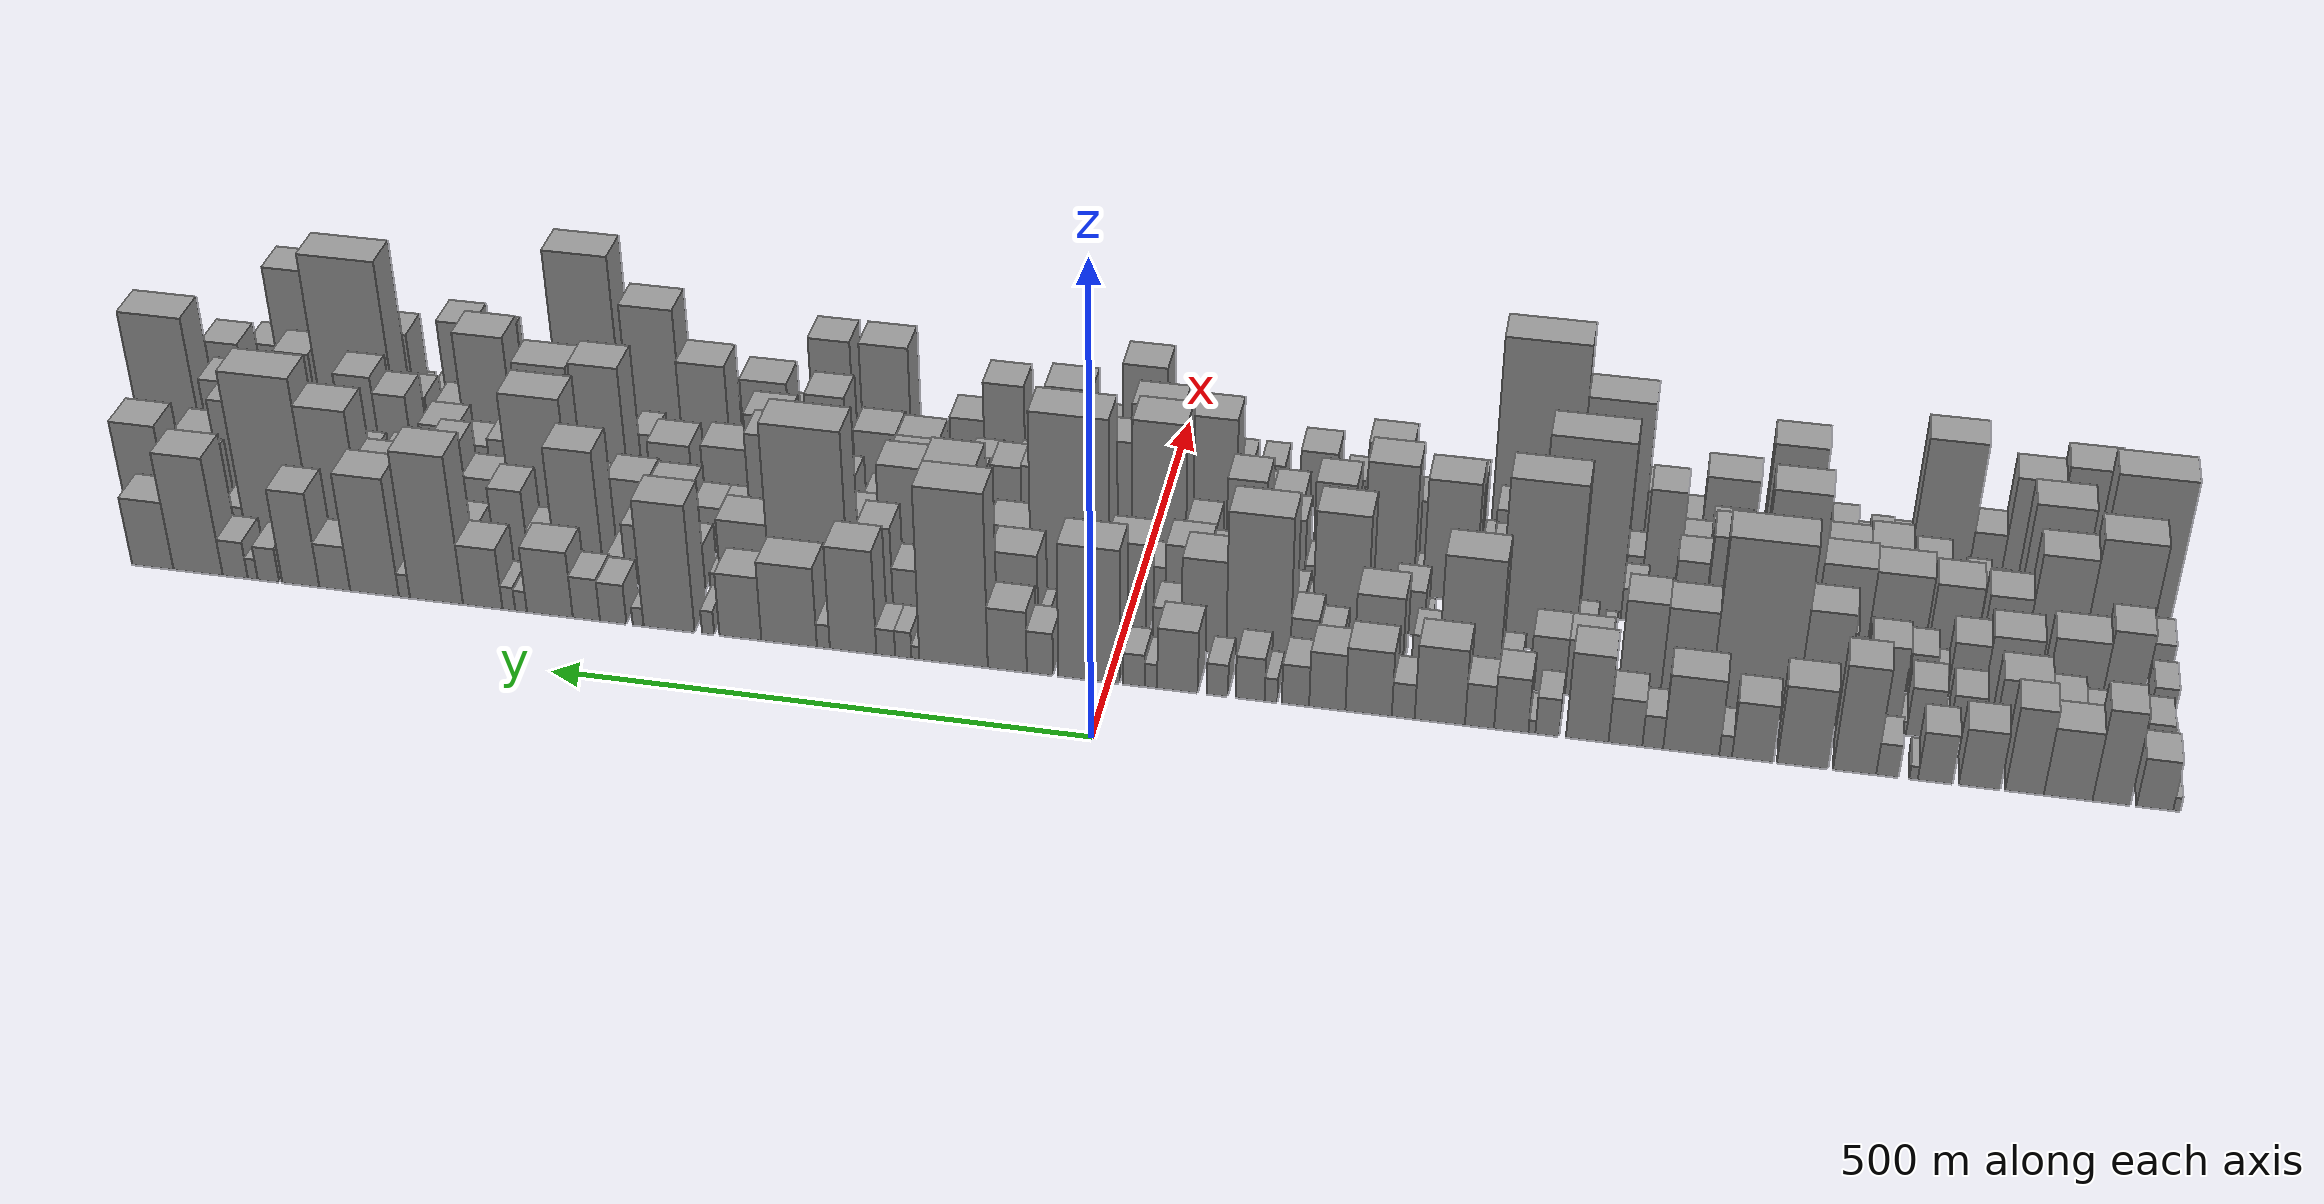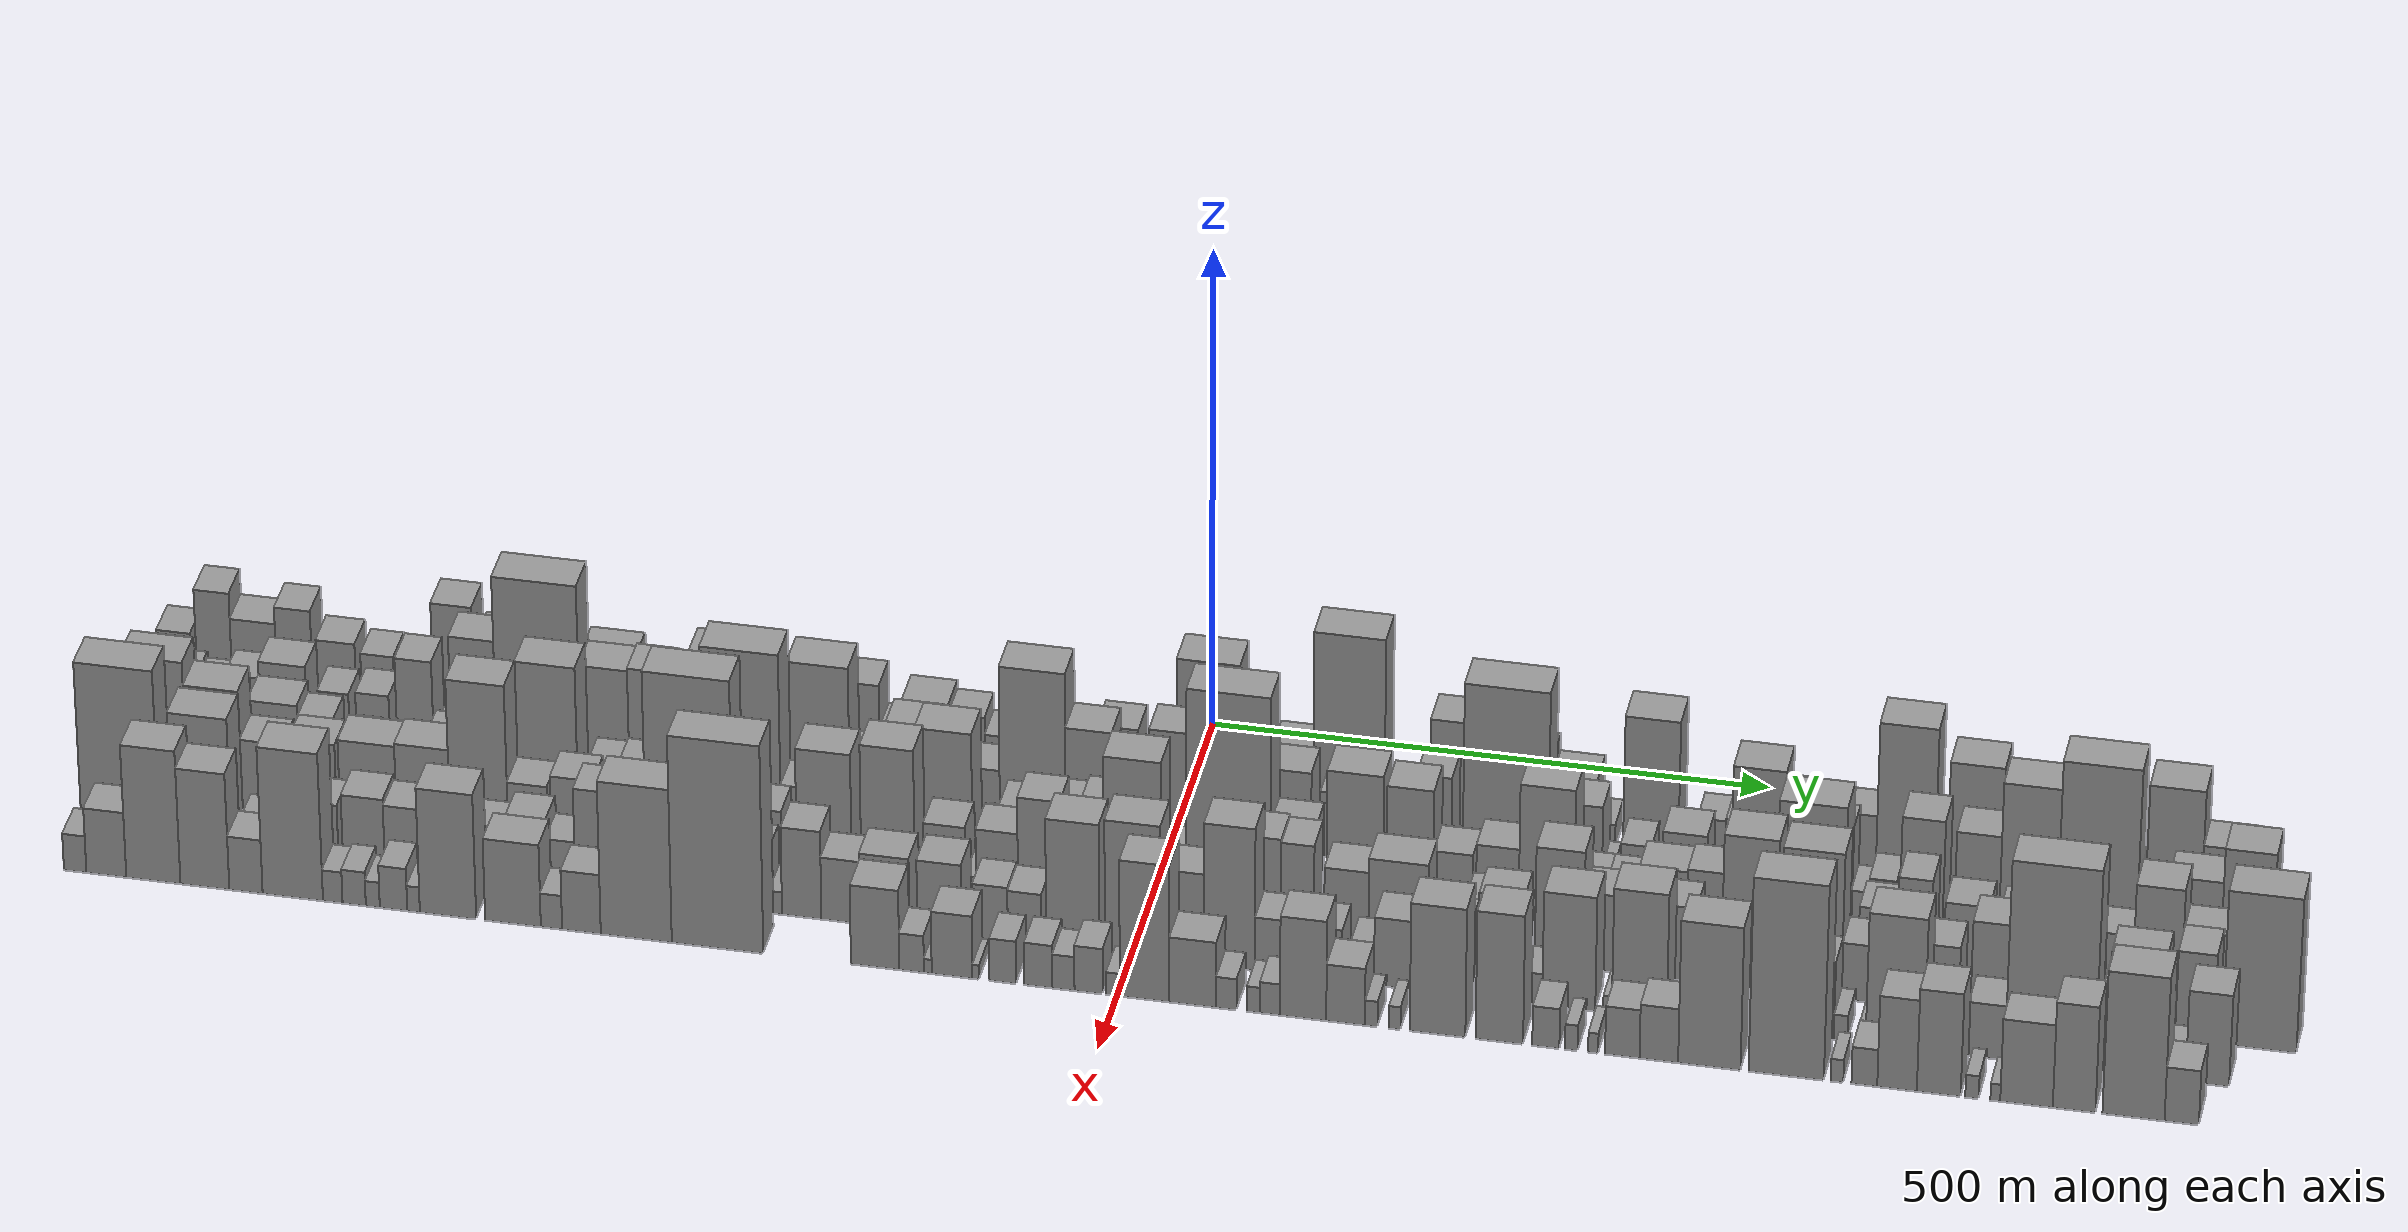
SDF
<sdf version="1.6">
 <world name="default">
  <scene>
   <sky><clouds><speed>12</speed></clouds></sky>
   <ambient>0.4 0.4 0.4 1</ambient>
   <background>0.7 0.7 0.7 1</background>
   <shadows>1</shadows>
  </scene>
  <gravity>0 0 -9.8066</gravity>
  <magnetic_field>6e-06 2.3e-05 -4.2e-05</magnetic_field>
  <physics default="0" name="default_physics" type="ode">
   <ode>
    <solver>
     <type>quick</type>
     <iters>10</iters>
     <sor>1.0</sor>
     <use_dynamic_moi_rescaling>0</use_dynamic_moi_rescaling>
    </solver>
    <constraints>
     <cfm>0</cfm>
     <erp>0.2</erp>
     <contact_max_correcting_vel>100</contact_max_correcting_vel>
     <contact_surface_layer>0.001</contact_surface_layer>
    </constraints>
   </ode>
   <max_step_size>0.004</max_step_size>
   <real_time_factor>1</real_time_factor>
   <real_time_update_rate>250</real_time_update_rate>
  </physics>
  <light name="sun" type="directional">
   <pose>0 0 10 0 0 0</pose>
   <diffuse>0.8 0.8 0.8 1</diffuse>
   <specular>0.2 0.2 0.2 1</specular>
   <attenuation>
    <range>1000</range>
    <constant>0.9</constant>
    <linear>0.01</linear>
    <quadratic>0.001</quadratic>
   </attenuation>
   <direction>-0.5 0.1 -0.9</direction>
  </light>
  <model name="building_1">
   <static>1</static>
   <pose>100.0000 -936.9196 0 0.000000 0.000000 0.000000</pose>
   <link name="link">
    <pose>0 0 7.50 0 0 0</pose>
    <collision name="collision"><geometry><box><size>40.0000 6.1608 15.0000</size></box></geometry></collision>
    <visual name="visual">
     <cast_shadows>0</cast_shadows>
     <geometry><box><size>40.0000 6.1608 15.0000</size></box></geometry>
     <material>
      <script>
       <uri>model://grey_wall/materials/scripts</uri>
       <uri>model://grey_wall/materials/textures</uri>
       <name>vrc/grey_wall</name>
      </script>
     </material>
    </visual>
   </link>
  </model>
  <model name="building_2">
   <static>1</static>
   <pose>100.0000 -918.4196 0 0.000000 0.000000 0.000000</pose>
   <link name="link">
    <pose>0 0 27.00 0 0 0</pose>
    <collision name="collision"><geometry><box><size>40.0000 30.8391 54.0000</size></box></geometry></collision>
    <visual name="visual">
     <cast_shadows>0</cast_shadows>
     <geometry><box><size>40.0000 30.8391 54.0000</size></box></geometry>
     <material>
      <script>
       <uri>model://grey_wall/materials/scripts</uri>
       <uri>model://grey_wall/materials/textures</uri>
       <name>vrc/grey_wall</name>
      </script>
     </material>
    </visual>
   </link>
  </model>
  <model name="building_3">
   <static>1</static>
   <pose>100.0000 -881.9433 0 0.000000 0.000000 0.000000</pose>
   <link name="link">
    <pose>0 0 51.00 0 0 0</pose>
    <collision name="collision"><geometry><box><size>40.0000 32.1136 102.0000</size></box></geometry></collision>
    <visual name="visual">
     <cast_shadows>0</cast_shadows>
     <geometry><box><size>40.0000 32.1136 102.0000</size></box></geometry>
     <material>
      <script>
       <uri>model://grey_wall/materials/scripts</uri>
       <uri>model://grey_wall/materials/textures</uri>
       <name>vrc/grey_wall</name>
      </script>
     </material>
    </visual>
   </link>
  </model>
  <model name="building_4">
   <static>1</static>
   <pose>100.0000 -845.3050 0 0.000000 0.000000 0.000000</pose>
   <link name="link">
    <pose>0 0 37.50 0 0 0</pose>
    <collision name="collision"><geometry><box><size>40.0000 41.1630 75.0000</size></box></geometry></collision>
    <visual name="visual">
     <cast_shadows>0</cast_shadows>
     <geometry><box><size>40.0000 41.1630 75.0000</size></box></geometry>
     <material>
      <script>
       <uri>model://grey_wall/materials/scripts</uri>
       <uri>model://grey_wall/materials/textures</uri>
       <name>vrc/grey_wall</name>
      </script>
     </material>
    </visual>
   </link>
  </model>
  <model name="building_5">
   <static>1</static>
   <pose>100.0000 -808.3368 0 0.000000 0.000000 0.000000</pose>
   <link name="link">
    <pose>0 0 46.50 0 0 0</pose>
    <collision name="collision"><geometry><box><size>40.0000 32.7734 93.0000</size></box></geometry></collision>
    <visual name="visual">
     <cast_shadows>0</cast_shadows>
     <geometry><box><size>40.0000 32.7734 93.0000</size></box></geometry>
     <material>
      <script>
       <uri>model://grey_wall/materials/scripts</uri>
       <uri>model://grey_wall/materials/textures</uri>
       <name>vrc/grey_wall</name>
      </script>
     </material>
    </visual>
   </link>
  </model>
  <model name="building_6">
   <static>1</static>
   <pose>100.0000 -770.1208 0 0.000000 0.000000 0.000000</pose>
   <link name="link">
    <pose>0 0 31.50 0 0 0</pose>
    <collision name="collision"><geometry><box><size>40.0000 35.6585 63.0000</size></box></geometry></collision>
    <visual name="visual">
     <cast_shadows>0</cast_shadows>
     <geometry><box><size>40.0000 35.6585 63.0000</size></box></geometry>
     <material>
      <script>
       <uri>model://grey_wall/materials/scripts</uri>
       <uri>model://grey_wall/materials/textures</uri>
       <name>vrc/grey_wall</name>
      </script>
     </material>
    </visual>
   </link>
  </model>
  <model name="building_7">
   <static>1</static>
   <pose>100.0000 -732.2711 0 0.000000 0.000000 0.000000</pose>
   <link name="link">
    <pose>0 0 27.00 0 0 0</pose>
    <collision name="collision"><geometry><box><size>40.0000 30.0410 54.0000</size></box></geometry></collision>
    <visual name="visual">
     <cast_shadows>0</cast_shadows>
     <geometry><box><size>40.0000 30.0410 54.0000</size></box></geometry>
     <material>
      <script>
       <uri>model://grey_wall/materials/scripts</uri>
       <uri>model://grey_wall/materials/textures</uri>
       <name>vrc/grey_wall</name>
      </script>
     </material>
    </visual>
   </link>
  </model>
  <model name="building_8">
   <static>1</static>
   <pose>100.0000 -713.5955 0 0.000000 0.000000 0.000000</pose>
   <link name="link">
    <pose>0 0 7.50 0 0 0</pose>
    <collision name="collision"><geometry><box><size>40.0000 7.3101 15.0000</size></box></geometry></collision>
    <visual name="visual">
     <cast_shadows>0</cast_shadows>
     <geometry><box><size>40.0000 7.3101 15.0000</size></box></geometry>
     <material>
      <script>
       <uri>model://grey_wall/materials/scripts</uri>
       <uri>model://grey_wall/materials/textures</uri>
       <name>vrc/grey_wall</name>
      </script>
     </material>
    </visual>
   </link>
  </model>
  <model name="building_9">
   <static>1</static>
   <pose>100.0000 -691.2593 0 0.000000 0.000000 0.000000</pose>
   <link name="link">
    <pose>0 0 18.00 0 0 0</pose>
    <collision name="collision"><geometry><box><size>40.0000 19.3624 36.0000</size></box></geometry></collision>
    <visual name="visual">
     <cast_shadows>0</cast_shadows>
     <geometry><box><size>40.0000 19.3624 36.0000</size></box></geometry>
     <material>
      <script>
       <uri>model://grey_wall/materials/scripts</uri>
       <uri>model://grey_wall/materials/textures</uri>
       <name>vrc/grey_wall</name>
      </script>
     </material>
    </visual>
   </link>
  </model>
  <model name="building_10">
   <static>1</static>
   <pose>100.0000 -662.9509 0 0.000000 0.000000 0.000000</pose>
   <link name="link">
    <pose>0 0 58.50 0 0 0</pose>
    <collision name="collision"><geometry><box><size>40.0000 37.2543 117.0000</size></box></geometry></collision>
    <visual name="visual">
     <cast_shadows>0</cast_shadows>
     <geometry><box><size>40.0000 37.2543 117.0000</size></box></geometry>
     <material>
      <script>
       <uri>model://grey_wall/materials/scripts</uri>
       <uri>model://grey_wall/materials/textures</uri>
       <name>vrc/grey_wall</name>
      </script>
     </material>
    </visual>
   </link>
  </model>
  <model name="building_11">
   <static>1</static>
   <pose>100.0000 -618.1327 0 0.000000 0.000000 0.000000</pose>
   <link name="link">
    <pose>0 0 43.50 0 0 0</pose>
    <collision name="collision"><geometry><box><size>40.0000 44.3821 87.0000</size></box></geometry></collision>
    <visual name="visual">
     <cast_shadows>0</cast_shadows>
     <geometry><box><size>40.0000 44.3821 87.0000</size></box></geometry>
     <material>
      <script>
       <uri>model://grey_wall/materials/scripts</uri>
       <uri>model://grey_wall/materials/textures</uri>
       <name>vrc/grey_wall</name>
      </script>
     </material>
    </visual>
   </link>
  </model>
  <model name="building_12">
   <static>1</static>
   <pose>100.0000 -574.7860 0 0.000000 0.000000 0.000000</pose>
   <link name="link">
    <pose>0 0 31.50 0 0 0</pose>
    <collision name="collision"><geometry><box><size>40.0000 36.3113 63.0000</size></box></geometry></collision>
    <visual name="visual">
     <cast_shadows>0</cast_shadows>
     <geometry><box><size>40.0000 36.3113 63.0000</size></box></geometry>
     <material>
      <script>
       <uri>model://grey_wall/materials/scripts</uri>
       <uri>model://grey_wall/materials/textures</uri>
       <name>vrc/grey_wall</name>
      </script>
     </material>
    </visual>
   </link>
  </model>
  <model name="building_13">
   <static>1</static>
   <pose>100.0000 -551.0722 0 0.000000 0.000000 0.000000</pose>
   <link name="link">
    <pose>0 0 12.00 0 0 0</pose>
    <collision name="collision"><geometry><box><size>40.0000 11.1163 24.0000</size></box></geometry></collision>
    <visual name="visual">
     <cast_shadows>0</cast_shadows>
     <geometry><box><size>40.0000 11.1163 24.0000</size></box></geometry>
     <material>
      <script>
       <uri>model://grey_wall/materials/scripts</uri>
       <uri>model://grey_wall/materials/textures</uri>
       <name>vrc/grey_wall</name>
      </script>
     </material>
    </visual>
   </link>
  </model>
  <model name="building_14">
   <static>1</static>
   <pose>100.0000 -521.0205 0 0.000000 0.000000 0.000000</pose>
   <link name="link">
    <pose>0 0 42.00 0 0 0</pose>
    <collision name="collision"><geometry><box><size>40.0000 48.9872 84.0000</size></box></geometry></collision>
    <visual name="visual">
     <cast_shadows>0</cast_shadows>
     <geometry><box><size>40.0000 48.9872 84.0000</size></box></geometry>
     <material>
      <script>
       <uri>model://grey_wall/materials/scripts</uri>
       <uri>model://grey_wall/materials/textures</uri>
       <name>vrc/grey_wall</name>
      </script>
     </material>
    </visual>
   </link>
  </model>
  <model name="building_15">
   <static>1</static>
   <pose>100.0000 -487.3927 0 0.000000 0.000000 0.000000</pose>
   <link name="link">
    <pose>0 0 18.00 0 0 0</pose>
    <collision name="collision"><geometry><box><size>40.0000 18.2683 36.0000</size></box></geometry></collision>
    <visual name="visual">
     <cast_shadows>0</cast_shadows>
     <geometry><box><size>40.0000 18.2683 36.0000</size></box></geometry>
     <material>
      <script>
       <uri>model://grey_wall/materials/scripts</uri>
       <uri>model://grey_wall/materials/textures</uri>
       <name>vrc/grey_wall</name>
      </script>
     </material>
    </visual>
   </link>
  </model>
  <model name="building_16">
   <static>1</static>
   <pose>100.0000 -463.3852 0 0.000000 0.000000 0.000000</pose>
   <link name="link">
    <pose>0 0 25.50 0 0 0</pose>
    <collision name="collision"><geometry><box><size>40.0000 29.7467 51.0000</size></box></geometry></collision>
    <visual name="visual">
     <cast_shadows>0</cast_shadows>
     <geometry><box><size>40.0000 29.7467 51.0000</size></box></geometry>
     <material>
      <script>
       <uri>model://grey_wall/materials/scripts</uri>
       <uri>model://grey_wall/materials/textures</uri>
       <name>vrc/grey_wall</name>
      </script>
     </material>
    </visual>
   </link>
  </model>
  <model name="building_17">
   <static>1</static>
   <pose>100.0000 -429.7634 0 0.000000 0.000000 0.000000</pose>
   <link name="link">
    <pose>0 0 48.00 0 0 0</pose>
    <collision name="collision"><geometry><box><size>40.0000 37.4968 96.0000</size></box></geometry></collision>
    <visual name="visual">
     <cast_shadows>0</cast_shadows>
     <geometry><box><size>40.0000 37.4968 96.0000</size></box></geometry>
     <material>
      <script>
       <uri>model://grey_wall/materials/scripts</uri>
       <uri>model://grey_wall/materials/textures</uri>
       <name>vrc/grey_wall</name>
      </script>
     </material>
    </visual>
   </link>
  </model>
  <model name="building_18">
   <static>1</static>
   <pose>100.0000 -394.4457 0 0.000000 0.000000 0.000000</pose>
   <link name="link">
    <pose>0 0 21.00 0 0 0</pose>
    <collision name="collision"><geometry><box><size>40.0000 21.1388 42.0000</size></box></geometry></collision>
    <visual name="visual">
     <cast_shadows>0</cast_shadows>
     <geometry><box><size>40.0000 21.1388 42.0000</size></box></geometry>
     <material>
      <script>
       <uri>model://grey_wall/materials/scripts</uri>
       <uri>model://grey_wall/materials/textures</uri>
       <name>vrc/grey_wall</name>
      </script>
     </material>
    </visual>
   </link>
  </model>
  <model name="building_19">
   <static>1</static>
   <pose>100.0000 -380.8029 0 0.000000 0.000000 0.000000</pose>
   <link name="link">
    <pose>0 0 7.50 0 0 0</pose>
    <collision name="collision"><geometry><box><size>40.0000 6.1468 15.0000</size></box></geometry></collision>
    <visual name="visual">
     <cast_shadows>0</cast_shadows>
     <geometry><box><size>40.0000 6.1468 15.0000</size></box></geometry>
     <material>
      <script>
       <uri>model://grey_wall/materials/scripts</uri>
       <uri>model://grey_wall/materials/textures</uri>
       <name>vrc/grey_wall</name>
      </script>
     </material>
    </visual>
   </link>
  </model>
  <model name="building_20">
   <static>1</static>
   <pose>100.0000 -362.4652 0 0.000000 0.000000 0.000000</pose>
   <link name="link">
    <pose>0 0 30.00 0 0 0</pose>
    <collision name="collision"><geometry><box><size>40.0000 30.5286 60.0000</size></box></geometry></collision>
    <visual name="visual">
     <cast_shadows>0</cast_shadows>
     <geometry><box><size>40.0000 30.5286 60.0000</size></box></geometry>
     <material>
      <script>
       <uri>model://grey_wall/materials/scripts</uri>
       <uri>model://grey_wall/materials/textures</uri>
       <name>vrc/grey_wall</name>
      </script>
     </material>
    </visual>
   </link>
  </model>
  <model name="building_21">
   <static>1</static>
   <pose>100.0000 -334.2589 0 0.000000 0.000000 0.000000</pose>
   <link name="link">
    <pose>0 0 24.00 0 0 0</pose>
    <collision name="collision"><geometry><box><size>40.0000 25.8841 48.0000</size></box></geometry></collision>
    <visual name="visual">
     <cast_shadows>0</cast_shadows>
     <geometry><box><size>40.0000 25.8841 48.0000</size></box></geometry>
     <material>
      <script>
       <uri>model://grey_wall/materials/scripts</uri>
       <uri>model://grey_wall/materials/textures</uri>
       <name>vrc/grey_wall</name>
      </script>
     </material>
    </visual>
   </link>
  </model>
  <model name="building_22">
   <static>1</static>
   <pose>100.0000 -298.8532 0 0.000000 0.000000 0.000000</pose>
   <link name="link">
    <pose>0 0 42.00 0 0 0</pose>
    <collision name="collision"><geometry><box><size>40.0000 44.9272 84.0000</size></box></geometry></collision>
    <visual name="visual">
     <cast_shadows>0</cast_shadows>
     <geometry><box><size>40.0000 44.9272 84.0000</size></box></geometry>
     <material>
      <script>
       <uri>model://grey_wall/materials/scripts</uri>
       <uri>model://grey_wall/materials/textures</uri>
       <name>vrc/grey_wall</name>
      </script>
     </material>
    </visual>
   </link>
  </model>
  <model name="building_23">
   <static>1</static>
   <pose>100.0000 -266.1314 0 0.000000 0.000000 0.000000</pose>
   <link name="link">
    <pose>0 0 19.50 0 0 0</pose>
    <collision name="collision"><geometry><box><size>40.0000 20.5165 39.0000</size></box></geometry></collision>
    <visual name="visual">
     <cast_shadows>0</cast_shadows>
     <geometry><box><size>40.0000 20.5165 39.0000</size></box></geometry>
     <material>
      <script>
       <uri>model://grey_wall/materials/scripts</uri>
       <uri>model://grey_wall/materials/textures</uri>
       <name>vrc/grey_wall</name>
      </script>
     </material>
    </visual>
   </link>
  </model>
  <model name="building_24">
   <static>1</static>
   <pose>100.0000 -235.0127 0 0.000000 0.000000 0.000000</pose>
   <link name="link">
    <pose>0 0 36.00 0 0 0</pose>
    <collision name="collision"><geometry><box><size>40.0000 41.7209 72.0000</size></box></geometry></collision>
    <visual name="visual">
     <cast_shadows>0</cast_shadows>
     <geometry><box><size>40.0000 41.7209 72.0000</size></box></geometry>
     <material>
      <script>
       <uri>model://grey_wall/materials/scripts</uri>
       <uri>model://grey_wall/materials/textures</uri>
       <name>vrc/grey_wall</name>
      </script>
     </material>
    </visual>
   </link>
  </model>
  <model name="building_25">
   <static>1</static>
   <pose>100.0000 -197.7678 0 0.000000 0.000000 0.000000</pose>
   <link name="link">
    <pose>0 0 31.50 0 0 0</pose>
    <collision name="collision"><geometry><box><size>40.0000 32.7689 63.0000</size></box></geometry></collision>
    <visual name="visual">
     <cast_shadows>0</cast_shadows>
     <geometry><box><size>40.0000 32.7689 63.0000</size></box></geometry>
     <material>
      <script>
       <uri>model://grey_wall/materials/scripts</uri>
       <uri>model://grey_wall/materials/textures</uri>
       <name>vrc/grey_wall</name>
      </script>
     </material>
    </visual>
   </link>
  </model>
  <model name="building_26">
   <static>1</static>
   <pose>100.0000 -169.0179 0 0.000000 0.000000 0.000000</pose>
   <link name="link">
    <pose>0 0 22.50 0 0 0</pose>
    <collision name="collision"><geometry><box><size>40.0000 24.7308 45.0000</size></box></geometry></collision>
    <visual name="visual">
     <cast_shadows>0</cast_shadows>
     <geometry><box><size>40.0000 24.7308 45.0000</size></box></geometry>
     <material>
      <script>
       <uri>model://grey_wall/materials/scripts</uri>
       <uri>model://grey_wall/materials/textures</uri>
       <name>vrc/grey_wall</name>
      </script>
     </material>
    </visual>
   </link>
  </model>
  <model name="building_27">
   <static>1</static>
   <pose>100.0000 -146.9391 0 0.000000 0.000000 0.000000</pose>
   <link name="link">
    <pose>0 0 13.50 0 0 0</pose>
    <collision name="collision"><geometry><box><size>40.0000 11.4268 27.0000</size></box></geometry></collision>
    <visual name="visual">
     <cast_shadows>0</cast_shadows>
     <geometry><box><size>40.0000 11.4268 27.0000</size></box></geometry>
     <material>
      <script>
       <uri>model://grey_wall/materials/scripts</uri>
       <uri>model://grey_wall/materials/textures</uri>
       <name>vrc/grey_wall</name>
      </script>
     </material>
    </visual>
   </link>
  </model>
  <model name="building_28">
   <static>1</static>
   <pose>100.0000 -128.0139 0 0.000000 0.000000 0.000000</pose>
   <link name="link">
    <pose>0 0 24.00 0 0 0</pose>
    <collision name="collision"><geometry><box><size>40.0000 26.4236 48.0000</size></box></geometry></collision>
    <visual name="visual">
     <cast_shadows>0</cast_shadows>
     <geometry><box><size>40.0000 26.4236 48.0000</size></box></geometry>
     <material>
      <script>
       <uri>model://grey_wall/materials/scripts</uri>
       <uri>model://grey_wall/materials/textures</uri>
       <name>vrc/grey_wall</name>
      </script>
     </material>
    </visual>
   </link>
  </model>
  <model name="building_29">
   <static>1</static>
   <pose>100.0000 -98.0934 0 0.000000 0.000000 0.000000</pose>
   <link name="link">
    <pose>0 0 18.00 0 0 0</pose>
    <collision name="collision"><geometry><box><size>40.0000 19.4174 36.0000</size></box></geometry></collision>
    <visual name="visual">
     <cast_shadows>0</cast_shadows>
     <geometry><box><size>40.0000 19.4174 36.0000</size></box></geometry>
     <material>
      <script>
       <uri>model://grey_wall/materials/scripts</uri>
       <uri>model://grey_wall/materials/textures</uri>
       <name>vrc/grey_wall</name>
      </script>
     </material>
    </visual>
   </link>
  </model>
  <model name="building_30">
   <static>1</static>
   <pose>100.0000 -61.7897 0 0.000000 0.000000 0.000000</pose>
   <link name="link">
    <pose>0 0 34.50 0 0 0</pose>
    <collision name="collision"><geometry><box><size>40.0000 37.1900 69.0000</size></box></geometry></collision>
    <visual name="visual">
     <cast_shadows>0</cast_shadows>
     <geometry><box><size>40.0000 37.1900 69.0000</size></box></geometry>
     <material>
      <script>
       <uri>model://grey_wall/materials/scripts</uri>
       <uri>model://grey_wall/materials/textures</uri>
       <name>vrc/grey_wall</name>
      </script>
     </material>
    </visual>
   </link>
  </model>
  <model name="building_31">
   <static>1</static>
   <pose>100.0000 -37.3304 0 0.000000 0.000000 0.000000</pose>
   <link name="link">
    <pose>0 0 13.50 0 0 0</pose>
    <collision name="collision"><geometry><box><size>40.0000 11.7286 27.0000</size></box></geometry></collision>
    <visual name="visual">
     <cast_shadows>0</cast_shadows>
     <geometry><box><size>40.0000 11.7286 27.0000</size></box></geometry>
     <material>
      <script>
       <uri>model://grey_wall/materials/scripts</uri>
       <uri>model://grey_wall/materials/textures</uri>
       <name>vrc/grey_wall</name>
      </script>
     </material>
    </visual>
   </link>
  </model>
  <model name="building_32">
   <static>1</static>
   <pose>100.0000 -21.6655 0 0.000000 0.000000 0.000000</pose>
   <link name="link">
    <pose>0 0 18.00 0 0 0</pose>
    <collision name="collision"><geometry><box><size>40.0000 19.6011 36.0000</size></box></geometry></collision>
    <visual name="visual">
     <cast_shadows>0</cast_shadows>
     <geometry><box><size>40.0000 19.6011 36.0000</size></box></geometry>
     <material>
      <script>
       <uri>model://grey_wall/materials/scripts</uri>
       <uri>model://grey_wall/materials/textures</uri>
       <name>vrc/grey_wall</name>
      </script>
     </material>
    </visual>
   </link>
  </model>
  <model name="building_33">
   <static>1</static>
   <pose>100.0000 19.4667 0 0.000000 0.000000 0.000000</pose>
   <link name="link">
    <pose>0 0 75.00 0 0 0</pose>
    <collision name="collision"><geometry><box><size>40.0000 56.6632 150.0000</size></box></geometry></collision>
    <visual name="visual">
     <cast_shadows>0</cast_shadows>
     <geometry><box><size>40.0000 56.6632 150.0000</size></box></geometry>
     <material>
      <script>
       <uri>model://grey_wall/materials/scripts</uri>
       <uri>model://grey_wall/materials/textures</uri>
       <name>vrc/grey_wall</name>
      </script>
     </material>
    </visual>
   </link>
  </model>
  <model name="building_34">
   <static>1</static>
   <pose>100.0000 64.9660 0 0.000000 0.000000 0.000000</pose>
   <link name="link">
    <pose>0 0 24.00 0 0 0</pose>
    <collision name="collision"><geometry><box><size>40.0000 24.3354 48.0000</size></box></geometry></collision>
    <visual name="visual">
     <cast_shadows>0</cast_shadows>
     <geometry><box><size>40.0000 24.3354 48.0000</size></box></geometry>
     <material>
      <script>
       <uri>model://grey_wall/materials/scripts</uri>
       <uri>model://grey_wall/materials/textures</uri>
       <name>vrc/grey_wall</name>
      </script>
     </material>
    </visual>
   </link>
  </model>
  <model name="building_35">
   <static>1</static>
   <pose>100.0000 95.2352 0 0.000000 0.000000 0.000000</pose>
   <link name="link">
    <pose>0 0 34.50 0 0 0</pose>
    <collision name="collision"><geometry><box><size>40.0000 36.2030 69.0000</size></box></geometry></collision>
    <visual name="visual">
     <cast_shadows>0</cast_shadows>
     <geometry><box><size>40.0000 36.2030 69.0000</size></box></geometry>
     <material>
      <script>
       <uri>model://grey_wall/materials/scripts</uri>
       <uri>model://grey_wall/materials/textures</uri>
       <name>vrc/grey_wall</name>
      </script>
     </material>
    </visual>
   </link>
  </model>
  <model name="building_36">
   <static>1</static>
   <pose>100.0000 145.2437 0 0.000000 0.000000 0.000000</pose>
   <link name="link">
    <pose>0 0 97.50 0 0 0</pose>
    <collision name="collision"><geometry><box><size>40.0000 63.8139 195.0000</size></box></geometry></collision>
    <visual name="visual">
     <cast_shadows>0</cast_shadows>
     <geometry><box><size>40.0000 63.8139 195.0000</size></box></geometry>
     <material>
      <script>
       <uri>model://grey_wall/materials/scripts</uri>
       <uri>model://grey_wall/materials/textures</uri>
       <name>vrc/grey_wall</name>
      </script>
     </material>
    </visual>
   </link>
  </model>
  <model name="building_37">
   <static>1</static>
   <pose>100.0000 180.8640 0 0.000000 0.000000 0.000000</pose>
   <link name="link">
    <pose>0 0 7.50 0 0 0</pose>
    <collision name="collision"><geometry><box><size>40.0000 7.4268 15.0000</size></box></geometry></collision>
    <visual name="visual">
     <cast_shadows>0</cast_shadows>
     <geometry><box><size>40.0000 7.4268 15.0000</size></box></geometry>
     <material>
      <script>
       <uri>model://grey_wall/materials/scripts</uri>
       <uri>model://grey_wall/materials/textures</uri>
       <name>vrc/grey_wall</name>
      </script>
     </material>
    </visual>
   </link>
  </model>
  <model name="building_38">
   <static>1</static>
   <pose>100.0000 192.2269 0 0.000000 0.000000 0.000000</pose>
   <link name="link">
    <pose>0 0 15.00 0 0 0</pose>
    <collision name="collision"><geometry><box><size>40.0000 15.2988 30.0000</size></box></geometry></collision>
    <visual name="visual">
     <cast_shadows>0</cast_shadows>
     <geometry><box><size>40.0000 15.2988 30.0000</size></box></geometry>
     <material>
      <script>
       <uri>model://grey_wall/materials/scripts</uri>
       <uri>model://grey_wall/materials/textures</uri>
       <name>vrc/grey_wall</name>
      </script>
     </material>
    </visual>
   </link>
  </model>
  <model name="building_39">
   <static>1</static>
   <pose>100.0000 208.6810 0 0.000000 0.000000 0.000000</pose>
   <link name="link">
    <pose>0 0 15.00 0 0 0</pose>
    <collision name="collision"><geometry><box><size>40.0000 17.6095 30.0000</size></box></geometry></collision>
    <visual name="visual">
     <cast_shadows>0</cast_shadows>
     <geometry><box><size>40.0000 17.6095 30.0000</size></box></geometry>
     <material>
      <script>
       <uri>model://grey_wall/materials/scripts</uri>
       <uri>model://grey_wall/materials/textures</uri>
       <name>vrc/grey_wall</name>
      </script>
     </material>
    </visual>
   </link>
  </model>
  <model name="building_40">
   <static>1</static>
   <pose>100.0000 239.4291 0 0.000000 0.000000 0.000000</pose>
   <link name="link">
    <pose>0 0 58.50 0 0 0</pose>
    <collision name="collision"><geometry><box><size>40.0000 43.8867 117.0000</size></box></geometry></collision>
    <visual name="visual">
     <cast_shadows>0</cast_shadows>
     <geometry><box><size>40.0000 43.8867 117.0000</size></box></geometry>
     <material>
      <script>
       <uri>model://grey_wall/materials/scripts</uri>
       <uri>model://grey_wall/materials/textures</uri>
       <name>vrc/grey_wall</name>
      </script>
     </material>
    </visual>
   </link>
  </model>
  <model name="building_41">
   <static>1</static>
   <pose>100.0000 267.4837 0 0.000000 0.000000 0.000000</pose>
   <link name="link">
    <pose>0 0 13.50 0 0 0</pose>
    <collision name="collision"><geometry><box><size>40.0000 12.2225 27.0000</size></box></geometry></collision>
    <visual name="visual">
     <cast_shadows>0</cast_shadows>
     <geometry><box><size>40.0000 12.2225 27.0000</size></box></geometry>
     <material>
      <script>
       <uri>model://grey_wall/materials/scripts</uri>
       <uri>model://grey_wall/materials/textures</uri>
       <name>vrc/grey_wall</name>
      </script>
     </material>
    </visual>
   </link>
  </model>
  <model name="building_42">
   <static>1</static>
   <pose>100.0000 299.8959 0 0.000000 0.000000 0.000000</pose>
   <link name="link">
    <pose>0 0 45.00 0 0 0</pose>
    <collision name="collision"><geometry><box><size>40.0000 52.6018 90.0000</size></box></geometry></collision>
    <visual name="visual">
     <cast_shadows>0</cast_shadows>
     <geometry><box><size>40.0000 52.6018 90.0000</size></box></geometry>
     <material>
      <script>
       <uri>model://grey_wall/materials/scripts</uri>
       <uri>model://grey_wall/materials/textures</uri>
       <name>vrc/grey_wall</name>
      </script>
     </material>
    </visual>
   </link>
  </model>
  <model name="building_43">
   <static>1</static>
   <pose>100.0000 346.1152 0 0.000000 0.000000 0.000000</pose>
   <link name="link">
    <pose>0 0 36.00 0 0 0</pose>
    <collision name="collision"><geometry><box><size>40.0000 39.8369 72.0000</size></box></geometry></collision>
    <visual name="visual">
     <cast_shadows>0</cast_shadows>
     <geometry><box><size>40.0000 39.8369 72.0000</size></box></geometry>
     <material>
      <script>
       <uri>model://grey_wall/materials/scripts</uri>
       <uri>model://grey_wall/materials/textures</uri>
       <name>vrc/grey_wall</name>
      </script>
     </material>
    </visual>
   </link>
  </model>
  <model name="building_44">
   <static>1</static>
   <pose>100.0000 376.8552 0 0.000000 0.000000 0.000000</pose>
   <link name="link">
    <pose>0 0 13.50 0 0 0</pose>
    <collision name="collision"><geometry><box><size>40.0000 11.6431 27.0000</size></box></geometry></collision>
    <visual name="visual">
     <cast_shadows>0</cast_shadows>
     <geometry><box><size>40.0000 11.6431 27.0000</size></box></geometry>
     <material>
      <script>
       <uri>model://grey_wall/materials/scripts</uri>
       <uri>model://grey_wall/materials/textures</uri>
       <name>vrc/grey_wall</name>
      </script>
     </material>
    </visual>
   </link>
  </model>
  <model name="building_45">
   <static>1</static>
   <pose>100.0000 414.1747 0 0.000000 0.000000 0.000000</pose>
   <link name="link">
    <pose>0 0 72.00 0 0 0</pose>
    <collision name="collision"><geometry><box><size>40.0000 48.9959 144.0000</size></box></geometry></collision>
    <visual name="visual">
     <cast_shadows>0</cast_shadows>
     <geometry><box><size>40.0000 48.9959 144.0000</size></box></geometry>
     <material>
      <script>
       <uri>model://grey_wall/materials/scripts</uri>
       <uri>model://grey_wall/materials/textures</uri>
       <name>vrc/grey_wall</name>
      </script>
     </material>
    </visual>
   </link>
  </model>
  <model name="building_46">
   <static>1</static>
   <pose>100.0000 443.8975 0 0.000000 0.000000 0.000000</pose>
   <link name="link">
    <pose>0 0 10.50 0 0 0</pose>
    <collision name="collision"><geometry><box><size>40.0000 10.4497 21.0000</size></box></geometry></collision>
    <visual name="visual">
     <cast_shadows>0</cast_shadows>
     <geometry><box><size>40.0000 10.4497 21.0000</size></box></geometry>
     <material>
      <script>
       <uri>model://grey_wall/materials/scripts</uri>
       <uri>model://grey_wall/materials/textures</uri>
       <name>vrc/grey_wall</name>
      </script>
     </material>
    </visual>
   </link>
  </model>
  <model name="building_47">
   <static>1</static>
   <pose>100.0000 467.8618 0 0.000000 0.000000 0.000000</pose>
   <link name="link">
    <pose>0 0 22.50 0 0 0</pose>
    <collision name="collision"><geometry><box><size>40.0000 25.4788 45.0000</size></box></geometry></collision>
    <visual name="visual">
     <cast_shadows>0</cast_shadows>
     <geometry><box><size>40.0000 25.4788 45.0000</size></box></geometry>
     <material>
      <script>
       <uri>model://grey_wall/materials/scripts</uri>
       <uri>model://grey_wall/materials/textures</uri>
       <name>vrc/grey_wall</name>
      </script>
     </material>
    </visual>
   </link>
  </model>
  <model name="building_48">
   <static>1</static>
   <pose>100.0000 493.7250 0 0.000000 0.000000 0.000000</pose>
   <link name="link">
    <pose>0 0 24.00 0 0 0</pose>
    <collision name="collision"><geometry><box><size>40.0000 26.2477 48.0000</size></box></geometry></collision>
    <visual name="visual">
     <cast_shadows>0</cast_shadows>
     <geometry><box><size>40.0000 26.2477 48.0000</size></box></geometry>
     <material>
      <script>
       <uri>model://grey_wall/materials/scripts</uri>
       <uri>model://grey_wall/materials/textures</uri>
       <name>vrc/grey_wall</name>
      </script>
     </material>
    </visual>
   </link>
  </model>
  <model name="building_49">
   <static>1</static>
   <pose>100.0000 529.0717 0 0.000000 0.000000 0.000000</pose>
   <link name="link">
    <pose>0 0 37.50 0 0 0</pose>
    <collision name="collision"><geometry><box><size>40.0000 44.4456 75.0000</size></box></geometry></collision>
    <visual name="visual">
     <cast_shadows>0</cast_shadows>
     <geometry><box><size>40.0000 44.4456 75.0000</size></box></geometry>
     <material>
      <script>
       <uri>model://grey_wall/materials/scripts</uri>
       <uri>model://grey_wall/materials/textures</uri>
       <name>vrc/grey_wall</name>
      </script>
     </material>
    </visual>
   </link>
  </model>
  <model name="building_50">
   <static>1</static>
   <pose>100.0000 556.9595 0 0.000000 0.000000 0.000000</pose>
   <link name="link">
    <pose>0 0 12.00 0 0 0</pose>
    <collision name="collision"><geometry><box><size>40.0000 11.3300 24.0000</size></box></geometry></collision>
    <visual name="visual">
     <cast_shadows>0</cast_shadows>
     <geometry><box><size>40.0000 11.3300 24.0000</size></box></geometry>
     <material>
      <script>
       <uri>model://grey_wall/materials/scripts</uri>
       <uri>model://grey_wall/materials/textures</uri>
       <name>vrc/grey_wall</name>
      </script>
     </material>
    </visual>
   </link>
  </model>
  <model name="building_51">
   <static>1</static>
   <pose>100.0000 568.8188 0 0.000000 0.000000 0.000000</pose>
   <link name="link">
    <pose>0 0 13.50 0 0 0</pose>
    <collision name="collision"><geometry><box><size>40.0000 12.3887 27.0000</size></box></geometry></collision>
    <visual name="visual">
     <cast_shadows>0</cast_shadows>
     <geometry><box><size>40.0000 12.3887 27.0000</size></box></geometry>
     <material>
      <script>
       <uri>model://grey_wall/materials/scripts</uri>
       <uri>model://grey_wall/materials/textures</uri>
       <name>vrc/grey_wall</name>
      </script>
     </material>
    </visual>
   </link>
  </model>
  <model name="building_52">
   <static>1</static>
   <pose>100.0000 594.2181 0 0.000000 0.000000 0.000000</pose>
   <link name="link">
    <pose>0 0 34.50 0 0 0</pose>
    <collision name="collision"><geometry><box><size>40.0000 38.4099 69.0000</size></box></geometry></collision>
    <visual name="visual">
     <cast_shadows>0</cast_shadows>
     <geometry><box><size>40.0000 38.4099 69.0000</size></box></geometry>
     <material>
      <script>
       <uri>model://grey_wall/materials/scripts</uri>
       <uri>model://grey_wall/materials/textures</uri>
       <name>vrc/grey_wall</name>
      </script>
     </material>
    </visual>
   </link>
  </model>
  <model name="building_53">
   <static>1</static>
   <pose>100.0000 639.3999 0 0.000000 0.000000 0.000000</pose>
   <link name="link">
    <pose>0 0 84.00 0 0 0</pose>
    <collision name="collision"><geometry><box><size>40.0000 51.9538 168.0000</size></box></geometry></collision>
    <visual name="visual">
     <cast_shadows>0</cast_shadows>
     <geometry><box><size>40.0000 51.9538 168.0000</size></box></geometry>
     <material>
      <script>
       <uri>model://grey_wall/materials/scripts</uri>
       <uri>model://grey_wall/materials/textures</uri>
       <name>vrc/grey_wall</name>
      </script>
     </material>
    </visual>
   </link>
  </model>
  <model name="building_54">
   <static>1</static>
   <pose>100.0000 670.7902 0 0.000000 0.000000 0.000000</pose>
   <link name="link">
    <pose>0 0 13.50 0 0 0</pose>
    <collision name="collision"><geometry><box><size>40.0000 10.8269 27.0000</size></box></geometry></collision>
    <visual name="visual">
     <cast_shadows>0</cast_shadows>
     <geometry><box><size>40.0000 10.8269 27.0000</size></box></geometry>
     <material>
      <script>
       <uri>model://grey_wall/materials/scripts</uri>
       <uri>model://grey_wall/materials/textures</uri>
       <name>vrc/grey_wall</name>
      </script>
     </material>
    </visual>
   </link>
  </model>
  <model name="building_55">
   <static>1</static>
   <pose>100.0000 700.2312 0 0.000000 0.000000 0.000000</pose>
   <link name="link">
    <pose>0 0 67.50 0 0 0</pose>
    <collision name="collision"><geometry><box><size>40.0000 48.0550 135.0000</size></box></geometry></collision>
    <visual name="visual">
     <cast_shadows>0</cast_shadows>
     <geometry><box><size>40.0000 48.0550 135.0000</size></box></geometry>
     <material>
      <script>
       <uri>model://grey_wall/materials/scripts</uri>
       <uri>model://grey_wall/materials/textures</uri>
       <name>vrc/grey_wall</name>
      </script>
     </material>
    </visual>
   </link>
  </model>
  <model name="building_56">
   <static>1</static>
   <pose>100.0000 739.4798 0 0.000000 0.000000 0.000000</pose>
   <link name="link">
    <pose>0 0 25.50 0 0 0</pose>
    <collision name="collision"><geometry><box><size>40.0000 30.4422 51.0000</size></box></geometry></collision>
    <visual name="visual">
     <cast_shadows>0</cast_shadows>
     <geometry><box><size>40.0000 30.4422 51.0000</size></box></geometry>
     <material>
      <script>
       <uri>model://grey_wall/materials/scripts</uri>
       <uri>model://grey_wall/materials/textures</uri>
       <name>vrc/grey_wall</name>
      </script>
     </material>
    </visual>
   </link>
  </model>
  <model name="building_57">
   <static>1</static>
   <pose>100.0000 773.0551 0 0.000000 0.000000 0.000000</pose>
   <link name="link">
    <pose>0 0 54.00 0 0 0</pose>
    <collision name="collision"><geometry><box><size>40.0000 36.7085 108.0000</size></box></geometry></collision>
    <visual name="visual">
     <cast_shadows>0</cast_shadows>
     <geometry><box><size>40.0000 36.7085 108.0000</size></box></geometry>
     <material>
      <script>
       <uri>model://grey_wall/materials/scripts</uri>
       <uri>model://grey_wall/materials/textures</uri>
       <name>vrc/grey_wall</name>
      </script>
     </material>
    </visual>
   </link>
  </model>
  <model name="building_58">
   <static>1</static>
   <pose>100.0000 805.1073 0 0.000000 0.000000 0.000000</pose>
   <link name="link">
    <pose>0 0 19.50 0 0 0</pose>
    <collision name="collision"><geometry><box><size>40.0000 21.3959 39.0000</size></box></geometry></collision>
    <visual name="visual">
     <cast_shadows>0</cast_shadows>
     <geometry><box><size>40.0000 21.3959 39.0000</size></box></geometry>
     <material>
      <script>
       <uri>model://grey_wall/materials/scripts</uri>
       <uri>model://grey_wall/materials/textures</uri>
       <name>vrc/grey_wall</name>
      </script>
     </material>
    </visual>
   </link>
  </model>
  <model name="building_59">
   <static>1</static>
   <pose>100.0000 820.7397 0 0.000000 0.000000 0.000000</pose>
   <link name="link">
    <pose>0 0 12.00 0 0 0</pose>
    <collision name="collision"><geometry><box><size>40.0000 9.8689 24.0000</size></box></geometry></collision>
    <visual name="visual">
     <cast_shadows>0</cast_shadows>
     <geometry><box><size>40.0000 9.8689 24.0000</size></box></geometry>
     <material>
      <script>
       <uri>model://grey_wall/materials/scripts</uri>
       <uri>model://grey_wall/materials/textures</uri>
       <name>vrc/grey_wall</name>
      </script>
     </material>
    </visual>
   </link>
  </model>
  <model name="building_60">
   <static>1</static>
   <pose>100.0000 838.1900 0 0.000000 0.000000 0.000000</pose>
   <link name="link">
    <pose>0 0 21.00 0 0 0</pose>
    <collision name="collision"><geometry><box><size>40.0000 25.0318 42.0000</size></box></geometry></collision>
    <visual name="visual">
     <cast_shadows>0</cast_shadows>
     <geometry><box><size>40.0000 25.0318 42.0000</size></box></geometry>
     <material>
      <script>
       <uri>model://grey_wall/materials/scripts</uri>
       <uri>model://grey_wall/materials/textures</uri>
       <name>vrc/grey_wall</name>
      </script>
     </material>
    </visual>
   </link>
  </model>
  <model name="building_61">
   <static>1</static>
   <pose>100.0000 875.2933 0 0.000000 0.000000 0.000000</pose>
   <link name="link">
    <pose>0 0 67.50 0 0 0</pose>
    <collision name="collision"><geometry><box><size>40.0000 49.1748 135.0000</size></box></geometry></collision>
    <visual name="visual">
     <cast_shadows>0</cast_shadows>
     <geometry><box><size>40.0000 49.1748 135.0000</size></box></geometry>
     <material>
      <script>
       <uri>model://grey_wall/materials/scripts</uri>
       <uri>model://grey_wall/materials/textures</uri>
       <name>vrc/grey_wall</name>
      </script>
     </material>
    </visual>
   </link>
  </model>
  <model name="building_62">
   <static>1</static>
   <pose>100.0000 920.6999 0 0.000000 0.000000 0.000000</pose>
   <link name="link">
    <pose>0 0 39.00 0 0 0</pose>
    <collision name="collision"><geometry><box><size>40.0000 41.6384 78.0000</size></box></geometry></collision>
    <visual name="visual">
     <cast_shadows>0</cast_shadows>
     <geometry><box><size>40.0000 41.6384 78.0000</size></box></geometry>
     <material>
      <script>
       <uri>model://grey_wall/materials/scripts</uri>
       <uri>model://grey_wall/materials/textures</uri>
       <name>vrc/grey_wall</name>
      </script>
     </material>
    </visual>
   </link>
  </model>
  <model name="building_63">
   <static>1</static>
   <pose>160.0000 -936.3375 0 0.000000 0.000000 0.000000</pose>
   <link name="link">
    <pose>0 0 9.00 0 0 0</pose>
    <collision name="collision"><geometry><box><size>40.0000 7.3250 18.0000</size></box></geometry></collision>
    <visual name="visual">
     <cast_shadows>0</cast_shadows>
     <geometry><box><size>40.0000 7.3250 18.0000</size></box></geometry>
     <material>
      <script>
       <uri>model://grey_wall/materials/scripts</uri>
       <uri>model://grey_wall/materials/textures</uri>
       <name>vrc/grey_wall</name>
      </script>
     </material>
    </visual>
   </link>
  </model>
  <model name="building_64">
   <static>1</static>
   <pose>160.0000 -921.1108 0 0.000000 0.000000 0.000000</pose>
   <link name="link">
    <pose>0 0 22.50 0 0 0</pose>
    <collision name="collision"><geometry><box><size>40.0000 23.1285 45.0000</size></box></geometry></collision>
    <visual name="visual">
     <cast_shadows>0</cast_shadows>
     <geometry><box><size>40.0000 23.1285 45.0000</size></box></geometry>
     <material>
      <script>
       <uri>model://grey_wall/materials/scripts</uri>
       <uri>model://grey_wall/materials/textures</uri>
       <name>vrc/grey_wall</name>
      </script>
     </material>
    </visual>
   </link>
  </model>
  <model name="building_65">
   <static>1</static>
   <pose>160.0000 -895.6617 0 0.000000 0.000000 0.000000</pose>
   <link name="link">
    <pose>0 0 25.50 0 0 0</pose>
    <collision name="collision"><geometry><box><size>40.0000 27.7697 51.0000</size></box></geometry></collision>
    <visual name="visual">
     <cast_shadows>0</cast_shadows>
     <geometry><box><size>40.0000 27.7697 51.0000</size></box></geometry>
     <material>
      <script>
       <uri>model://grey_wall/materials/scripts</uri>
       <uri>model://grey_wall/materials/textures</uri>
       <name>vrc/grey_wall</name>
      </script>
     </material>
    </visual>
   </link>
  </model>
  <model name="building_66">
   <static>1</static>
   <pose>160.0000 -868.6997 0 0.000000 0.000000 0.000000</pose>
   <link name="link">
    <pose>0 0 22.50 0 0 0</pose>
    <collision name="collision"><geometry><box><size>40.0000 26.1543 45.0000</size></box></geometry></collision>
    <visual name="visual">
     <cast_shadows>0</cast_shadows>
     <geometry><box><size>40.0000 26.1543 45.0000</size></box></geometry>
     <material>
      <script>
       <uri>model://grey_wall/materials/scripts</uri>
       <uri>model://grey_wall/materials/textures</uri>
       <name>vrc/grey_wall</name>
      </script>
     </material>
    </visual>
   </link>
  </model>
  <model name="building_67">
   <static>1</static>
   <pose>160.0000 -840.0331 0 0.000000 0.000000 0.000000</pose>
   <link name="link">
    <pose>0 0 28.50 0 0 0</pose>
    <collision name="collision"><geometry><box><size>40.0000 31.1788 57.0000</size></box></geometry></collision>
    <visual name="visual">
     <cast_shadows>0</cast_shadows>
     <geometry><box><size>40.0000 31.1788 57.0000</size></box></geometry>
     <material>
      <script>
       <uri>model://grey_wall/materials/scripts</uri>
       <uri>model://grey_wall/materials/textures</uri>
       <name>vrc/grey_wall</name>
      </script>
     </material>
    </visual>
   </link>
  </model>
  <model name="building_68">
   <static>1</static>
   <pose>160.0000 -803.0409 0 0.000000 0.000000 0.000000</pose>
   <link name="link">
    <pose>0 0 37.50 0 0 0</pose>
    <collision name="collision"><geometry><box><size>40.0000 42.8056 75.0000</size></box></geometry></collision>
    <visual name="visual">
     <cast_shadows>0</cast_shadows>
     <geometry><box><size>40.0000 42.8056 75.0000</size></box></geometry>
     <material>
      <script>
       <uri>model://grey_wall/materials/scripts</uri>
       <uri>model://grey_wall/materials/textures</uri>
       <name>vrc/grey_wall</name>
      </script>
     </material>
    </visual>
   </link>
  </model>
  <model name="building_69">
   <static>1</static>
   <pose>160.0000 -757.3831 0 0.000000 0.000000 0.000000</pose>
   <link name="link">
    <pose>0 0 25.50 0 0 0</pose>
    <collision name="collision"><geometry><box><size>40.0000 28.5100 51.0000</size></box></geometry></collision>
    <visual name="visual">
     <cast_shadows>0</cast_shadows>
     <geometry><box><size>40.0000 28.5100 51.0000</size></box></geometry>
     <material>
      <script>
       <uri>model://grey_wall/materials/scripts</uri>
       <uri>model://grey_wall/materials/textures</uri>
       <name>vrc/grey_wall</name>
      </script>
     </material>
    </visual>
   </link>
  </model>
  <model name="building_70">
   <static>1</static>
   <pose>160.0000 -739.9512 0 0.000000 0.000000 0.000000</pose>
   <link name="link">
    <pose>0 0 7.50 0 0 0</pose>
    <collision name="collision"><geometry><box><size>40.0000 6.3539 15.0000</size></box></geometry></collision>
    <visual name="visual">
     <cast_shadows>0</cast_shadows>
     <geometry><box><size>40.0000 6.3539 15.0000</size></box></geometry>
     <material>
      <script>
       <uri>model://grey_wall/materials/scripts</uri>
       <uri>model://grey_wall/materials/textures</uri>
       <name>vrc/grey_wall</name>
      </script>
     </material>
    </visual>
   </link>
  </model>
  <model name="building_71">
   <static>1</static>
   <pose>160.0000 -721.6589 0 0.000000 0.000000 0.000000</pose>
   <link name="link">
    <pose>0 0 27.00 0 0 0</pose>
    <collision name="collision"><geometry><box><size>40.0000 30.2306 54.0000</size></box></geometry></collision>
    <visual name="visual">
     <cast_shadows>0</cast_shadows>
     <geometry><box><size>40.0000 30.2306 54.0000</size></box></geometry>
     <material>
      <script>
       <uri>model://grey_wall/materials/scripts</uri>
       <uri>model://grey_wall/materials/textures</uri>
       <name>vrc/grey_wall</name>
      </script>
     </material>
    </visual>
   </link>
  </model>
  <model name="building_72">
   <static>1</static>
   <pose>160.0000 -703.1885 0 0.000000 0.000000 0.000000</pose>
   <link name="link">
    <pose>0 0 7.50 0 0 0</pose>
    <collision name="collision"><geometry><box><size>40.0000 6.7102 15.0000</size></box></geometry></collision>
    <visual name="visual">
     <cast_shadows>0</cast_shadows>
     <geometry><box><size>40.0000 6.7102 15.0000</size></box></geometry>
     <material>
      <script>
       <uri>model://grey_wall/materials/scripts</uri>
       <uri>model://grey_wall/materials/textures</uri>
       <name>vrc/grey_wall</name>
      </script>
     </material>
    </visual>
   </link>
  </model>
  <model name="building_73">
   <static>1</static>
   <pose>160.0000 -683.2184 0 0.000000 0.000000 0.000000</pose>
   <link name="link">
    <pose>0 0 48.00 0 0 0</pose>
    <collision name="collision"><geometry><box><size>40.0000 33.2300 96.0000</size></box></geometry></collision>
    <visual name="visual">
     <cast_shadows>0</cast_shadows>
     <geometry><box><size>40.0000 33.2300 96.0000</size></box></geometry>
     <material>
      <script>
       <uri>model://grey_wall/materials/scripts</uri>
       <uri>model://grey_wall/materials/textures</uri>
       <name>vrc/grey_wall</name>
      </script>
     </material>
    </visual>
   </link>
  </model>
  <model name="building_74">
   <static>1</static>
   <pose>160.0000 -661.5127 0 0.000000 0.000000 0.000000</pose>
   <link name="link">
    <pose>0 0 10.50 0 0 0</pose>
    <collision name="collision"><geometry><box><size>40.0000 10.1814 21.0000</size></box></geometry></collision>
    <visual name="visual">
     <cast_shadows>0</cast_shadows>
     <geometry><box><size>40.0000 10.1814 21.0000</size></box></geometry>
     <material>
      <script>
       <uri>model://grey_wall/materials/scripts</uri>
       <uri>model://grey_wall/materials/textures</uri>
       <name>vrc/grey_wall</name>
      </script>
     </material>
    </visual>
   </link>
  </model>
  <model name="building_75">
   <static>1</static>
   <pose>160.0000 -629.9643 0 0.000000 0.000000 0.000000</pose>
   <link name="link">
    <pose>0 0 63.00 0 0 0</pose>
    <collision name="collision"><geometry><box><size>40.0000 40.9154 126.0000</size></box></geometry></collision>
    <visual name="visual">
     <cast_shadows>0</cast_shadows>
     <geometry><box><size>40.0000 40.9154 126.0000</size></box></geometry>
     <material>
      <script>
       <uri>model://grey_wall/materials/scripts</uri>
       <uri>model://grey_wall/materials/textures</uri>
       <name>vrc/grey_wall</name>
      </script>
     </material>
    </visual>
   </link>
  </model>
  <model name="building_76">
   <static>1</static>
   <pose>160.0000 -571.4103 0 0.000000 0.000000 0.000000</pose>
   <link name="link">
    <pose>0 0 97.50 0 0 0</pose>
    <collision name="collision"><geometry><box><size>40.0000 76.1925 195.0000</size></box></geometry></collision>
    <visual name="visual">
     <cast_shadows>0</cast_shadows>
     <geometry><box><size>40.0000 76.1925 195.0000</size></box></geometry>
     <material>
      <script>
       <uri>model://grey_wall/materials/scripts</uri>
       <uri>model://grey_wall/materials/textures</uri>
       <name>vrc/grey_wall</name>
      </script>
     </material>
    </visual>
   </link>
  </model>
  <model name="building_77">
   <static>1</static>
   <pose>160.0000 -511.2166 0 0.000000 0.000000 0.000000</pose>
   <link name="link">
    <pose>0 0 55.50 0 0 0</pose>
    <collision name="collision"><geometry><box><size>40.0000 44.1948 111.0000</size></box></geometry></collision>
    <visual name="visual">
     <cast_shadows>0</cast_shadows>
     <geometry><box><size>40.0000 44.1948 111.0000</size></box></geometry>
     <material>
      <script>
       <uri>model://grey_wall/materials/scripts</uri>
       <uri>model://grey_wall/materials/textures</uri>
       <name>vrc/grey_wall</name>
      </script>
     </material>
    </visual>
   </link>
  </model>
  <model name="building_78">
   <static>1</static>
   <pose>160.0000 -470.3845 0 0.000000 0.000000 0.000000</pose>
   <link name="link">
    <pose>0 0 57.00 0 0 0</pose>
    <collision name="collision"><geometry><box><size>40.0000 37.4695 114.0000</size></box></geometry></collision>
    <visual name="visual">
     <cast_shadows>0</cast_shadows>
     <geometry><box><size>40.0000 37.4695 114.0000</size></box></geometry>
     <material>
      <script>
       <uri>model://grey_wall/materials/scripts</uri>
       <uri>model://grey_wall/materials/textures</uri>
       <name>vrc/grey_wall</name>
      </script>
     </material>
    </visual>
   </link>
  </model>
  <model name="building_79">
   <static>1</static>
   <pose>160.0000 -423.7850 0 0.000000 0.000000 0.000000</pose>
   <link name="link">
    <pose>0 0 31.50 0 0 0</pose>
    <collision name="collision"><geometry><box><size>40.0000 37.7293 63.0000</size></box></geometry></collision>
    <visual name="visual">
     <cast_shadows>0</cast_shadows>
     <geometry><box><size>40.0000 37.7293 63.0000</size></box></geometry>
     <material>
      <script>
       <uri>model://grey_wall/materials/scripts</uri>
       <uri>model://grey_wall/materials/textures</uri>
       <name>vrc/grey_wall</name>
      </script>
     </material>
    </visual>
   </link>
  </model>
  <model name="building_80">
   <static>1</static>
   <pose>160.0000 -388.7384 0 0.000000 0.000000 0.000000</pose>
   <link name="link">
    <pose>0 0 31.50 0 0 0</pose>
    <collision name="collision"><geometry><box><size>40.0000 32.3639 63.0000</size></box></geometry></collision>
    <visual name="visual">
     <cast_shadows>0</cast_shadows>
     <geometry><box><size>40.0000 32.3639 63.0000</size></box></geometry>
     <material>
      <script>
       <uri>model://grey_wall/materials/scripts</uri>
       <uri>model://grey_wall/materials/textures</uri>
       <name>vrc/grey_wall</name>
      </script>
     </material>
    </visual>
   </link>
  </model>
  <model name="building_81">
   <static>1</static>
   <pose>160.0000 -354.9567 0 0.000000 0.000000 0.000000</pose>
   <link name="link">
    <pose>0 0 16.50 0 0 0</pose>
    <collision name="collision"><geometry><box><size>40.0000 19.1995 33.0000</size></box></geometry></collision>
    <visual name="visual">
     <cast_shadows>0</cast_shadows>
     <geometry><box><size>40.0000 19.1995 33.0000</size></box></geometry>
     <material>
      <script>
       <uri>model://grey_wall/materials/scripts</uri>
       <uri>model://grey_wall/materials/textures</uri>
       <name>vrc/grey_wall</name>
      </script>
     </material>
    </visual>
   </link>
  </model>
  <model name="building_82">
   <static>1</static>
   <pose>160.0000 -317.7730 0 0.000000 0.000000 0.000000</pose>
   <link name="link">
    <pose>0 0 70.50 0 0 0</pose>
    <collision name="collision"><geometry><box><size>40.0000 55.1679 141.0000</size></box></geometry></collision>
    <visual name="visual">
     <cast_shadows>0</cast_shadows>
     <geometry><box><size>40.0000 55.1679 141.0000</size></box></geometry>
     <material>
      <script>
       <uri>model://grey_wall/materials/scripts</uri>
       <uri>model://grey_wall/materials/textures</uri>
       <name>vrc/grey_wall</name>
      </script>
     </material>
    </visual>
   </link>
  </model>
  <model name="building_83">
   <static>1</static>
   <pose>160.0000 -277.8969 0 0.000000 0.000000 0.000000</pose>
   <link name="link">
    <pose>0 0 24.00 0 0 0</pose>
    <collision name="collision"><geometry><box><size>40.0000 24.5843 48.0000</size></box></geometry></collision>
    <visual name="visual">
     <cast_shadows>0</cast_shadows>
     <geometry><box><size>40.0000 24.5843 48.0000</size></box></geometry>
     <material>
      <script>
       <uri>model://grey_wall/materials/scripts</uri>
       <uri>model://grey_wall/materials/textures</uri>
       <name>vrc/grey_wall</name>
      </script>
     </material>
    </visual>
   </link>
  </model>
  <model name="building_84">
   <static>1</static>
   <pose>160.0000 -235.6598 0 0.000000 0.000000 0.000000</pose>
   <link name="link">
    <pose>0 0 43.50 0 0 0</pose>
    <collision name="collision"><geometry><box><size>40.0000 43.8899 87.0000</size></box></geometry></collision>
    <visual name="visual">
     <cast_shadows>0</cast_shadows>
     <geometry><box><size>40.0000 43.8899 87.0000</size></box></geometry>
     <material>
      <script>
       <uri>model://grey_wall/materials/scripts</uri>
       <uri>model://grey_wall/materials/textures</uri>
       <name>vrc/grey_wall</name>
      </script>
     </material>
    </visual>
   </link>
  </model>
  <model name="building_85">
   <static>1</static>
   <pose>160.0000 -210.0027 0 0.000000 0.000000 0.000000</pose>
   <link name="link">
    <pose>0 0 9.00 0 0 0</pose>
    <collision name="collision"><geometry><box><size>40.0000 7.4242 18.0000</size></box></geometry></collision>
    <visual name="visual">
     <cast_shadows>0</cast_shadows>
     <geometry><box><size>40.0000 7.4242 18.0000</size></box></geometry>
     <material>
      <script>
       <uri>model://grey_wall/materials/scripts</uri>
       <uri>model://grey_wall/materials/textures</uri>
       <name>vrc/grey_wall</name>
      </script>
     </material>
    </visual>
   </link>
  </model>
  <model name="building_86">
   <static>1</static>
   <pose>160.0000 -192.0777 0 0.000000 0.000000 0.000000</pose>
   <link name="link">
    <pose>0 0 19.50 0 0 0</pose>
    <collision name="collision"><geometry><box><size>40.0000 22.4259 39.0000</size></box></geometry></collision>
    <visual name="visual">
     <cast_shadows>0</cast_shadows>
     <geometry><box><size>40.0000 22.4259 39.0000</size></box></geometry>
     <material>
      <script>
       <uri>model://grey_wall/materials/scripts</uri>
       <uri>model://grey_wall/materials/textures</uri>
       <name>vrc/grey_wall</name>
      </script>
     </material>
    </visual>
   </link>
  </model>
  <model name="building_87">
   <static>1</static>
   <pose>160.0000 -168.0349 0 0.000000 0.000000 0.000000</pose>
   <link name="link">
    <pose>0 0 25.50 0 0 0</pose>
    <collision name="collision"><geometry><box><size>40.0000 25.6597 51.0000</size></box></geometry></collision>
    <visual name="visual">
     <cast_shadows>0</cast_shadows>
     <geometry><box><size>40.0000 25.6597 51.0000</size></box></geometry>
     <material>
      <script>
       <uri>model://grey_wall/materials/scripts</uri>
       <uri>model://grey_wall/materials/textures</uri>
       <name>vrc/grey_wall</name>
      </script>
     </material>
    </visual>
   </link>
  </model>
  <model name="building_88">
   <static>1</static>
   <pose>160.0000 -125.6366 0 0.000000 0.000000 0.000000</pose>
   <link name="link">
    <pose>0 0 81.00 0 0 0</pose>
    <collision name="collision"><geometry><box><size>40.0000 59.1368 162.0000</size></box></geometry></collision>
    <visual name="visual">
     <cast_shadows>0</cast_shadows>
     <geometry><box><size>40.0000 59.1368 162.0000</size></box></geometry>
     <material>
      <script>
       <uri>model://grey_wall/materials/scripts</uri>
       <uri>model://grey_wall/materials/textures</uri>
       <name>vrc/grey_wall</name>
      </script>
     </material>
    </visual>
   </link>
  </model>
  <model name="building_89">
   <static>1</static>
   <pose>160.0000 -75.3803 0 0.000000 0.000000 0.000000</pose>
   <link name="link">
    <pose>0 0 52.50 0 0 0</pose>
    <collision name="collision"><geometry><box><size>40.0000 41.3759 105.0000</size></box></geometry></collision>
    <visual name="visual">
     <cast_shadows>0</cast_shadows>
     <geometry><box><size>40.0000 41.3759 105.0000</size></box></geometry>
     <material>
      <script>
       <uri>model://grey_wall/materials/scripts</uri>
       <uri>model://grey_wall/materials/textures</uri>
       <name>vrc/grey_wall</name>
      </script>
     </material>
    </visual>
   </link>
  </model>
  <model name="building_90">
   <static>1</static>
   <pose>160.0000 -41.4939 0 0.000000 0.000000 0.000000</pose>
   <link name="link">
    <pose>0 0 22.50 0 0 0</pose>
    <collision name="collision"><geometry><box><size>40.0000 26.3967 45.0000</size></box></geometry></collision>
    <visual name="visual">
     <cast_shadows>0</cast_shadows>
     <geometry><box><size>40.0000 26.3967 45.0000</size></box></geometry>
     <material>
      <script>
       <uri>model://grey_wall/materials/scripts</uri>
       <uri>model://grey_wall/materials/textures</uri>
       <name>vrc/grey_wall</name>
      </script>
     </material>
    </visual>
   </link>
  </model>
  <model name="building_91">
   <static>1</static>
   <pose>160.0000 -3.0818 0 0.000000 0.000000 0.000000</pose>
   <link name="link">
    <pose>0 0 57.00 0 0 0</pose>
    <collision name="collision"><geometry><box><size>40.0000 36.4276 114.0000</size></box></geometry></collision>
    <visual name="visual">
     <cast_shadows>0</cast_shadows>
     <geometry><box><size>40.0000 36.4276 114.0000</size></box></geometry>
     <material>
      <script>
       <uri>model://grey_wall/materials/scripts</uri>
       <uri>model://grey_wall/materials/textures</uri>
       <name>vrc/grey_wall</name>
      </script>
     </material>
    </visual>
   </link>
  </model>
  <model name="building_92">
   <static>1</static>
   <pose>160.0000 33.6995 0 0.000000 0.000000 0.000000</pose>
   <link name="link">
    <pose>0 0 33.00 0 0 0</pose>
    <collision name="collision"><geometry><box><size>40.0000 37.1349 66.0000</size></box></geometry></collision>
    <visual name="visual">
     <cast_shadows>0</cast_shadows>
     <geometry><box><size>40.0000 37.1349 66.0000</size></box></geometry>
     <material>
      <script>
       <uri>model://grey_wall/materials/scripts</uri>
       <uri>model://grey_wall/materials/textures</uri>
       <name>vrc/grey_wall</name>
      </script>
     </material>
    </visual>
   </link>
  </model>
  <model name="building_93">
   <static>1</static>
   <pose>160.0000 57.2127 0 0.000000 0.000000 0.000000</pose>
   <link name="link">
    <pose>0 0 12.00 0 0 0</pose>
    <collision name="collision"><geometry><box><size>40.0000 9.8915 24.0000</size></box></geometry></collision>
    <visual name="visual">
     <cast_shadows>0</cast_shadows>
     <geometry><box><size>40.0000 9.8915 24.0000</size></box></geometry>
     <material>
      <script>
       <uri>model://grey_wall/materials/scripts</uri>
       <uri>model://grey_wall/materials/textures</uri>
       <name>vrc/grey_wall</name>
      </script>
     </material>
    </visual>
   </link>
  </model>
  <model name="building_94">
   <static>1</static>
   <pose>160.0000 74.1878 0 0.000000 0.000000 0.000000</pose>
   <link name="link">
    <pose>0 0 10.50 0 0 0</pose>
    <collision name="collision"><geometry><box><size>40.0000 10.0588 21.0000</size></box></geometry></collision>
    <visual name="visual">
     <cast_shadows>0</cast_shadows>
     <geometry><box><size>40.0000 10.0588 21.0000</size></box></geometry>
     <material>
      <script>
       <uri>model://grey_wall/materials/scripts</uri>
       <uri>model://grey_wall/materials/textures</uri>
       <name>vrc/grey_wall</name>
      </script>
     </material>
    </visual>
   </link>
  </model>
  <model name="building_95">
   <static>1</static>
   <pose>160.0000 101.2545 0 0.000000 0.000000 0.000000</pose>
   <link name="link">
    <pose>0 0 43.50 0 0 0</pose>
    <collision name="collision"><geometry><box><size>40.0000 44.0746 87.0000</size></box></geometry></collision>
    <visual name="visual">
     <cast_shadows>0</cast_shadows>
     <geometry><box><size>40.0000 44.0746 87.0000</size></box></geometry>
     <material>
      <script>
       <uri>model://grey_wall/materials/scripts</uri>
       <uri>model://grey_wall/materials/textures</uri>
       <name>vrc/grey_wall</name>
      </script>
     </material>
    </visual>
   </link>
  </model>
  <model name="building_96">
   <static>1</static>
   <pose>160.0000 150.2323 0 0.000000 0.000000 0.000000</pose>
   <link name="link">
    <pose>0 0 34.50 0 0 0</pose>
    <collision name="collision"><geometry><box><size>40.0000 37.8811 69.0000</size></box></geometry></collision>
    <visual name="visual">
     <cast_shadows>0</cast_shadows>
     <geometry><box><size>40.0000 37.8811 69.0000</size></box></geometry>
     <material>
      <script>
       <uri>model://grey_wall/materials/scripts</uri>
       <uri>model://grey_wall/materials/textures</uri>
       <name>vrc/grey_wall</name>
      </script>
     </material>
    </visual>
   </link>
  </model>
  <model name="building_97">
   <static>1</static>
   <pose>160.0000 179.1485 0 0.000000 0.000000 0.000000</pose>
   <link name="link">
    <pose>0 0 19.50 0 0 0</pose>
    <collision name="collision"><geometry><box><size>40.0000 19.9514 39.0000</size></box></geometry></collision>
    <visual name="visual">
     <cast_shadows>0</cast_shadows>
     <geometry><box><size>40.0000 19.9514 39.0000</size></box></geometry>
     <material>
      <script>
       <uri>model://grey_wall/materials/scripts</uri>
       <uri>model://grey_wall/materials/textures</uri>
       <name>vrc/grey_wall</name>
      </script>
     </material>
    </visual>
   </link>
  </model>
  <model name="building_98">
   <static>1</static>
   <pose>160.0000 202.7321 0 0.000000 0.000000 0.000000</pose>
   <link name="link">
    <pose>0 0 27.00 0 0 0</pose>
    <collision name="collision"><geometry><box><size>40.0000 27.2158 54.0000</size></box></geometry></collision>
    <visual name="visual">
     <cast_shadows>0</cast_shadows>
     <geometry><box><size>40.0000 27.2158 54.0000</size></box></geometry>
     <material>
      <script>
       <uri>model://grey_wall/materials/scripts</uri>
       <uri>model://grey_wall/materials/textures</uri>
       <name>vrc/grey_wall</name>
      </script>
     </material>
    </visual>
   </link>
  </model>
  <model name="building_99">
   <static>1</static>
   <pose>160.0000 232.1119 0 0.000000 0.000000 0.000000</pose>
   <link name="link">
    <pose>0 0 49.50 0 0 0</pose>
    <collision name="collision"><geometry><box><size>40.0000 31.5439 99.0000</size></box></geometry></collision>
    <visual name="visual">
     <cast_shadows>0</cast_shadows>
     <geometry><box><size>40.0000 31.5439 99.0000</size></box></geometry>
     <material>
      <script>
       <uri>model://grey_wall/materials/scripts</uri>
       <uri>model://grey_wall/materials/textures</uri>
       <name>vrc/grey_wall</name>
      </script>
     </material>
    </visual>
   </link>
  </model>
  <model name="building_100">
   <static>1</static>
   <pose>160.0000 252.9426 0 0.000000 0.000000 0.000000</pose>
   <link name="link">
    <pose>0 0 10.50 0 0 0</pose>
    <collision name="collision"><geometry><box><size>40.0000 10.1175 21.0000</size></box></geometry></collision>
    <visual name="visual">
     <cast_shadows>0</cast_shadows>
     <geometry><box><size>40.0000 10.1175 21.0000</size></box></geometry>
     <material>
      <script>
       <uri>model://grey_wall/materials/scripts</uri>
       <uri>model://grey_wall/materials/textures</uri>
       <name>vrc/grey_wall</name>
      </script>
     </material>
    </visual>
   </link>
  </model>
  <model name="building_101">
   <static>1</static>
   <pose>160.0000 295.8715 0 0.000000 0.000000 0.000000</pose>
   <link name="link">
    <pose>0 0 100.50 0 0 0</pose>
    <collision name="collision"><geometry><box><size>40.0000 75.7402 201.0000</size></box></geometry></collision>
    <visual name="visual">
     <cast_shadows>0</cast_shadows>
     <geometry><box><size>40.0000 75.7402 201.0000</size></box></geometry>
     <material>
      <script>
       <uri>model://grey_wall/materials/scripts</uri>
       <uri>model://grey_wall/materials/textures</uri>
       <name>vrc/grey_wall</name>
      </script>
     </material>
    </visual>
   </link>
  </model>
  <model name="building_102">
   <static>1</static>
   <pose>160.0000 357.6443 0 0.000000 0.000000 0.000000</pose>
   <link name="link">
    <pose>0 0 43.50 0 0 0</pose>
    <collision name="collision"><geometry><box><size>40.0000 47.8055 87.0000</size></box></geometry></collision>
    <visual name="visual">
     <cast_shadows>0</cast_shadows>
     <geometry><box><size>40.0000 47.8055 87.0000</size></box></geometry>
     <material>
      <script>
       <uri>model://grey_wall/materials/scripts</uri>
       <uri>model://grey_wall/materials/textures</uri>
       <name>vrc/grey_wall</name>
      </script>
     </material>
    </visual>
   </link>
  </model>
  <model name="building_103">
   <static>1</static>
   <pose>160.0000 386.6813 0 0.000000 0.000000 0.000000</pose>
   <link name="link">
    <pose>0 0 12.00 0 0 0</pose>
    <collision name="collision"><geometry><box><size>40.0000 10.2686 24.0000</size></box></geometry></collision>
    <visual name="visual">
     <cast_shadows>0</cast_shadows>
     <geometry><box><size>40.0000 10.2686 24.0000</size></box></geometry>
     <material>
      <script>
       <uri>model://grey_wall/materials/scripts</uri>
       <uri>model://grey_wall/materials/textures</uri>
       <name>vrc/grey_wall</name>
      </script>
     </material>
    </visual>
   </link>
  </model>
  <model name="building_104">
   <static>1</static>
   <pose>160.0000 411.3261 0 0.000000 0.000000 0.000000</pose>
   <link name="link">
    <pose>0 0 25.50 0 0 0</pose>
    <collision name="collision"><geometry><box><size>40.0000 27.0209 51.0000</size></box></geometry></collision>
    <visual name="visual">
     <cast_shadows>0</cast_shadows>
     <geometry><box><size>40.0000 27.0209 51.0000</size></box></geometry>
     <material>
      <script>
       <uri>model://grey_wall/materials/scripts</uri>
       <uri>model://grey_wall/materials/textures</uri>
       <name>vrc/grey_wall</name>
      </script>
     </material>
    </visual>
   </link>
  </model>
  <model name="building_105">
   <static>1</static>
   <pose>160.0000 454.3801 0 0.000000 0.000000 0.000000</pose>
   <link name="link">
    <pose>0 0 34.50 0 0 0</pose>
    <collision name="collision"><geometry><box><size>40.0000 39.0872 69.0000</size></box></geometry></collision>
    <visual name="visual">
     <cast_shadows>0</cast_shadows>
     <geometry><box><size>40.0000 39.0872 69.0000</size></box></geometry>
     <material>
      <script>
       <uri>model://grey_wall/materials/scripts</uri>
       <uri>model://grey_wall/materials/textures</uri>
       <name>vrc/grey_wall</name>
      </script>
     </material>
    </visual>
   </link>
  </model>
  <model name="building_106">
   <static>1</static>
   <pose>160.0000 482.6598 0 0.000000 0.000000 0.000000</pose>
   <link name="link">
    <pose>0 0 15.00 0 0 0</pose>
    <collision name="collision"><geometry><box><size>40.0000 17.4721 30.0000</size></box></geometry></collision>
    <visual name="visual">
     <cast_shadows>0</cast_shadows>
     <geometry><box><size>40.0000 17.4721 30.0000</size></box></geometry>
     <material>
      <script>
       <uri>model://grey_wall/materials/scripts</uri>
       <uri>model://grey_wall/materials/textures</uri>
       <name>vrc/grey_wall</name>
      </script>
     </material>
    </visual>
   </link>
  </model>
  <model name="building_107">
   <static>1</static>
   <pose>160.0000 518.7461 0 0.000000 0.000000 0.000000</pose>
   <link name="link">
    <pose>0 0 73.50 0 0 0</pose>
    <collision name="collision"><geometry><box><size>40.0000 46.7004 147.0000</size></box></geometry></collision>
    <visual name="visual">
     <cast_shadows>0</cast_shadows>
     <geometry><box><size>40.0000 46.7004 147.0000</size></box></geometry>
     <material>
      <script>
       <uri>model://grey_wall/materials/scripts</uri>
       <uri>model://grey_wall/materials/textures</uri>
       <name>vrc/grey_wall</name>
      </script>
     </material>
    </visual>
   </link>
  </model>
  <model name="building_108">
   <static>1</static>
   <pose>160.0000 555.2822 0 0.000000 0.000000 0.000000</pose>
   <link name="link">
    <pose>0 0 24.00 0 0 0</pose>
    <collision name="collision"><geometry><box><size>40.0000 26.3719 48.0000</size></box></geometry></collision>
    <visual name="visual">
     <cast_shadows>0</cast_shadows>
     <geometry><box><size>40.0000 26.3719 48.0000</size></box></geometry>
     <material>
      <script>
       <uri>model://grey_wall/materials/scripts</uri>
       <uri>model://grey_wall/materials/textures</uri>
       <name>vrc/grey_wall</name>
      </script>
     </material>
    </visual>
   </link>
  </model>
  <model name="building_109">
   <static>1</static>
   <pose>160.0000 584.9120 0 0.000000 0.000000 0.000000</pose>
   <link name="link">
    <pose>0 0 46.50 0 0 0</pose>
    <collision name="collision"><geometry><box><size>40.0000 32.8877 93.0000</size></box></geometry></collision>
    <visual name="visual">
     <cast_shadows>0</cast_shadows>
     <geometry><box><size>40.0000 32.8877 93.0000</size></box></geometry>
     <material>
      <script>
       <uri>model://grey_wall/materials/scripts</uri>
       <uri>model://grey_wall/materials/textures</uri>
       <name>vrc/grey_wall</name>
      </script>
     </material>
    </visual>
   </link>
  </model>
  <model name="building_110">
   <static>1</static>
   <pose>160.0000 609.1690 0 0.000000 0.000000 0.000000</pose>
   <link name="link">
    <pose>0 0 15.00 0 0 0</pose>
    <collision name="collision"><geometry><box><size>40.0000 15.6263 30.0000</size></box></geometry></collision>
    <visual name="visual">
     <cast_shadows>0</cast_shadows>
     <geometry><box><size>40.0000 15.6263 30.0000</size></box></geometry>
     <material>
      <script>
       <uri>model://grey_wall/materials/scripts</uri>
       <uri>model://grey_wall/materials/textures</uri>
       <name>vrc/grey_wall</name>
      </script>
     </material>
    </visual>
   </link>
  </model>
  <model name="building_111">
   <static>1</static>
   <pose>160.0000 629.0480 0 0.000000 0.000000 0.000000</pose>
   <link name="link">
    <pose>0 0 22.50 0 0 0</pose>
    <collision name="collision"><geometry><box><size>40.0000 24.1317 45.0000</size></box></geometry></collision>
    <visual name="visual">
     <cast_shadows>0</cast_shadows>
     <geometry><box><size>40.0000 24.1317 45.0000</size></box></geometry>
     <material>
      <script>
       <uri>model://grey_wall/materials/scripts</uri>
       <uri>model://grey_wall/materials/textures</uri>
       <name>vrc/grey_wall</name>
      </script>
     </material>
    </visual>
   </link>
  </model>
  <model name="building_112">
   <static>1</static>
   <pose>160.0000 663.0850 0 0.000000 0.000000 0.000000</pose>
   <link name="link">
    <pose>0 0 57.00 0 0 0</pose>
    <collision name="collision"><geometry><box><size>40.0000 37.9422 114.0000</size></box></geometry></collision>
    <visual name="visual">
     <cast_shadows>0</cast_shadows>
     <geometry><box><size>40.0000 37.9422 114.0000</size></box></geometry>
     <material>
      <script>
       <uri>model://grey_wall/materials/scripts</uri>
       <uri>model://grey_wall/materials/textures</uri>
       <name>vrc/grey_wall</name>
      </script>
     </material>
    </visual>
   </link>
  </model>
  <model name="building_113">
   <static>1</static>
   <pose>160.0000 711.7422 0 0.000000 0.000000 0.000000</pose>
   <link name="link">
    <pose>0 0 52.50 0 0 0</pose>
    <collision name="collision"><geometry><box><size>40.0000 39.3722 105.0000</size></box></geometry></collision>
    <visual name="visual">
     <cast_shadows>0</cast_shadows>
     <geometry><box><size>40.0000 39.3722 105.0000</size></box></geometry>
     <material>
      <script>
       <uri>model://grey_wall/materials/scripts</uri>
       <uri>model://grey_wall/materials/textures</uri>
       <name>vrc/grey_wall</name>
      </script>
     </material>
    </visual>
   </link>
  </model>
  <model name="building_114">
   <static>1</static>
   <pose>160.0000 756.8263 0 0.000000 0.000000 0.000000</pose>
   <link name="link">
    <pose>0 0 81.00 0 0 0</pose>
    <collision name="collision"><geometry><box><size>40.0000 50.7960 162.0000</size></box></geometry></collision>
    <visual name="visual">
     <cast_shadows>0</cast_shadows>
     <geometry><box><size>40.0000 50.7960 162.0000</size></box></geometry>
     <material>
      <script>
       <uri>model://grey_wall/materials/scripts</uri>
       <uri>model://grey_wall/materials/textures</uri>
       <name>vrc/grey_wall</name>
      </script>
     </material>
    </visual>
   </link>
  </model>
  <model name="building_115">
   <static>1</static>
   <pose>160.0000 816.8667 0 0.000000 0.000000 0.000000</pose>
   <link name="link">
    <pose>0 0 96.00 0 0 0</pose>
    <collision name="collision"><geometry><box><size>40.0000 69.2849 192.0000</size></box></geometry></collision>
    <visual name="visual">
     <cast_shadows>0</cast_shadows>
     <geometry><box><size>40.0000 69.2849 192.0000</size></box></geometry>
     <material>
      <script>
       <uri>model://grey_wall/materials/scripts</uri>
       <uri>model://grey_wall/materials/textures</uri>
       <name>vrc/grey_wall</name>
      </script>
     </material>
    </visual>
   </link>
  </model>
  <model name="building_116">
   <static>1</static>
   <pose>160.0000 861.3862 0 0.000000 0.000000 0.000000</pose>
   <link name="link">
    <pose>0 0 18.00 0 0 0</pose>
    <collision name="collision"><geometry><box><size>40.0000 19.7540 36.0000</size></box></geometry></collision>
    <visual name="visual">
     <cast_shadows>0</cast_shadows>
     <geometry><box><size>40.0000 19.7540 36.0000</size></box></geometry>
     <material>
      <script>
       <uri>model://grey_wall/materials/scripts</uri>
       <uri>model://grey_wall/materials/textures</uri>
       <name>vrc/grey_wall</name>
      </script>
     </material>
    </visual>
   </link>
  </model>
  <model name="building_117">
   <static>1</static>
   <pose>160.0000 901.9745 0 0.000000 0.000000 0.000000</pose>
   <link name="link">
    <pose>0 0 42.00 0 0 0</pose>
    <collision name="collision"><geometry><box><size>40.0000 47.4226 84.0000</size></box></geometry></collision>
    <visual name="visual">
     <cast_shadows>0</cast_shadows>
     <geometry><box><size>40.0000 47.4226 84.0000</size></box></geometry>
     <material>
      <script>
       <uri>model://grey_wall/materials/scripts</uri>
       <uri>model://grey_wall/materials/textures</uri>
       <name>vrc/grey_wall</name>
      </script>
     </material>
    </visual>
   </link>
  </model>
  <model name="building_118">
   <static>1</static>
   <pose>160.0000 948.2440 0 0.000000 0.000000 0.000000</pose>
   <link name="link">
    <pose>0 0 60.00 0 0 0</pose>
    <collision name="collision"><geometry><box><size>40.0000 45.1164 120.0000</size></box></geometry></collision>
    <visual name="visual">
     <cast_shadows>0</cast_shadows>
     <geometry><box><size>40.0000 45.1164 120.0000</size></box></geometry>
     <material>
      <script>
       <uri>model://grey_wall/materials/scripts</uri>
       <uri>model://grey_wall/materials/textures</uri>
       <name>vrc/grey_wall</name>
      </script>
     </material>
    </visual>
   </link>
  </model>
  <model name="building_119">
   <static>1</static>
   <pose>220.0000 -929.2870 0 0.000000 0.000000 0.000000</pose>
   <link name="link">
    <pose>0 0 19.50 0 0 0</pose>
    <collision name="collision"><geometry><box><size>40.0000 21.4259 39.0000</size></box></geometry></collision>
    <visual name="visual">
     <cast_shadows>0</cast_shadows>
     <geometry><box><size>40.0000 21.4259 39.0000</size></box></geometry>
     <material>
      <script>
       <uri>model://grey_wall/materials/scripts</uri>
       <uri>model://grey_wall/materials/textures</uri>
       <name>vrc/grey_wall</name>
      </script>
     </material>
    </visual>
   </link>
  </model>
  <model name="building_120">
   <static>1</static>
   <pose>220.0000 -892.8584 0 0.000000 0.000000 0.000000</pose>
   <link name="link">
    <pose>0 0 48.00 0 0 0</pose>
    <collision name="collision"><geometry><box><size>40.0000 35.4313 96.0000</size></box></geometry></collision>
    <visual name="visual">
     <cast_shadows>0</cast_shadows>
     <geometry><box><size>40.0000 35.4313 96.0000</size></box></geometry>
     <material>
      <script>
       <uri>model://grey_wall/materials/scripts</uri>
       <uri>model://grey_wall/materials/textures</uri>
       <name>vrc/grey_wall</name>
      </script>
     </material>
    </visual>
   </link>
  </model>
  <model name="building_121">
   <static>1</static>
   <pose>220.0000 -851.0493 0 0.000000 0.000000 0.000000</pose>
   <link name="link">
    <pose>0 0 40.50 0 0 0</pose>
    <collision name="collision"><geometry><box><size>40.0000 48.1869 81.0000</size></box></geometry></collision>
    <visual name="visual">
     <cast_shadows>0</cast_shadows>
     <geometry><box><size>40.0000 48.1869 81.0000</size></box></geometry>
     <material>
      <script>
       <uri>model://grey_wall/materials/scripts</uri>
       <uri>model://grey_wall/materials/textures</uri>
       <name>vrc/grey_wall</name>
      </script>
     </material>
    </visual>
   </link>
  </model>
  <model name="building_122">
   <static>1</static>
   <pose>220.0000 -796.4723 0 0.000000 0.000000 0.000000</pose>
   <link name="link">
    <pose>0 0 37.50 0 0 0</pose>
    <collision name="collision"><geometry><box><size>40.0000 44.9671 75.0000</size></box></geometry></collision>
    <visual name="visual">
     <cast_shadows>0</cast_shadows>
     <geometry><box><size>40.0000 44.9671 75.0000</size></box></geometry>
     <material>
      <script>
       <uri>model://grey_wall/materials/scripts</uri>
       <uri>model://grey_wall/materials/textures</uri>
       <name>vrc/grey_wall</name>
      </script>
     </material>
    </visual>
   </link>
  </model>
  <model name="building_123">
   <static>1</static>
   <pose>220.0000 -758.0479 0 0.000000 0.000000 0.000000</pose>
   <link name="link">
    <pose>0 0 31.50 0 0 0</pose>
    <collision name="collision"><geometry><box><size>40.0000 31.8817 63.0000</size></box></geometry></collision>
    <visual name="visual">
     <cast_shadows>0</cast_shadows>
     <geometry><box><size>40.0000 31.8817 63.0000</size></box></geometry>
     <material>
      <script>
       <uri>model://grey_wall/materials/scripts</uri>
       <uri>model://grey_wall/materials/textures</uri>
       <name>vrc/grey_wall</name>
      </script>
     </material>
    </visual>
   </link>
  </model>
  <model name="building_124">
   <static>1</static>
   <pose>220.0000 -736.1623 0 0.000000 0.000000 0.000000</pose>
   <link name="link">
    <pose>0 0 12.00 0 0 0</pose>
    <collision name="collision"><geometry><box><size>40.0000 11.8896 24.0000</size></box></geometry></collision>
    <visual name="visual">
     <cast_shadows>0</cast_shadows>
     <geometry><box><size>40.0000 11.8896 24.0000</size></box></geometry>
     <material>
      <script>
       <uri>model://grey_wall/materials/scripts</uri>
       <uri>model://grey_wall/materials/textures</uri>
       <name>vrc/grey_wall</name>
      </script>
     </material>
    </visual>
   </link>
  </model>
  <model name="building_125">
   <static>1</static>
   <pose>220.0000 -718.4444 0 0.000000 0.000000 0.000000</pose>
   <link name="link">
    <pose>0 0 22.50 0 0 0</pose>
    <collision name="collision"><geometry><box><size>40.0000 23.5461 45.0000</size></box></geometry></collision>
    <visual name="visual">
     <cast_shadows>0</cast_shadows>
     <geometry><box><size>40.0000 23.5461 45.0000</size></box></geometry>
     <material>
      <script>
       <uri>model://grey_wall/materials/scripts</uri>
       <uri>model://grey_wall/materials/textures</uri>
       <name>vrc/grey_wall</name>
      </script>
     </material>
    </visual>
   </link>
  </model>
  <model name="building_126">
   <static>1</static>
   <pose>220.0000 -700.3746 0 0.000000 0.000000 0.000000</pose>
   <link name="link">
    <pose>0 0 13.50 0 0 0</pose>
    <collision name="collision"><geometry><box><size>40.0000 12.5935 27.0000</size></box></geometry></collision>
    <visual name="visual">
     <cast_shadows>0</cast_shadows>
     <geometry><box><size>40.0000 12.5935 27.0000</size></box></geometry>
     <material>
      <script>
       <uri>model://grey_wall/materials/scripts</uri>
       <uri>model://grey_wall/materials/textures</uri>
       <name>vrc/grey_wall</name>
      </script>
     </material>
    </visual>
   </link>
  </model>
  <model name="building_127">
   <static>1</static>
   <pose>220.0000 -682.2973 0 0.000000 0.000000 0.000000</pose>
   <link name="link">
    <pose>0 0 22.50 0 0 0</pose>
    <collision name="collision"><geometry><box><size>40.0000 23.5612 45.0000</size></box></geometry></collision>
    <visual name="visual">
     <cast_shadows>0</cast_shadows>
     <geometry><box><size>40.0000 23.5612 45.0000</size></box></geometry>
     <material>
      <script>
       <uri>model://grey_wall/materials/scripts</uri>
       <uri>model://grey_wall/materials/textures</uri>
       <name>vrc/grey_wall</name>
      </script>
     </material>
    </visual>
   </link>
  </model>
  <model name="building_128">
   <static>1</static>
   <pose>220.0000 -664.0419 0 0.000000 0.000000 0.000000</pose>
   <link name="link">
    <pose>0 0 13.50 0 0 0</pose>
    <collision name="collision"><geometry><box><size>40.0000 12.9495 27.0000</size></box></geometry></collision>
    <visual name="visual">
     <cast_shadows>0</cast_shadows>
     <geometry><box><size>40.0000 12.9495 27.0000</size></box></geometry>
     <material>
      <script>
       <uri>model://grey_wall/materials/scripts</uri>
       <uri>model://grey_wall/materials/textures</uri>
       <name>vrc/grey_wall</name>
      </script>
     </material>
    </visual>
   </link>
  </model>
  <model name="building_129">
   <static>1</static>
   <pose>220.0000 -640.8942 0 0.000000 0.000000 0.000000</pose>
   <link name="link">
    <pose>0 0 30.00 0 0 0</pose>
    <collision name="collision"><geometry><box><size>40.0000 33.3459 60.0000</size></box></geometry></collision>
    <visual name="visual">
     <cast_shadows>0</cast_shadows>
     <geometry><box><size>40.0000 33.3459 60.0000</size></box></geometry>
     <material>
      <script>
       <uri>model://grey_wall/materials/scripts</uri>
       <uri>model://grey_wall/materials/textures</uri>
       <name>vrc/grey_wall</name>
      </script>
     </material>
    </visual>
   </link>
  </model>
  <model name="building_130">
   <static>1</static>
   <pose>220.0000 -614.6839 0 0.000000 0.000000 0.000000</pose>
   <link name="link">
    <pose>0 0 16.50 0 0 0</pose>
    <collision name="collision"><geometry><box><size>40.0000 19.0749 33.0000</size></box></geometry></collision>
    <visual name="visual">
     <cast_shadows>0</cast_shadows>
     <geometry><box><size>40.0000 19.0749 33.0000</size></box></geometry>
     <material>
      <script>
       <uri>model://grey_wall/materials/scripts</uri>
       <uri>model://grey_wall/materials/textures</uri>
       <name>vrc/grey_wall</name>
      </script>
     </material>
    </visual>
   </link>
  </model>
  <model name="building_131">
   <static>1</static>
   <pose>220.0000 -590.3499 0 0.000000 0.000000 0.000000</pose>
   <link name="link">
    <pose>0 0 28.50 0 0 0</pose>
    <collision name="collision"><geometry><box><size>40.0000 29.5930 57.0000</size></box></geometry></collision>
    <visual name="visual">
     <cast_shadows>0</cast_shadows>
     <geometry><box><size>40.0000 29.5930 57.0000</size></box></geometry>
     <material>
      <script>
       <uri>model://grey_wall/materials/scripts</uri>
       <uri>model://grey_wall/materials/textures</uri>
       <name>vrc/grey_wall</name>
      </script>
     </material>
    </visual>
   </link>
  </model>
  <model name="building_132">
   <static>1</static>
   <pose>220.0000 -548.3788 0 0.000000 0.000000 0.000000</pose>
   <link name="link">
    <pose>0 0 75.00 0 0 0</pose>
    <collision name="collision"><geometry><box><size>40.0000 54.3492 150.0000</size></box></geometry></collision>
    <visual name="visual">
     <cast_shadows>0</cast_shadows>
     <geometry><box><size>40.0000 54.3492 150.0000</size></box></geometry>
     <material>
      <script>
       <uri>model://grey_wall/materials/scripts</uri>
       <uri>model://grey_wall/materials/textures</uri>
       <name>vrc/grey_wall</name>
      </script>
     </material>
    </visual>
   </link>
  </model>
  <model name="building_133">
   <static>1</static>
   <pose>220.0000 -498.1216 0 0.000000 0.000000 0.000000</pose>
   <link name="link">
    <pose>0 0 25.50 0 0 0</pose>
    <collision name="collision"><geometry><box><size>40.0000 28.1653 51.0000</size></box></geometry></collision>
    <visual name="visual">
     <cast_shadows>0</cast_shadows>
     <geometry><box><size>40.0000 28.1653 51.0000</size></box></geometry>
     <material>
      <script>
       <uri>model://grey_wall/materials/scripts</uri>
       <uri>model://grey_wall/materials/textures</uri>
       <name>vrc/grey_wall</name>
      </script>
     </material>
    </visual>
   </link>
  </model>
  <model name="building_134">
   <static>1</static>
   <pose>220.0000 -468.3940 0 0.000000 0.000000 0.000000</pose>
   <link name="link">
    <pose>0 0 27.00 0 0 0</pose>
    <collision name="collision"><geometry><box><size>40.0000 31.2900 54.0000</size></box></geometry></collision>
    <visual name="visual">
     <cast_shadows>0</cast_shadows>
     <geometry><box><size>40.0000 31.2900 54.0000</size></box></geometry>
     <material>
      <script>
       <uri>model://grey_wall/materials/scripts</uri>
       <uri>model://grey_wall/materials/textures</uri>
       <name>vrc/grey_wall</name>
      </script>
     </material>
    </visual>
   </link>
  </model>
  <model name="building_135">
   <static>1</static>
   <pose>220.0000 -438.0207 0 0.000000 0.000000 0.000000</pose>
   <link name="link">
    <pose>0 0 12.00 0 0 0</pose>
    <collision name="collision"><geometry><box><size>40.0000 11.4565 24.0000</size></box></geometry></collision>
    <visual name="visual">
     <cast_shadows>0</cast_shadows>
     <geometry><box><size>40.0000 11.4565 24.0000</size></box></geometry>
     <material>
      <script>
       <uri>model://grey_wall/materials/scripts</uri>
       <uri>model://grey_wall/materials/textures</uri>
       <name>vrc/grey_wall</name>
      </script>
     </material>
    </visual>
   </link>
  </model>
  <model name="building_136">
   <static>1</static>
   <pose>220.0000 -429.2875 0 0.000000 0.000000 0.000000</pose>
   <link name="link">
    <pose>0 0 7.50 0 0 0</pose>
    <collision name="collision"><geometry><box><size>40.0000 6.0100 15.0000</size></box></geometry></collision>
    <visual name="visual">
     <cast_shadows>0</cast_shadows>
     <geometry><box><size>40.0000 6.0100 15.0000</size></box></geometry>
     <material>
      <script>
       <uri>model://grey_wall/materials/scripts</uri>
       <uri>model://grey_wall/materials/textures</uri>
       <name>vrc/grey_wall</name>
      </script>
     </material>
    </visual>
   </link>
  </model>
  <model name="building_137">
   <static>1</static>
   <pose>220.0000 -417.5265 0 0.000000 0.000000 0.000000</pose>
   <link name="link">
    <pose>0 0 16.50 0 0 0</pose>
    <collision name="collision"><geometry><box><size>40.0000 17.5119 33.0000</size></box></geometry></collision>
    <visual name="visual">
     <cast_shadows>0</cast_shadows>
     <geometry><box><size>40.0000 17.5119 33.0000</size></box></geometry>
     <material>
      <script>
       <uri>model://grey_wall/materials/scripts</uri>
       <uri>model://grey_wall/materials/textures</uri>
       <name>vrc/grey_wall</name>
      </script>
     </material>
    </visual>
   </link>
  </model>
  <model name="building_138">
   <static>1</static>
   <pose>220.0000 -373.6180 0 0.000000 0.000000 0.000000</pose>
   <link name="link">
    <pose>0 0 94.50 0 0 0</pose>
    <collision name="collision"><geometry><box><size>40.0000 70.3052 189.0000</size></box></geometry></collision>
    <visual name="visual">
     <cast_shadows>0</cast_shadows>
     <geometry><box><size>40.0000 70.3052 189.0000</size></box></geometry>
     <material>
      <script>
       <uri>model://grey_wall/materials/scripts</uri>
       <uri>model://grey_wall/materials/textures</uri>
       <name>vrc/grey_wall</name>
      </script>
     </material>
    </visual>
   </link>
  </model>
  <model name="building_139">
   <static>1</static>
   <pose>220.0000 -323.9678 0 0.000000 0.000000 0.000000</pose>
   <link name="link">
    <pose>0 0 25.50 0 0 0</pose>
    <collision name="collision"><geometry><box><size>40.0000 28.9952 51.0000</size></box></geometry></collision>
    <visual name="visual">
     <cast_shadows>0</cast_shadows>
     <geometry><box><size>40.0000 28.9952 51.0000</size></box></geometry>
     <material>
      <script>
       <uri>model://grey_wall/materials/scripts</uri>
       <uri>model://grey_wall/materials/textures</uri>
       <name>vrc/grey_wall</name>
      </script>
     </material>
    </visual>
   </link>
  </model>
  <model name="building_140">
   <static>1</static>
   <pose>220.0000 -295.0157 0 0.000000 0.000000 0.000000</pose>
   <link name="link">
    <pose>0 0 15.00 0 0 0</pose>
    <collision name="collision"><geometry><box><size>40.0000 16.9089 30.0000</size></box></geometry></collision>
    <visual name="visual">
     <cast_shadows>0</cast_shadows>
     <geometry><box><size>40.0000 16.9089 30.0000</size></box></geometry>
     <material>
      <script>
       <uri>model://grey_wall/materials/scripts</uri>
       <uri>model://grey_wall/materials/textures</uri>
       <name>vrc/grey_wall</name>
      </script>
     </material>
    </visual>
   </link>
  </model>
  <model name="building_141">
   <static>1</static>
   <pose>220.0000 -273.5175 0 0.000000 0.000000 0.000000</pose>
   <link name="link">
    <pose>0 0 7.50 0 0 0</pose>
    <collision name="collision"><geometry><box><size>40.0000 6.0876 15.0000</size></box></geometry></collision>
    <visual name="visual">
     <cast_shadows>0</cast_shadows>
     <geometry><box><size>40.0000 6.0876 15.0000</size></box></geometry>
     <material>
      <script>
       <uri>model://grey_wall/materials/scripts</uri>
       <uri>model://grey_wall/materials/textures</uri>
       <name>vrc/grey_wall</name>
      </script>
     </material>
    </visual>
   </link>
  </model>
  <model name="building_142">
   <static>1</static>
   <pose>220.0000 -255.2417 0 0.000000 0.000000 0.000000</pose>
   <link name="link">
    <pose>0 0 25.50 0 0 0</pose>
    <collision name="collision"><geometry><box><size>40.0000 30.4639 51.0000</size></box></geometry></collision>
    <visual name="visual">
     <cast_shadows>0</cast_shadows>
     <geometry><box><size>40.0000 30.4639 51.0000</size></box></geometry>
     <material>
      <script>
       <uri>model://grey_wall/materials/scripts</uri>
       <uri>model://grey_wall/materials/textures</uri>
       <name>vrc/grey_wall</name>
      </script>
     </material>
    </visual>
   </link>
  </model>
  <model name="building_143">
   <static>1</static>
   <pose>220.0000 -231.4248 0 0.000000 0.000000 0.000000</pose>
   <link name="link">
    <pose>0 0 15.00 0 0 0</pose>
    <collision name="collision"><geometry><box><size>40.0000 17.1699 30.0000</size></box></geometry></collision>
    <visual name="visual">
     <cast_shadows>0</cast_shadows>
     <geometry><box><size>40.0000 17.1699 30.0000</size></box></geometry>
     <material>
      <script>
       <uri>model://grey_wall/materials/scripts</uri>
       <uri>model://grey_wall/materials/textures</uri>
       <name>vrc/grey_wall</name>
      </script>
     </material>
    </visual>
   </link>
  </model>
  <model name="building_144">
   <static>1</static>
   <pose>220.0000 -192.4136 0 0.000000 0.000000 0.000000</pose>
   <link name="link">
    <pose>0 0 64.50 0 0 0</pose>
    <collision name="collision"><geometry><box><size>40.0000 50.8526 129.0000</size></box></geometry></collision>
    <visual name="visual">
     <cast_shadows>0</cast_shadows>
     <geometry><box><size>40.0000 50.8526 129.0000</size></box></geometry>
     <material>
      <script>
       <uri>model://grey_wall/materials/scripts</uri>
       <uri>model://grey_wall/materials/textures</uri>
       <name>vrc/grey_wall</name>
      </script>
     </material>
    </visual>
   </link>
  </model>
  <model name="building_145">
   <static>1</static>
   <pose>220.0000 -163.3098 0 0.000000 0.000000 0.000000</pose>
   <link name="link">
    <pose>0 0 9.00 0 0 0</pose>
    <collision name="collision"><geometry><box><size>40.0000 7.3549 18.0000</size></box></geometry></collision>
    <visual name="visual">
     <cast_shadows>0</cast_shadows>
     <geometry><box><size>40.0000 7.3549 18.0000</size></box></geometry>
     <material>
      <script>
       <uri>model://grey_wall/materials/scripts</uri>
       <uri>model://grey_wall/materials/textures</uri>
       <name>vrc/grey_wall</name>
      </script>
     </material>
    </visual>
   </link>
  </model>
  <model name="building_146">
   <static>1</static>
   <pose>220.0000 -151.2344 0 0.000000 0.000000 0.000000</pose>
   <link name="link">
    <pose>0 0 15.00 0 0 0</pose>
    <collision name="collision"><geometry><box><size>40.0000 16.7961 30.0000</size></box></geometry></collision>
    <visual name="visual">
     <cast_shadows>0</cast_shadows>
     <geometry><box><size>40.0000 16.7961 30.0000</size></box></geometry>
     <material>
      <script>
       <uri>model://grey_wall/materials/scripts</uri>
       <uri>model://grey_wall/materials/textures</uri>
       <name>vrc/grey_wall</name>
      </script>
     </material>
    </visual>
   </link>
  </model>
  <model name="building_147">
   <static>1</static>
   <pose>220.0000 -127.4929 0 0.000000 0.000000 0.000000</pose>
   <link name="link">
    <pose>0 0 28.50 0 0 0</pose>
    <collision name="collision"><geometry><box><size>40.0000 30.6869 57.0000</size></box></geometry></collision>
    <visual name="visual">
     <cast_shadows>0</cast_shadows>
     <geometry><box><size>40.0000 30.6869 57.0000</size></box></geometry>
     <material>
      <script>
       <uri>model://grey_wall/materials/scripts</uri>
       <uri>model://grey_wall/materials/textures</uri>
       <name>vrc/grey_wall</name>
      </script>
     </material>
    </visual>
   </link>
  </model>
  <model name="building_148">
   <static>1</static>
   <pose>220.0000 -87.0255 0 0.000000 0.000000 0.000000</pose>
   <link name="link">
    <pose>0 0 33.00 0 0 0</pose>
    <collision name="collision"><geometry><box><size>40.0000 34.2478 66.0000</size></box></geometry></collision>
    <visual name="visual">
     <cast_shadows>0</cast_shadows>
     <geometry><box><size>40.0000 34.2478 66.0000</size></box></geometry>
     <material>
      <script>
       <uri>model://grey_wall/materials/scripts</uri>
       <uri>model://grey_wall/materials/textures</uri>
       <name>vrc/grey_wall</name>
      </script>
     </material>
    </visual>
   </link>
  </model>
  <model name="building_149">
   <static>1</static>
   <pose>220.0000 -49.4618 0 0.000000 0.000000 0.000000</pose>
   <link name="link">
    <pose>0 0 36.00 0 0 0</pose>
    <collision name="collision"><geometry><box><size>40.0000 40.8796 72.0000</size></box></geometry></collision>
    <visual name="visual">
     <cast_shadows>0</cast_shadows>
     <geometry><box><size>40.0000 40.8796 72.0000</size></box></geometry>
     <material>
      <script>
       <uri>model://grey_wall/materials/scripts</uri>
       <uri>model://grey_wall/materials/textures</uri>
       <name>vrc/grey_wall</name>
      </script>
     </material>
    </visual>
   </link>
  </model>
  <model name="building_150">
   <static>1</static>
   <pose>220.0000 -15.7510 0 0.000000 0.000000 0.000000</pose>
   <link name="link">
    <pose>0 0 22.50 0 0 0</pose>
    <collision name="collision"><geometry><box><size>40.0000 26.5421 45.0000</size></box></geometry></collision>
    <visual name="visual">
     <cast_shadows>0</cast_shadows>
     <geometry><box><size>40.0000 26.5421 45.0000</size></box></geometry>
     <material>
      <script>
       <uri>model://grey_wall/materials/scripts</uri>
       <uri>model://grey_wall/materials/textures</uri>
       <name>vrc/grey_wall</name>
      </script>
     </material>
    </visual>
   </link>
  </model>
  <model name="building_151">
   <static>1</static>
   <pose>220.0000 15.3387 0 0.000000 0.000000 0.000000</pose>
   <link name="link">
    <pose>0 0 15.00 0 0 0</pose>
    <collision name="collision"><geometry><box><size>40.0000 17.6374 30.0000</size></box></geometry></collision>
    <visual name="visual">
     <cast_shadows>0</cast_shadows>
     <geometry><box><size>40.0000 17.6374 30.0000</size></box></geometry>
     <material>
      <script>
       <uri>model://grey_wall/materials/scripts</uri>
       <uri>model://grey_wall/materials/textures</uri>
       <name>vrc/grey_wall</name>
      </script>
     </material>
    </visual>
   </link>
  </model>
  <model name="building_152">
   <static>1</static>
   <pose>220.0000 61.5165 0 0.000000 0.000000 0.000000</pose>
   <link name="link">
    <pose>0 0 102.00 0 0 0</pose>
    <collision name="collision"><geometry><box><size>40.0000 74.7181 204.0000</size></box></geometry></collision>
    <visual name="visual">
     <cast_shadows>0</cast_shadows>
     <geometry><box><size>40.0000 74.7181 204.0000</size></box></geometry>
     <material>
      <script>
       <uri>model://grey_wall/materials/scripts</uri>
       <uri>model://grey_wall/materials/textures</uri>
       <name>vrc/grey_wall</name>
      </script>
     </material>
    </visual>
   </link>
  </model>
  <model name="building_153">
   <static>1</static>
   <pose>220.0000 118.8169 0 0.000000 0.000000 0.000000</pose>
   <link name="link">
    <pose>0 0 36.00 0 0 0</pose>
    <collision name="collision"><geometry><box><size>40.0000 39.8826 72.0000</size></box></geometry></collision>
    <visual name="visual">
     <cast_shadows>0</cast_shadows>
     <geometry><box><size>40.0000 39.8826 72.0000</size></box></geometry>
     <material>
      <script>
       <uri>model://grey_wall/materials/scripts</uri>
       <uri>model://grey_wall/materials/textures</uri>
       <name>vrc/grey_wall</name>
      </script>
     </material>
    </visual>
   </link>
  </model>
  <model name="building_154">
   <static>1</static>
   <pose>220.0000 173.7922 0 0.000000 0.000000 0.000000</pose>
   <link name="link">
    <pose>0 0 67.50 0 0 0</pose>
    <collision name="collision"><geometry><box><size>40.0000 50.0681 135.0000</size></box></geometry></collision>
    <visual name="visual">
     <cast_shadows>0</cast_shadows>
     <geometry><box><size>40.0000 50.0681 135.0000</size></box></geometry>
     <material>
      <script>
       <uri>model://grey_wall/materials/scripts</uri>
       <uri>model://grey_wall/materials/textures</uri>
       <name>vrc/grey_wall</name>
      </script>
     </material>
    </visual>
   </link>
  </model>
  <model name="building_155">
   <static>1</static>
   <pose>220.0000 222.5188 0 0.000000 0.000000 0.000000</pose>
   <link name="link">
    <pose>0 0 63.00 0 0 0</pose>
    <collision name="collision"><geometry><box><size>40.0000 41.3851 126.0000</size></box></geometry></collision>
    <visual name="visual">
     <cast_shadows>0</cast_shadows>
     <geometry><box><size>40.0000 41.3851 126.0000</size></box></geometry>
     <material>
      <script>
       <uri>model://grey_wall/materials/scripts</uri>
       <uri>model://grey_wall/materials/textures</uri>
       <name>vrc/grey_wall</name>
      </script>
     </material>
    </visual>
   </link>
  </model>
  <model name="building_156">
   <static>1</static>
   <pose>220.0000 260.6230 0 0.000000 0.000000 0.000000</pose>
   <link name="link">
    <pose>0 0 31.50 0 0 0</pose>
    <collision name="collision"><geometry><box><size>40.0000 34.8233 63.0000</size></box></geometry></collision>
    <visual name="visual">
     <cast_shadows>0</cast_shadows>
     <geometry><box><size>40.0000 34.8233 63.0000</size></box></geometry>
     <material>
      <script>
       <uri>model://grey_wall/materials/scripts</uri>
       <uri>model://grey_wall/materials/textures</uri>
       <name>vrc/grey_wall</name>
      </script>
     </material>
    </visual>
   </link>
  </model>
  <model name="building_157">
   <static>1</static>
   <pose>220.0000 299.9080 0 0.000000 0.000000 0.000000</pose>
   <link name="link">
    <pose>0 0 37.50 0 0 0</pose>
    <collision name="collision"><geometry><box><size>40.0000 37.7466 75.0000</size></box></geometry></collision>
    <visual name="visual">
     <cast_shadows>0</cast_shadows>
     <geometry><box><size>40.0000 37.7466 75.0000</size></box></geometry>
     <material>
      <script>
       <uri>model://grey_wall/materials/scripts</uri>
       <uri>model://grey_wall/materials/textures</uri>
       <name>vrc/grey_wall</name>
      </script>
     </material>
    </visual>
   </link>
  </model>
  <model name="building_158">
   <static>1</static>
   <pose>220.0000 343.2757 0 0.000000 0.000000 0.000000</pose>
   <link name="link">
    <pose>0 0 72.00 0 0 0</pose>
    <collision name="collision"><geometry><box><size>40.0000 48.9888 144.0000</size></box></geometry></collision>
    <visual name="visual">
     <cast_shadows>0</cast_shadows>
     <geometry><box><size>40.0000 48.9888 144.0000</size></box></geometry>
     <material>
      <script>
       <uri>model://grey_wall/materials/scripts</uri>
       <uri>model://grey_wall/materials/textures</uri>
       <name>vrc/grey_wall</name>
      </script>
     </material>
    </visual>
   </link>
  </model>
  <model name="building_159">
   <static>1</static>
   <pose>220.0000 382.2747 0 0.000000 0.000000 0.000000</pose>
   <link name="link">
    <pose>0 0 27.00 0 0 0</pose>
    <collision name="collision"><geometry><box><size>40.0000 29.0091 54.0000</size></box></geometry></collision>
    <visual name="visual">
     <cast_shadows>0</cast_shadows>
     <geometry><box><size>40.0000 29.0091 54.0000</size></box></geometry>
     <material>
      <script>
       <uri>model://grey_wall/materials/scripts</uri>
       <uri>model://grey_wall/materials/textures</uri>
       <name>vrc/grey_wall</name>
      </script>
     </material>
    </visual>
   </link>
  </model>
  <model name="building_160">
   <static>1</static>
   <pose>220.0000 410.6092 0 0.000000 0.000000 0.000000</pose>
   <link name="link">
    <pose>0 0 27.00 0 0 0</pose>
    <collision name="collision"><geometry><box><size>40.0000 27.6599 54.0000</size></box></geometry></collision>
    <visual name="visual">
     <cast_shadows>0</cast_shadows>
     <geometry><box><size>40.0000 27.6599 54.0000</size></box></geometry>
     <material>
      <script>
       <uri>model://grey_wall/materials/scripts</uri>
       <uri>model://grey_wall/materials/textures</uri>
       <name>vrc/grey_wall</name>
      </script>
     </material>
    </visual>
   </link>
  </model>
  <model name="building_161">
   <static>1</static>
   <pose>220.0000 445.7305 0 0.000000 0.000000 0.000000</pose>
   <link name="link">
    <pose>0 0 36.00 0 0 0</pose>
    <collision name="collision"><geometry><box><size>40.0000 42.5827 72.0000</size></box></geometry></collision>
    <visual name="visual">
     <cast_shadows>0</cast_shadows>
     <geometry><box><size>40.0000 42.5827 72.0000</size></box></geometry>
     <material>
      <script>
       <uri>model://grey_wall/materials/scripts</uri>
       <uri>model://grey_wall/materials/textures</uri>
       <name>vrc/grey_wall</name>
      </script>
     </material>
    </visual>
   </link>
  </model>
  <model name="building_162">
   <static>1</static>
   <pose>220.0000 487.4849 0 0.000000 0.000000 0.000000</pose>
   <link name="link">
    <pose>0 0 37.50 0 0 0</pose>
    <collision name="collision"><geometry><box><size>40.0000 40.9259 75.0000</size></box></geometry></collision>
    <visual name="visual">
     <cast_shadows>0</cast_shadows>
     <geometry><box><size>40.0000 40.9259 75.0000</size></box></geometry>
     <material>
      <script>
       <uri>model://grey_wall/materials/scripts</uri>
       <uri>model://grey_wall/materials/textures</uri>
       <name>vrc/grey_wall</name>
      </script>
     </material>
    </visual>
   </link>
  </model>
  <model name="building_163">
   <static>1</static>
   <pose>220.0000 529.1925 0 0.000000 0.000000 0.000000</pose>
   <link name="link">
    <pose>0 0 31.50 0 0 0</pose>
    <collision name="collision"><geometry><box><size>40.0000 32.4893 63.0000</size></box></geometry></collision>
    <visual name="visual">
     <cast_shadows>0</cast_shadows>
     <geometry><box><size>40.0000 32.4893 63.0000</size></box></geometry>
     <material>
      <script>
       <uri>model://grey_wall/materials/scripts</uri>
       <uri>model://grey_wall/materials/textures</uri>
       <name>vrc/grey_wall</name>
      </script>
     </material>
    </visual>
   </link>
  </model>
  <model name="building_164">
   <static>1</static>
   <pose>220.0000 575.2471 0 0.000000 0.000000 0.000000</pose>
   <link name="link">
    <pose>0 0 79.50 0 0 0</pose>
    <collision name="collision"><geometry><box><size>40.0000 59.6200 159.0000</size></box></geometry></collision>
    <visual name="visual">
     <cast_shadows>0</cast_shadows>
     <geometry><box><size>40.0000 59.6200 159.0000</size></box></geometry>
     <material>
      <script>
       <uri>model://grey_wall/materials/scripts</uri>
       <uri>model://grey_wall/materials/textures</uri>
       <name>vrc/grey_wall</name>
      </script>
     </material>
    </visual>
   </link>
  </model>
  <model name="building_165">
   <static>1</static>
   <pose>220.0000 614.4548 0 0.000000 0.000000 0.000000</pose>
   <link name="link">
    <pose>0 0 7.50 0 0 0</pose>
    <collision name="collision"><geometry><box><size>40.0000 6.7954 15.0000</size></box></geometry></collision>
    <visual name="visual">
     <cast_shadows>0</cast_shadows>
     <geometry><box><size>40.0000 6.7954 15.0000</size></box></geometry>
     <material>
      <script>
       <uri>model://grey_wall/materials/scripts</uri>
       <uri>model://grey_wall/materials/textures</uri>
       <name>vrc/grey_wall</name>
      </script>
     </material>
    </visual>
   </link>
  </model>
  <model name="building_166">
   <static>1</static>
   <pose>220.0000 634.6829 0 0.000000 0.000000 0.000000</pose>
   <link name="link">
    <pose>0 0 28.50 0 0 0</pose>
    <collision name="collision"><geometry><box><size>40.0000 33.6609 57.0000</size></box></geometry></collision>
    <visual name="visual">
     <cast_shadows>0</cast_shadows>
     <geometry><box><size>40.0000 33.6609 57.0000</size></box></geometry>
     <material>
      <script>
       <uri>model://grey_wall/materials/scripts</uri>
       <uri>model://grey_wall/materials/textures</uri>
       <name>vrc/grey_wall</name>
      </script>
     </material>
    </visual>
   </link>
  </model>
  <model name="building_167">
   <static>1</static>
   <pose>220.0000 666.3958 0 0.000000 0.000000 0.000000</pose>
   <link name="link">
    <pose>0 0 46.50 0 0 0</pose>
    <collision name="collision"><geometry><box><size>40.0000 29.7648 93.0000</size></box></geometry></collision>
    <visual name="visual">
     <cast_shadows>0</cast_shadows>
     <geometry><box><size>40.0000 29.7648 93.0000</size></box></geometry>
     <material>
      <script>
       <uri>model://grey_wall/materials/scripts</uri>
       <uri>model://grey_wall/materials/textures</uri>
       <name>vrc/grey_wall</name>
      </script>
     </material>
    </visual>
   </link>
  </model>
  <model name="building_168">
   <static>1</static>
   <pose>220.0000 684.8954 0 0.000000 0.000000 0.000000</pose>
   <link name="link">
    <pose>0 0 9.00 0 0 0</pose>
    <collision name="collision"><geometry><box><size>40.0000 7.2344 18.0000</size></box></geometry></collision>
    <visual name="visual">
     <cast_shadows>0</cast_shadows>
     <geometry><box><size>40.0000 7.2344 18.0000</size></box></geometry>
     <material>
      <script>
       <uri>model://grey_wall/materials/scripts</uri>
       <uri>model://grey_wall/materials/textures</uri>
       <name>vrc/grey_wall</name>
      </script>
     </material>
    </visual>
   </link>
  </model>
  <model name="building_169">
   <static>1</static>
   <pose>220.0000 711.7652 0 0.000000 0.000000 0.000000</pose>
   <link name="link">
    <pose>0 0 36.00 0 0 0</pose>
    <collision name="collision"><geometry><box><size>40.0000 38.5053 72.0000</size></box></geometry></collision>
    <visual name="visual">
     <cast_shadows>0</cast_shadows>
     <geometry><box><size>40.0000 38.5053 72.0000</size></box></geometry>
     <material>
      <script>
       <uri>model://grey_wall/materials/scripts</uri>
       <uri>model://grey_wall/materials/textures</uri>
       <name>vrc/grey_wall</name>
      </script>
     </material>
    </visual>
   </link>
  </model>
  <model name="building_170">
   <static>1</static>
   <pose>220.0000 758.7957 0 0.000000 0.000000 0.000000</pose>
   <link name="link">
    <pose>0 0 34.50 0 0 0</pose>
    <collision name="collision"><geometry><box><size>40.0000 37.5557 69.0000</size></box></geometry></collision>
    <visual name="visual">
     <cast_shadows>0</cast_shadows>
     <geometry><box><size>40.0000 37.5557 69.0000</size></box></geometry>
     <material>
      <script>
       <uri>model://grey_wall/materials/scripts</uri>
       <uri>model://grey_wall/materials/textures</uri>
       <name>vrc/grey_wall</name>
      </script>
     </material>
    </visual>
   </link>
  </model>
  <model name="building_171">
   <static>1</static>
   <pose>220.0000 799.3891 0 0.000000 0.000000 0.000000</pose>
   <link name="link">
    <pose>0 0 28.50 0 0 0</pose>
    <collision name="collision"><geometry><box><size>40.0000 31.6310 57.0000</size></box></geometry></collision>
    <visual name="visual">
     <cast_shadows>0</cast_shadows>
     <geometry><box><size>40.0000 31.6310 57.0000</size></box></geometry>
     <material>
      <script>
       <uri>model://grey_wall/materials/scripts</uri>
       <uri>model://grey_wall/materials/textures</uri>
       <name>vrc/grey_wall</name>
      </script>
     </material>
    </visual>
   </link>
  </model>
  <model name="building_172">
   <static>1</static>
   <pose>220.0000 840.8275 0 0.000000 0.000000 0.000000</pose>
   <link name="link">
    <pose>0 0 30.00 0 0 0</pose>
    <collision name="collision"><geometry><box><size>40.0000 33.2458 60.0000</size></box></geometry></collision>
    <visual name="visual">
     <cast_shadows>0</cast_shadows>
     <geometry><box><size>40.0000 33.2458 60.0000</size></box></geometry>
     <material>
      <script>
       <uri>model://grey_wall/materials/scripts</uri>
       <uri>model://grey_wall/materials/textures</uri>
       <name>vrc/grey_wall</name>
      </script>
     </material>
    </visual>
   </link>
  </model>
  <model name="building_173">
   <static>1</static>
   <pose>220.0000 878.7374 0 0.000000 0.000000 0.000000</pose>
   <link name="link">
    <pose>0 0 57.00 0 0 0</pose>
    <collision name="collision"><geometry><box><size>40.0000 42.5741 114.0000</size></box></geometry></collision>
    <visual name="visual">
     <cast_shadows>0</cast_shadows>
     <geometry><box><size>40.0000 42.5741 114.0000</size></box></geometry>
     <material>
      <script>
       <uri>model://grey_wall/materials/scripts</uri>
       <uri>model://grey_wall/materials/textures</uri>
       <name>vrc/grey_wall</name>
      </script>
     </material>
    </visual>
   </link>
  </model>
  <model name="building_174">
   <static>1</static>
   <pose>220.0000 920.3426 0 0.000000 0.000000 0.000000</pose>
   <link name="link">
    <pose>0 0 36.00 0 0 0</pose>
    <collision name="collision"><geometry><box><size>40.0000 40.6361 72.0000</size></box></geometry></collision>
    <visual name="visual">
     <cast_shadows>0</cast_shadows>
     <geometry><box><size>40.0000 40.6361 72.0000</size></box></geometry>
     <material>
      <script>
       <uri>model://grey_wall/materials/scripts</uri>
       <uri>model://grey_wall/materials/textures</uri>
       <name>vrc/grey_wall</name>
      </script>
     </material>
    </visual>
   </link>
  </model>
  <model name="building_175">
   <static>1</static>
   <pose>280.0000 -927.8735 0 0.000000 0.000000 0.000000</pose>
   <link name="link">
    <pose>0 0 21.00 0 0 0</pose>
    <collision name="collision"><geometry><box><size>40.0000 24.2530 42.0000</size></box></geometry></collision>
    <visual name="visual">
     <cast_shadows>0</cast_shadows>
     <geometry><box><size>40.0000 24.2530 42.0000</size></box></geometry>
     <material>
      <script>
       <uri>model://grey_wall/materials/scripts</uri>
       <uri>model://grey_wall/materials/textures</uri>
       <name>vrc/grey_wall</name>
      </script>
     </material>
    </visual>
   </link>
  </model>
  <model name="building_176">
   <static>1</static>
   <pose>280.0000 -887.6400 0 0.000000 0.000000 0.000000</pose>
   <link name="link">
    <pose>0 0 75.00 0 0 0</pose>
    <collision name="collision"><geometry><box><size>40.0000 56.2140 150.0000</size></box></geometry></collision>
    <visual name="visual">
     <cast_shadows>0</cast_shadows>
     <geometry><box><size>40.0000 56.2140 150.0000</size></box></geometry>
     <material>
      <script>
       <uri>model://grey_wall/materials/scripts</uri>
       <uri>model://grey_wall/materials/textures</uri>
       <name>vrc/grey_wall</name>
      </script>
     </material>
    </visual>
   </link>
  </model>
  <model name="building_177">
   <static>1</static>
   <pose>280.0000 -834.8548 0 0.000000 0.000000 0.000000</pose>
   <link name="link">
    <pose>0 0 63.00 0 0 0</pose>
    <collision name="collision"><geometry><box><size>40.0000 49.3564 126.0000</size></box></geometry></collision>
    <visual name="visual">
     <cast_shadows>0</cast_shadows>
     <geometry><box><size>40.0000 49.3564 126.0000</size></box></geometry>
     <material>
      <script>
       <uri>model://grey_wall/materials/scripts</uri>
       <uri>model://grey_wall/materials/textures</uri>
       <name>vrc/grey_wall</name>
      </script>
     </material>
    </visual>
   </link>
  </model>
  <model name="building_178">
   <static>1</static>
   <pose>280.0000 -790.8619 0 0.000000 0.000000 0.000000</pose>
   <link name="link">
    <pose>0 0 37.50 0 0 0</pose>
    <collision name="collision"><geometry><box><size>40.0000 38.6294 75.0000</size></box></geometry></collision>
    <visual name="visual">
     <cast_shadows>0</cast_shadows>
     <geometry><box><size>40.0000 38.6294 75.0000</size></box></geometry>
     <material>
      <script>
       <uri>model://grey_wall/materials/scripts</uri>
       <uri>model://grey_wall/materials/textures</uri>
       <name>vrc/grey_wall</name>
      </script>
     </material>
    </visual>
   </link>
  </model>
  <model name="building_179">
   <static>1</static>
   <pose>280.0000 -745.4751 0 0.000000 0.000000 0.000000</pose>
   <link name="link">
    <pose>0 0 40.50 0 0 0</pose>
    <collision name="collision"><geometry><box><size>40.0000 42.1442 81.0000</size></box></geometry></collision>
    <visual name="visual">
     <cast_shadows>0</cast_shadows>
     <geometry><box><size>40.0000 42.1442 81.0000</size></box></geometry>
     <material>
      <script>
       <uri>model://grey_wall/materials/scripts</uri>
       <uri>model://grey_wall/materials/textures</uri>
       <name>vrc/grey_wall</name>
      </script>
     </material>
    </visual>
   </link>
  </model>
  <model name="building_180">
   <static>1</static>
   <pose>280.0000 -695.8843 0 0.000000 0.000000 0.000000</pose>
   <link name="link">
    <pose>0 0 43.50 0 0 0</pose>
    <collision name="collision"><geometry><box><size>40.0000 51.0375 87.0000</size></box></geometry></collision>
    <visual name="visual">
     <cast_shadows>0</cast_shadows>
     <geometry><box><size>40.0000 51.0375 87.0000</size></box></geometry>
     <material>
      <script>
       <uri>model://grey_wall/materials/scripts</uri>
       <uri>model://grey_wall/materials/textures</uri>
       <name>vrc/grey_wall</name>
      </script>
     </material>
    </visual>
   </link>
  </model>
  <model name="building_181">
   <static>1</static>
   <pose>280.0000 -646.2352 0 0.000000 0.000000 0.000000</pose>
   <link name="link">
    <pose>0 0 45.00 0 0 0</pose>
    <collision name="collision"><geometry><box><size>40.0000 48.2607 90.0000</size></box></geometry></collision>
    <visual name="visual">
     <cast_shadows>0</cast_shadows>
     <geometry><box><size>40.0000 48.2607 90.0000</size></box></geometry>
     <material>
      <script>
       <uri>model://grey_wall/materials/scripts</uri>
       <uri>model://grey_wall/materials/textures</uri>
       <name>vrc/grey_wall</name>
      </script>
     </material>
    </visual>
   </link>
  </model>
  <model name="building_182">
   <static>1</static>
   <pose>280.0000 -595.9173 0 0.000000 0.000000 0.000000</pose>
   <link name="link">
    <pose>0 0 82.50 0 0 0</pose>
    <collision name="collision"><geometry><box><size>40.0000 52.3752 165.0000</size></box></geometry></collision>
    <visual name="visual">
     <cast_shadows>0</cast_shadows>
     <geometry><box><size>40.0000 52.3752 165.0000</size></box></geometry>
     <material>
      <script>
       <uri>model://grey_wall/materials/scripts</uri>
       <uri>model://grey_wall/materials/textures</uri>
       <name>vrc/grey_wall</name>
      </script>
     </material>
    </visual>
   </link>
  </model>
  <model name="building_183">
   <static>1</static>
   <pose>280.0000 -551.7551 0 0.000000 0.000000 0.000000</pose>
   <link name="link">
    <pose>0 0 31.50 0 0 0</pose>
    <collision name="collision"><geometry><box><size>40.0000 35.9492 63.0000</size></box></geometry></collision>
    <visual name="visual">
     <cast_shadows>0</cast_shadows>
     <geometry><box><size>40.0000 35.9492 63.0000</size></box></geometry>
     <material>
      <script>
       <uri>model://grey_wall/materials/scripts</uri>
       <uri>model://grey_wall/materials/textures</uri>
       <name>vrc/grey_wall</name>
      </script>
     </material>
    </visual>
   </link>
  </model>
  <model name="building_184">
   <static>1</static>
   <pose>280.0000 -511.4812 0 0.000000 0.000000 0.000000</pose>
   <link name="link">
    <pose>0 0 37.50 0 0 0</pose>
    <collision name="collision"><geometry><box><size>40.0000 38.5985 75.0000</size></box></geometry></collision>
    <visual name="visual">
     <cast_shadows>0</cast_shadows>
     <geometry><box><size>40.0000 38.5985 75.0000</size></box></geometry>
     <material>
      <script>
       <uri>model://grey_wall/materials/scripts</uri>
       <uri>model://grey_wall/materials/textures</uri>
       <name>vrc/grey_wall</name>
      </script>
     </material>
    </visual>
   </link>
  </model>
  <model name="building_185">
   <static>1</static>
   <pose>280.0000 -488.6132 0 0.000000 0.000000 0.000000</pose>
   <link name="link">
    <pose>0 0 7.50 0 0 0</pose>
    <collision name="collision"><geometry><box><size>40.0000 7.1376 15.0000</size></box></geometry></collision>
    <visual name="visual">
     <cast_shadows>0</cast_shadows>
     <geometry><box><size>40.0000 7.1376 15.0000</size></box></geometry>
     <material>
      <script>
       <uri>model://grey_wall/materials/scripts</uri>
       <uri>model://grey_wall/materials/textures</uri>
       <name>vrc/grey_wall</name>
      </script>
     </material>
    </visual>
   </link>
  </model>
  <model name="building_186">
   <static>1</static>
   <pose>280.0000 -481.5010 0 0.000000 0.000000 0.000000</pose>
   <link name="link">
    <pose>0 0 7.50 0 0 0</pose>
    <collision name="collision"><geometry><box><size>40.0000 7.0868 15.0000</size></box></geometry></collision>
    <visual name="visual">
     <cast_shadows>0</cast_shadows>
     <geometry><box><size>40.0000 7.0868 15.0000</size></box></geometry>
     <material>
      <script>
       <uri>model://grey_wall/materials/scripts</uri>
       <uri>model://grey_wall/materials/textures</uri>
       <name>vrc/grey_wall</name>
      </script>
     </material>
    </visual>
   </link>
  </model>
  <model name="building_187">
   <static>1</static>
   <pose>280.0000 -472.6919 0 0.000000 0.000000 0.000000</pose>
   <link name="link">
    <pose>0 0 12.00 0 0 0</pose>
    <collision name="collision"><geometry><box><size>40.0000 10.5314 24.0000</size></box></geometry></collision>
    <visual name="visual">
     <cast_shadows>0</cast_shadows>
     <geometry><box><size>40.0000 10.5314 24.0000</size></box></geometry>
     <material>
      <script>
       <uri>model://grey_wall/materials/scripts</uri>
       <uri>model://grey_wall/materials/textures</uri>
       <name>vrc/grey_wall</name>
      </script>
     </material>
    </visual>
   </link>
  </model>
  <model name="building_188">
   <static>1</static>
   <pose>280.0000 -456.6886 0 0.000000 0.000000 0.000000</pose>
   <link name="link">
    <pose>0 0 18.00 0 0 0</pose>
    <collision name="collision"><geometry><box><size>40.0000 21.4753 36.0000</size></box></geometry></collision>
    <visual name="visual">
     <cast_shadows>0</cast_shadows>
     <geometry><box><size>40.0000 21.4753 36.0000</size></box></geometry>
     <material>
      <script>
       <uri>model://grey_wall/materials/scripts</uri>
       <uri>model://grey_wall/materials/textures</uri>
       <name>vrc/grey_wall</name>
      </script>
     </material>
    </visual>
   </link>
  </model>
  <model name="building_189">
   <static>1</static>
   <pose>280.0000 -406.9970 0 0.000000 0.000000 0.000000</pose>
   <link name="link">
    <pose>0 0 99.00 0 0 0</pose>
    <collision name="collision"><geometry><box><size>40.0000 77.9077 198.0000</size></box></geometry></collision>
    <visual name="visual">
     <cast_shadows>0</cast_shadows>
     <geometry><box><size>40.0000 77.9077 198.0000</size></box></geometry>
     <material>
      <script>
       <uri>model://grey_wall/materials/scripts</uri>
       <uri>model://grey_wall/materials/textures</uri>
       <name>vrc/grey_wall</name>
      </script>
     </material>
    </visual>
   </link>
  </model>
  <model name="building_190">
   <static>1</static>
   <pose>280.0000 -341.4598 0 0.000000 0.000000 0.000000</pose>
   <link name="link">
    <pose>0 0 33.00 0 0 0</pose>
    <collision name="collision"><geometry><box><size>40.0000 35.1668 66.0000</size></box></geometry></collision>
    <visual name="visual">
     <cast_shadows>0</cast_shadows>
     <geometry><box><size>40.0000 35.1668 66.0000</size></box></geometry>
     <material>
      <script>
       <uri>model://grey_wall/materials/scripts</uri>
       <uri>model://grey_wall/materials/textures</uri>
       <name>vrc/grey_wall</name>
      </script>
     </material>
    </visual>
   </link>
  </model>
  <model name="building_191">
   <static>1</static>
   <pose>280.0000 -315.6999 0 0.000000 0.000000 0.000000</pose>
   <link name="link">
    <pose>0 0 10.50 0 0 0</pose>
    <collision name="collision"><geometry><box><size>40.0000 10.3529 21.0000</size></box></geometry></collision>
    <visual name="visual">
     <cast_shadows>0</cast_shadows>
     <geometry><box><size>40.0000 10.3529 21.0000</size></box></geometry>
     <material>
      <script>
       <uri>model://grey_wall/materials/scripts</uri>
       <uri>model://grey_wall/materials/textures</uri>
       <name>vrc/grey_wall</name>
      </script>
     </material>
    </visual>
   </link>
  </model>
  <model name="building_192">
   <static>1</static>
   <pose>280.0000 -286.0220 0 0.000000 0.000000 0.000000</pose>
   <link name="link">
    <pose>0 0 67.50 0 0 0</pose>
    <collision name="collision"><geometry><box><size>40.0000 49.0030 135.0000</size></box></geometry></collision>
    <visual name="visual">
     <cast_shadows>0</cast_shadows>
     <geometry><box><size>40.0000 49.0030 135.0000</size></box></geometry>
     <material>
      <script>
       <uri>model://grey_wall/materials/scripts</uri>
       <uri>model://grey_wall/materials/textures</uri>
       <name>vrc/grey_wall</name>
      </script>
     </material>
    </visual>
   </link>
  </model>
  <model name="building_193">
   <static>1</static>
   <pose>280.0000 -257.2705 0 0.000000 0.000000 0.000000</pose>
   <link name="link">
    <pose>0 0 10.50 0 0 0</pose>
    <collision name="collision"><geometry><box><size>40.0000 8.5000 21.0000</size></box></geometry></collision>
    <visual name="visual">
     <cast_shadows>0</cast_shadows>
     <geometry><box><size>40.0000 8.5000 21.0000</size></box></geometry>
     <material>
      <script>
       <uri>model://grey_wall/materials/scripts</uri>
       <uri>model://grey_wall/materials/textures</uri>
       <name>vrc/grey_wall</name>
      </script>
     </material>
    </visual>
   </link>
  </model>
  <model name="building_194">
   <static>1</static>
   <pose>280.0000 -229.1738 0 0.000000 0.000000 0.000000</pose>
   <link name="link">
    <pose>0 0 73.50 0 0 0</pose>
    <collision name="collision"><geometry><box><size>40.0000 47.6933 147.0000</size></box></geometry></collision>
    <visual name="visual">
     <cast_shadows>0</cast_shadows>
     <geometry><box><size>40.0000 47.6933 147.0000</size></box></geometry>
     <material>
      <script>
       <uri>model://grey_wall/materials/scripts</uri>
       <uri>model://grey_wall/materials/textures</uri>
       <name>vrc/grey_wall</name>
      </script>
     </material>
    </visual>
   </link>
  </model>
  <model name="building_195">
   <static>1</static>
   <pose>280.0000 -178.7879 0 0.000000 0.000000 0.000000</pose>
   <link name="link">
    <pose>0 0 36.00 0 0 0</pose>
    <collision name="collision"><geometry><box><size>40.0000 37.0786 72.0000</size></box></geometry></collision>
    <visual name="visual">
     <cast_shadows>0</cast_shadows>
     <geometry><box><size>40.0000 37.0786 72.0000</size></box></geometry>
     <material>
      <script>
       <uri>model://grey_wall/materials/scripts</uri>
       <uri>model://grey_wall/materials/textures</uri>
       <name>vrc/grey_wall</name>
      </script>
     </material>
    </visual>
   </link>
  </model>
  <model name="building_196">
   <static>1</static>
   <pose>280.0000 -155.4807 0 0.000000 0.000000 0.000000</pose>
   <link name="link">
    <pose>0 0 10.50 0 0 0</pose>
    <collision name="collision"><geometry><box><size>40.0000 9.5356 21.0000</size></box></geometry></collision>
    <visual name="visual">
     <cast_shadows>0</cast_shadows>
     <geometry><box><size>40.0000 9.5356 21.0000</size></box></geometry>
     <material>
      <script>
       <uri>model://grey_wall/materials/scripts</uri>
       <uri>model://grey_wall/materials/textures</uri>
       <name>vrc/grey_wall</name>
      </script>
     </material>
    </visual>
   </link>
  </model>
  <model name="building_197">
   <static>1</static>
   <pose>280.0000 -132.0452 0 0.000000 0.000000 0.000000</pose>
   <link name="link">
    <pose>0 0 36.00 0 0 0</pose>
    <collision name="collision"><geometry><box><size>40.0000 37.3354 72.0000</size></box></geometry></collision>
    <visual name="visual">
     <cast_shadows>0</cast_shadows>
     <geometry><box><size>40.0000 37.3354 72.0000</size></box></geometry>
     <material>
      <script>
       <uri>model://grey_wall/materials/scripts</uri>
       <uri>model://grey_wall/materials/textures</uri>
       <name>vrc/grey_wall</name>
      </script>
     </material>
    </visual>
   </link>
  </model>
  <model name="building_198">
   <static>1</static>
   <pose>280.0000 -94.6000 0 0.000000 0.000000 0.000000</pose>
   <link name="link">
    <pose>0 0 55.50 0 0 0</pose>
    <collision name="collision"><geometry><box><size>40.0000 37.5550 111.0000</size></box></geometry></collision>
    <visual name="visual">
     <cast_shadows>0</cast_shadows>
     <geometry><box><size>40.0000 37.5550 111.0000</size></box></geometry>
     <material>
      <script>
       <uri>model://grey_wall/materials/scripts</uri>
       <uri>model://grey_wall/materials/textures</uri>
       <name>vrc/grey_wall</name>
      </script>
     </material>
    </visual>
   </link>
  </model>
  <model name="building_199">
   <static>1</static>
   <pose>280.0000 -52.1125 0 0.000000 0.000000 0.000000</pose>
   <link name="link">
    <pose>0 0 27.00 0 0 0</pose>
    <collision name="collision"><geometry><box><size>40.0000 29.4200 54.0000</size></box></geometry></collision>
    <visual name="visual">
     <cast_shadows>0</cast_shadows>
     <geometry><box><size>40.0000 29.4200 54.0000</size></box></geometry>
     <material>
      <script>
       <uri>model://grey_wall/materials/scripts</uri>
       <uri>model://grey_wall/materials/textures</uri>
       <name>vrc/grey_wall</name>
      </script>
     </material>
    </visual>
   </link>
  </model>
  <model name="building_200">
   <static>1</static>
   <pose>280.0000 -11.7495 0 0.000000 0.000000 0.000000</pose>
   <link name="link">
    <pose>0 0 82.50 0 0 0</pose>
    <collision name="collision"><geometry><box><size>40.0000 51.3061 165.0000</size></box></geometry></collision>
    <visual name="visual">
     <cast_shadows>0</cast_shadows>
     <geometry><box><size>40.0000 51.3061 165.0000</size></box></geometry>
     <material>
      <script>
       <uri>model://grey_wall/materials/scripts</uri>
       <uri>model://grey_wall/materials/textures</uri>
       <name>vrc/grey_wall</name>
      </script>
     </material>
    </visual>
   </link>
  </model>
  <model name="building_201">
   <static>1</static>
   <pose>280.0000 76.9945 0 0.000000 0.000000 0.000000</pose>
   <link name="link">
    <pose>0 0 18.00 0 0 0</pose>
    <collision name="collision"><geometry><box><size>40.0000 18.7273 36.0000</size></box></geometry></collision>
    <visual name="visual">
     <cast_shadows>0</cast_shadows>
     <geometry><box><size>40.0000 18.7273 36.0000</size></box></geometry>
     <material>
      <script>
       <uri>model://grey_wall/materials/scripts</uri>
       <uri>model://grey_wall/materials/textures</uri>
       <name>vrc/grey_wall</name>
      </script>
     </material>
    </visual>
   </link>
  </model>
  <model name="building_202">
   <static>1</static>
   <pose>280.0000 103.2884 0 0.000000 0.000000 0.000000</pose>
   <link name="link">
    <pose>0 0 49.50 0 0 0</pose>
    <collision name="collision"><geometry><box><size>40.0000 33.8603 99.0000</size></box></geometry></collision>
    <visual name="visual">
     <cast_shadows>0</cast_shadows>
     <geometry><box><size>40.0000 33.8603 99.0000</size></box></geometry>
     <material>
      <script>
       <uri>model://grey_wall/materials/scripts</uri>
       <uri>model://grey_wall/materials/textures</uri>
       <name>vrc/grey_wall</name>
      </script>
     </material>
    </visual>
   </link>
  </model>
  <model name="building_203">
   <static>1</static>
   <pose>280.0000 134.7849 0 0.000000 0.000000 0.000000</pose>
   <link name="link">
    <pose>0 0 48.00 0 0 0</pose>
    <collision name="collision"><geometry><box><size>40.0000 29.1326 96.0000</size></box></geometry></collision>
    <visual name="visual">
     <cast_shadows>0</cast_shadows>
     <geometry><box><size>40.0000 29.1326 96.0000</size></box></geometry>
     <material>
      <script>
       <uri>model://grey_wall/materials/scripts</uri>
       <uri>model://grey_wall/materials/textures</uri>
       <name>vrc/grey_wall</name>
      </script>
     </material>
    </visual>
   </link>
  </model>
  <model name="building_204">
   <static>1</static>
   <pose>280.0000 177.8901 0 0.000000 0.000000 0.000000</pose>
   <link name="link">
    <pose>0 0 37.50 0 0 0</pose>
    <collision name="collision"><geometry><box><size>40.0000 39.0778 75.0000</size></box></geometry></collision>
    <visual name="visual">
     <cast_shadows>0</cast_shadows>
     <geometry><box><size>40.0000 39.0778 75.0000</size></box></geometry>
     <material>
      <script>
       <uri>model://grey_wall/materials/scripts</uri>
       <uri>model://grey_wall/materials/textures</uri>
       <name>vrc/grey_wall</name>
      </script>
     </material>
    </visual>
   </link>
  </model>
  <model name="building_205">
   <static>1</static>
   <pose>280.0000 223.7060 0 0.000000 0.000000 0.000000</pose>
   <link name="link">
    <pose>0 0 45.00 0 0 0</pose>
    <collision name="collision"><geometry><box><size>40.0000 52.5540 90.0000</size></box></geometry></collision>
    <visual name="visual">
     <cast_shadows>0</cast_shadows>
     <geometry><box><size>40.0000 52.5540 90.0000</size></box></geometry>
     <material>
      <script>
       <uri>model://grey_wall/materials/scripts</uri>
       <uri>model://grey_wall/materials/textures</uri>
       <name>vrc/grey_wall</name>
      </script>
     </material>
    </visual>
   </link>
  </model>
  <model name="building_206">
   <static>1</static>
   <pose>280.0000 262.3688 0 0.000000 0.000000 0.000000</pose>
   <link name="link">
    <pose>0 0 21.00 0 0 0</pose>
    <collision name="collision"><geometry><box><size>40.0000 24.7716 42.0000</size></box></geometry></collision>
    <visual name="visual">
     <cast_shadows>0</cast_shadows>
     <geometry><box><size>40.0000 24.7716 42.0000</size></box></geometry>
     <material>
      <script>
       <uri>model://grey_wall/materials/scripts</uri>
       <uri>model://grey_wall/materials/textures</uri>
       <name>vrc/grey_wall</name>
      </script>
     </material>
    </visual>
   </link>
  </model>
  <model name="building_207">
   <static>1</static>
   <pose>280.0000 300.6788 0 0.000000 0.000000 0.000000</pose>
   <link name="link">
    <pose>0 0 30.00 0 0 0</pose>
    <collision name="collision"><geometry><box><size>40.0000 35.8485 60.0000</size></box></geometry></collision>
    <visual name="visual">
     <cast_shadows>0</cast_shadows>
     <geometry><box><size>40.0000 35.8485 60.0000</size></box></geometry>
     <material>
      <script>
       <uri>model://grey_wall/materials/scripts</uri>
       <uri>model://grey_wall/materials/textures</uri>
       <name>vrc/grey_wall</name>
      </script>
     </material>
    </visual>
   </link>
  </model>
  <model name="building_208">
   <static>1</static>
   <pose>280.0000 327.3553 0 0.000000 0.000000 0.000000</pose>
   <link name="link">
    <pose>0 0 15.00 0 0 0</pose>
    <collision name="collision"><geometry><box><size>40.0000 17.5044 30.0000</size></box></geometry></collision>
    <visual name="visual">
     <cast_shadows>0</cast_shadows>
     <geometry><box><size>40.0000 17.5044 30.0000</size></box></geometry>
     <material>
      <script>
       <uri>model://grey_wall/materials/scripts</uri>
       <uri>model://grey_wall/materials/textures</uri>
       <name>vrc/grey_wall</name>
      </script>
     </material>
    </visual>
   </link>
  </model>
  <model name="building_209">
   <static>1</static>
   <pose>280.0000 365.5450 0 0.000000 0.000000 0.000000</pose>
   <link name="link">
    <pose>0 0 61.50 0 0 0</pose>
    <collision name="collision"><geometry><box><size>40.0000 42.8751 123.0000</size></box></geometry></collision>
    <visual name="visual">
     <cast_shadows>0</cast_shadows>
     <geometry><box><size>40.0000 42.8751 123.0000</size></box></geometry>
     <material>
      <script>
       <uri>model://grey_wall/materials/scripts</uri>
       <uri>model://grey_wall/materials/textures</uri>
       <name>vrc/grey_wall</name>
      </script>
     </material>
    </visual>
   </link>
  </model>
  <model name="building_210">
   <static>1</static>
   <pose>280.0000 409.5335 0 0.000000 0.000000 0.000000</pose>
   <link name="link">
    <pose>0 0 40.50 0 0 0</pose>
    <collision name="collision"><geometry><box><size>40.0000 45.1018 81.0000</size></box></geometry></collision>
    <visual name="visual">
     <cast_shadows>0</cast_shadows>
     <geometry><box><size>40.0000 45.1018 81.0000</size></box></geometry>
     <material>
      <script>
       <uri>model://grey_wall/materials/scripts</uri>
       <uri>model://grey_wall/materials/textures</uri>
       <name>vrc/grey_wall</name>
      </script>
     </material>
    </visual>
   </link>
  </model>
  <model name="building_211">
   <static>1</static>
   <pose>280.0000 437.6753 0 0.000000 0.000000 0.000000</pose>
   <link name="link">
    <pose>0 0 12.00 0 0 0</pose>
    <collision name="collision"><geometry><box><size>40.0000 11.1819 24.0000</size></box></geometry></collision>
    <visual name="visual">
     <cast_shadows>0</cast_shadows>
     <geometry><box><size>40.0000 11.1819 24.0000</size></box></geometry>
     <material>
      <script>
       <uri>model://grey_wall/materials/scripts</uri>
       <uri>model://grey_wall/materials/textures</uri>
       <name>vrc/grey_wall</name>
      </script>
     </material>
    </visual>
   </link>
  </model>
  <model name="building_212">
   <static>1</static>
   <pose>280.0000 464.2793 0 0.000000 0.000000 0.000000</pose>
   <link name="link">
    <pose>0 0 39.00 0 0 0</pose>
    <collision name="collision"><geometry><box><size>40.0000 42.0262 78.0000</size></box></geometry></collision>
    <visual name="visual">
     <cast_shadows>0</cast_shadows>
     <geometry><box><size>40.0000 42.0262 78.0000</size></box></geometry>
     <material>
      <script>
       <uri>model://grey_wall/materials/scripts</uri>
       <uri>model://grey_wall/materials/textures</uri>
       <name>vrc/grey_wall</name>
      </script>
     </material>
    </visual>
   </link>
  </model>
  <model name="building_213">
   <static>1</static>
   <pose>280.0000 497.3693 0 0.000000 0.000000 0.000000</pose>
   <link name="link">
    <pose>0 0 9.00 0 0 0</pose>
    <collision name="collision"><geometry><box><size>40.0000 8.1538 18.0000</size></box></geometry></collision>
    <visual name="visual">
     <cast_shadows>0</cast_shadows>
     <geometry><box><size>40.0000 8.1538 18.0000</size></box></geometry>
     <material>
      <script>
       <uri>model://grey_wall/materials/scripts</uri>
       <uri>model://grey_wall/materials/textures</uri>
       <name>vrc/grey_wall</name>
      </script>
     </material>
    </visual>
   </link>
  </model>
  <model name="building_214">
   <static>1</static>
   <pose>280.0000 504.5423 0 0.000000 0.000000 0.000000</pose>
   <link name="link">
    <pose>0 0 7.50 0 0 0</pose>
    <collision name="collision"><geometry><box><size>40.0000 6.1921 15.0000</size></box></geometry></collision>
    <visual name="visual">
     <cast_shadows>0</cast_shadows>
     <geometry><box><size>40.0000 6.1921 15.0000</size></box></geometry>
     <material>
      <script>
       <uri>model://grey_wall/materials/scripts</uri>
       <uri>model://grey_wall/materials/textures</uri>
       <name>vrc/grey_wall</name>
      </script>
     </material>
    </visual>
   </link>
  </model>
  <model name="building_215">
   <static>1</static>
   <pose>280.0000 531.8913 0 0.000000 0.000000 0.000000</pose>
   <link name="link">
    <pose>0 0 79.50 0 0 0</pose>
    <collision name="collision"><geometry><box><size>40.0000 48.5058 159.0000</size></box></geometry></collision>
    <visual name="visual">
     <cast_shadows>0</cast_shadows>
     <geometry><box><size>40.0000 48.5058 159.0000</size></box></geometry>
     <material>
      <script>
       <uri>model://grey_wall/materials/scripts</uri>
       <uri>model://grey_wall/materials/textures</uri>
       <name>vrc/grey_wall</name>
      </script>
     </material>
    </visual>
   </link>
  </model>
  <model name="building_216">
   <static>1</static>
   <pose>280.0000 585.9968 0 0.000000 0.000000 0.000000</pose>
   <link name="link">
    <pose>0 0 76.50 0 0 0</pose>
    <collision name="collision"><geometry><box><size>40.0000 53.7051 153.0000</size></box></geometry></collision>
    <visual name="visual">
     <cast_shadows>0</cast_shadows>
     <geometry><box><size>40.0000 53.7051 153.0000</size></box></geometry>
     <material>
      <script>
       <uri>model://grey_wall/materials/scripts</uri>
       <uri>model://grey_wall/materials/textures</uri>
       <name>vrc/grey_wall</name>
      </script>
     </material>
    </visual>
   </link>
  </model>
  <model name="building_217">
   <static>1</static>
   <pose>280.0000 630.0497 0 0.000000 0.000000 0.000000</pose>
   <link name="link">
    <pose>0 0 30.00 0 0 0</pose>
    <collision name="collision"><geometry><box><size>40.0000 34.4007 60.0000</size></box></geometry></collision>
    <visual name="visual">
     <cast_shadows>0</cast_shadows>
     <geometry><box><size>40.0000 34.4007 60.0000</size></box></geometry>
     <material>
      <script>
       <uri>model://grey_wall/materials/scripts</uri>
       <uri>model://grey_wall/materials/textures</uri>
       <name>vrc/grey_wall</name>
      </script>
     </material>
    </visual>
   </link>
  </model>
  <model name="building_218">
   <static>1</static>
   <pose>280.0000 661.9063 0 0.000000 0.000000 0.000000</pose>
   <link name="link">
    <pose>0 0 25.50 0 0 0</pose>
    <collision name="collision"><geometry><box><size>40.0000 29.3125 51.0000</size></box></geometry></collision>
    <visual name="visual">
     <cast_shadows>0</cast_shadows>
     <geometry><box><size>40.0000 29.3125 51.0000</size></box></geometry>
     <material>
      <script>
       <uri>model://grey_wall/materials/scripts</uri>
       <uri>model://grey_wall/materials/textures</uri>
       <name>vrc/grey_wall</name>
      </script>
     </material>
    </visual>
   </link>
  </model>
  <model name="building_219">
   <static>1</static>
   <pose>280.0000 696.0085 0 0.000000 0.000000 0.000000</pose>
   <link name="link">
    <pose>0 0 34.50 0 0 0</pose>
    <collision name="collision"><geometry><box><size>40.0000 38.8919 69.0000</size></box></geometry></collision>
    <visual name="visual">
     <cast_shadows>0</cast_shadows>
     <geometry><box><size>40.0000 38.8919 69.0000</size></box></geometry>
     <material>
      <script>
       <uri>model://grey_wall/materials/scripts</uri>
       <uri>model://grey_wall/materials/textures</uri>
       <name>vrc/grey_wall</name>
      </script>
     </material>
    </visual>
   </link>
  </model>
  <model name="building_220">
   <static>1</static>
   <pose>280.0000 742.0530 0 0.000000 0.000000 0.000000</pose>
   <link name="link">
    <pose>0 0 49.50 0 0 0</pose>
    <collision name="collision"><geometry><box><size>40.0000 33.1972 99.0000</size></box></geometry></collision>
    <visual name="visual">
     <cast_shadows>0</cast_shadows>
     <geometry><box><size>40.0000 33.1972 99.0000</size></box></geometry>
     <material>
      <script>
       <uri>model://grey_wall/materials/scripts</uri>
       <uri>model://grey_wall/materials/textures</uri>
       <name>vrc/grey_wall</name>
      </script>
     </material>
    </visual>
   </link>
  </model>
  <model name="building_221">
   <static>1</static>
   <pose>280.0000 777.3565 0 0.000000 0.000000 0.000000</pose>
   <link name="link">
    <pose>0 0 58.50 0 0 0</pose>
    <collision name="collision"><geometry><box><size>40.0000 37.4099 117.0000</size></box></geometry></collision>
    <visual name="visual">
     <cast_shadows>0</cast_shadows>
     <geometry><box><size>40.0000 37.4099 117.0000</size></box></geometry>
     <material>
      <script>
       <uri>model://grey_wall/materials/scripts</uri>
       <uri>model://grey_wall/materials/textures</uri>
       <name>vrc/grey_wall</name>
      </script>
     </material>
    </visual>
   </link>
  </model>
  <model name="building_222">
   <static>1</static>
   <pose>280.0000 806.9103 0 0.000000 0.000000 0.000000</pose>
   <link name="link">
    <pose>0 0 12.00 0 0 0</pose>
    <collision name="collision"><geometry><box><size>40.0000 11.6977 24.0000</size></box></geometry></collision>
    <visual name="visual">
     <cast_shadows>0</cast_shadows>
     <geometry><box><size>40.0000 11.6977 24.0000</size></box></geometry>
     <material>
      <script>
       <uri>model://grey_wall/materials/scripts</uri>
       <uri>model://grey_wall/materials/textures</uri>
       <name>vrc/grey_wall</name>
      </script>
     </material>
    </visual>
   </link>
  </model>
  <model name="building_223">
   <static>1</static>
   <pose>280.0000 824.3718 0 0.000000 0.000000 0.000000</pose>
   <link name="link">
    <pose>0 0 22.50 0 0 0</pose>
    <collision name="collision"><geometry><box><size>40.0000 23.2253 45.0000</size></box></geometry></collision>
    <visual name="visual">
     <cast_shadows>0</cast_shadows>
     <geometry><box><size>40.0000 23.2253 45.0000</size></box></geometry>
     <material>
      <script>
       <uri>model://grey_wall/materials/scripts</uri>
       <uri>model://grey_wall/materials/textures</uri>
       <name>vrc/grey_wall</name>
      </script>
     </material>
    </visual>
   </link>
  </model>
  <model name="building_224">
   <static>1</static>
   <pose>280.0000 869.9280 0 0.000000 0.000000 0.000000</pose>
   <link name="link">
    <pose>0 0 42.00 0 0 0</pose>
    <collision name="collision"><geometry><box><size>40.0000 47.8871 84.0000</size></box></geometry></collision>
    <visual name="visual">
     <cast_shadows>0</cast_shadows>
     <geometry><box><size>40.0000 47.8871 84.0000</size></box></geometry>
     <material>
      <script>
       <uri>model://grey_wall/materials/scripts</uri>
       <uri>model://grey_wall/materials/textures</uri>
       <name>vrc/grey_wall</name>
      </script>
     </material>
    </visual>
   </link>
  </model>
  <model name="building_225">
   <static>1</static>
   <pose>280.0000 898.6240 0 0.000000 0.000000 0.000000</pose>
   <link name="link">
    <pose>0 0 10.50 0 0 0</pose>
    <collision name="collision"><geometry><box><size>40.0000 9.5049 21.0000</size></box></geometry></collision>
    <visual name="visual">
     <cast_shadows>0</cast_shadows>
     <geometry><box><size>40.0000 9.5049 21.0000</size></box></geometry>
     <material>
      <script>
       <uri>model://grey_wall/materials/scripts</uri>
       <uri>model://grey_wall/materials/textures</uri>
       <name>vrc/grey_wall</name>
      </script>
     </material>
    </visual>
   </link>
  </model>
  <model name="building_226">
   <static>1</static>
   <pose>280.0000 920.2927 0 0.000000 0.000000 0.000000</pose>
   <link name="link">
    <pose>0 0 46.50 0 0 0</pose>
    <collision name="collision"><geometry><box><size>40.0000 33.8324 93.0000</size></box></geometry></collision>
    <visual name="visual">
     <cast_shadows>0</cast_shadows>
     <geometry><box><size>40.0000 33.8324 93.0000</size></box></geometry>
     <material>
      <script>
       <uri>model://grey_wall/materials/scripts</uri>
       <uri>model://grey_wall/materials/textures</uri>
       <name>vrc/grey_wall</name>
      </script>
     </material>
    </visual>
   </link>
  </model>
  <model name="building_227">
   <static>1</static>
   <pose>280.0000 976.4696 0 0.000000 0.000000 0.000000</pose>
   <link name="link">
    <pose>0 0 81.00 0 0 0</pose>
    <collision name="collision"><geometry><box><size>40.0000 64.5214 162.0000</size></box></geometry></collision>
    <visual name="visual">
     <cast_shadows>0</cast_shadows>
     <geometry><box><size>40.0000 64.5214 162.0000</size></box></geometry>
     <material>
      <script>
       <uri>model://grey_wall/materials/scripts</uri>
       <uri>model://grey_wall/materials/textures</uri>
       <name>vrc/grey_wall</name>
      </script>
     </material>
    </visual>
   </link>
  </model>
  <model name="building_228">
   <static>1</static>
   <pose>340.0000 -904.6399 0 0.000000 0.000000 0.000000</pose>
   <link name="link">
    <pose>0 0 90.00 0 0 0</pose>
    <collision name="collision"><geometry><box><size>40.0000 70.7202 180.0000</size></box></geometry></collision>
    <visual name="visual">
     <cast_shadows>0</cast_shadows>
     <geometry><box><size>40.0000 70.7202 180.0000</size></box></geometry>
     <material>
      <script>
       <uri>model://grey_wall/materials/scripts</uri>
       <uri>model://grey_wall/materials/textures</uri>
       <name>vrc/grey_wall</name>
      </script>
     </material>
    </visual>
   </link>
  </model>
  <model name="building_229">
   <static>1</static>
   <pose>340.0000 -863.4860 0 0.000000 0.000000 0.000000</pose>
   <link name="link">
    <pose>0 0 13.50 0 0 0</pose>
    <collision name="collision"><geometry><box><size>40.0000 11.5876 27.0000</size></box></geometry></collision>
    <visual name="visual">
     <cast_shadows>0</cast_shadows>
     <geometry><box><size>40.0000 11.5876 27.0000</size></box></geometry>
     <material>
      <script>
       <uri>model://grey_wall/materials/scripts</uri>
       <uri>model://grey_wall/materials/textures</uri>
       <name>vrc/grey_wall</name>
      </script>
     </material>
    </visual>
   </link>
  </model>
  <model name="building_230">
   <static>1</static>
   <pose>340.0000 -830.8940 0 0.000000 0.000000 0.000000</pose>
   <link name="link">
    <pose>0 0 69.00 0 0 0</pose>
    <collision name="collision"><geometry><box><size>40.0000 53.5964 138.0000</size></box></geometry></collision>
    <visual name="visual">
     <cast_shadows>0</cast_shadows>
     <geometry><box><size>40.0000 53.5964 138.0000</size></box></geometry>
     <material>
      <script>
       <uri>model://grey_wall/materials/scripts</uri>
       <uri>model://grey_wall/materials/textures</uri>
       <name>vrc/grey_wall</name>
      </script>
     </material>
    </visual>
   </link>
  </model>
  <model name="building_231">
   <static>1</static>
   <pose>340.0000 -787.0546 0 0.000000 0.000000 0.000000</pose>
   <link name="link">
    <pose>0 0 16.50 0 0 0</pose>
    <collision name="collision"><geometry><box><size>40.0000 18.0823 33.0000</size></box></geometry></collision>
    <visual name="visual">
     <cast_shadows>0</cast_shadows>
     <geometry><box><size>40.0000 18.0823 33.0000</size></box></geometry>
     <material>
      <script>
       <uri>model://grey_wall/materials/scripts</uri>
       <uri>model://grey_wall/materials/textures</uri>
       <name>vrc/grey_wall</name>
      </script>
     </material>
    </visual>
   </link>
  </model>
  <model name="building_232">
   <static>1</static>
   <pose>340.0000 -766.8249 0 0.000000 0.000000 0.000000</pose>
   <link name="link">
    <pose>0 0 21.00 0 0 0</pose>
    <collision name="collision"><geometry><box><size>40.0000 22.3770 42.0000</size></box></geometry></collision>
    <visual name="visual">
     <cast_shadows>0</cast_shadows>
     <geometry><box><size>40.0000 22.3770 42.0000</size></box></geometry>
     <material>
      <script>
       <uri>model://grey_wall/materials/scripts</uri>
       <uri>model://grey_wall/materials/textures</uri>
       <name>vrc/grey_wall</name>
      </script>
     </material>
    </visual>
   </link>
  </model>
  <model name="building_233">
   <static>1</static>
   <pose>340.0000 -752.5726 0 0.000000 0.000000 0.000000</pose>
   <link name="link">
    <pose>0 0 7.50 0 0 0</pose>
    <collision name="collision"><geometry><box><size>40.0000 6.1278 15.0000</size></box></geometry></collision>
    <visual name="visual">
     <cast_shadows>0</cast_shadows>
     <geometry><box><size>40.0000 6.1278 15.0000</size></box></geometry>
     <material>
      <script>
       <uri>model://grey_wall/materials/scripts</uri>
       <uri>model://grey_wall/materials/textures</uri>
       <name>vrc/grey_wall</name>
      </script>
     </material>
    </visual>
   </link>
  </model>
  <model name="building_234">
   <static>1</static>
   <pose>340.0000 -723.6674 0 0.000000 0.000000 0.000000</pose>
   <link name="link">
    <pose>0 0 30.00 0 0 0</pose>
    <collision name="collision"><geometry><box><size>40.0000 31.6826 60.0000</size></box></geometry></collision>
    <visual name="visual">
     <cast_shadows>0</cast_shadows>
     <geometry><box><size>40.0000 31.6826 60.0000</size></box></geometry>
     <material>
      <script>
       <uri>model://grey_wall/materials/scripts</uri>
       <uri>model://grey_wall/materials/textures</uri>
       <name>vrc/grey_wall</name>
      </script>
     </material>
    </visual>
   </link>
  </model>
  <model name="building_235">
   <static>1</static>
   <pose>340.0000 -685.0112 0 0.000000 0.000000 0.000000</pose>
   <link name="link">
    <pose>0 0 36.00 0 0 0</pose>
    <collision name="collision"><geometry><box><size>40.0000 37.6299 72.0000</size></box></geometry></collision>
    <visual name="visual">
     <cast_shadows>0</cast_shadows>
     <geometry><box><size>40.0000 37.6299 72.0000</size></box></geometry>
     <material>
      <script>
       <uri>model://grey_wall/materials/scripts</uri>
       <uri>model://grey_wall/materials/textures</uri>
       <name>vrc/grey_wall</name>
      </script>
     </material>
    </visual>
   </link>
  </model>
  <model name="building_236">
   <static>1</static>
   <pose>340.0000 -646.7329 0 0.000000 0.000000 0.000000</pose>
   <link name="link">
    <pose>0 0 33.00 0 0 0</pose>
    <collision name="collision"><geometry><box><size>40.0000 38.9265 66.0000</size></box></geometry></collision>
    <visual name="visual">
     <cast_shadows>0</cast_shadows>
     <geometry><box><size>40.0000 38.9265 66.0000</size></box></geometry>
     <material>
      <script>
       <uri>model://grey_wall/materials/scripts</uri>
       <uri>model://grey_wall/materials/textures</uri>
       <name>vrc/grey_wall</name>
      </script>
     </material>
    </visual>
   </link>
  </model>
  <model name="building_237">
   <static>1</static>
   <pose>340.0000 -607.5282 0 0.000000 0.000000 0.000000</pose>
   <link name="link">
    <pose>0 0 36.00 0 0 0</pose>
    <collision name="collision"><geometry><box><size>40.0000 39.4829 72.0000</size></box></geometry></collision>
    <visual name="visual">
     <cast_shadows>0</cast_shadows>
     <geometry><box><size>40.0000 39.4829 72.0000</size></box></geometry>
     <material>
      <script>
       <uri>model://grey_wall/materials/scripts</uri>
       <uri>model://grey_wall/materials/textures</uri>
       <name>vrc/grey_wall</name>
      </script>
     </material>
    </visual>
   </link>
  </model>
  <model name="building_238">
   <static>1</static>
   <pose>340.0000 -572.3643 0 0.000000 0.000000 0.000000</pose>
   <link name="link">
    <pose>0 0 28.50 0 0 0</pose>
    <collision name="collision"><geometry><box><size>40.0000 30.8450 57.0000</size></box></geometry></collision>
    <visual name="visual">
     <cast_shadows>0</cast_shadows>
     <geometry><box><size>40.0000 30.8450 57.0000</size></box></geometry>
     <material>
      <script>
       <uri>model://grey_wall/materials/scripts</uri>
       <uri>model://grey_wall/materials/textures</uri>
       <name>vrc/grey_wall</name>
      </script>
     </material>
    </visual>
   </link>
  </model>
  <model name="building_239">
   <static>1</static>
   <pose>340.0000 -539.0578 0 0.000000 0.000000 0.000000</pose>
   <link name="link">
    <pose>0 0 34.50 0 0 0</pose>
    <collision name="collision"><geometry><box><size>40.0000 35.7679 69.0000</size></box></geometry></collision>
    <visual name="visual">
     <cast_shadows>0</cast_shadows>
     <geometry><box><size>40.0000 35.7679 69.0000</size></box></geometry>
     <material>
      <script>
       <uri>model://grey_wall/materials/scripts</uri>
       <uri>model://grey_wall/materials/textures</uri>
       <name>vrc/grey_wall</name>
      </script>
     </material>
    </visual>
   </link>
  </model>
  <model name="building_240">
   <static>1</static>
   <pose>340.0000 -508.0949 0 0.000000 0.000000 0.000000</pose>
   <link name="link">
    <pose>0 0 25.50 0 0 0</pose>
    <collision name="collision"><geometry><box><size>40.0000 26.1579 51.0000</size></box></geometry></collision>
    <visual name="visual">
     <cast_shadows>0</cast_shadows>
     <geometry><box><size>40.0000 26.1579 51.0000</size></box></geometry>
     <material>
      <script>
       <uri>model://grey_wall/materials/scripts</uri>
       <uri>model://grey_wall/materials/textures</uri>
       <name>vrc/grey_wall</name>
      </script>
     </material>
    </visual>
   </link>
  </model>
  <model name="building_241">
   <static>1</static>
   <pose>340.0000 -478.2842 0 0.000000 0.000000 0.000000</pose>
   <link name="link">
    <pose>0 0 54.00 0 0 0</pose>
    <collision name="collision"><geometry><box><size>40.0000 33.4635 108.0000</size></box></geometry></collision>
    <visual name="visual">
     <cast_shadows>0</cast_shadows>
     <geometry><box><size>40.0000 33.4635 108.0000</size></box></geometry>
     <material>
      <script>
       <uri>model://grey_wall/materials/scripts</uri>
       <uri>model://grey_wall/materials/textures</uri>
       <name>vrc/grey_wall</name>
      </script>
     </material>
    </visual>
   </link>
  </model>
  <model name="building_242">
   <static>1</static>
   <pose>340.0000 -452.7297 0 0.000000 0.000000 0.000000</pose>
   <link name="link">
    <pose>0 0 15.00 0 0 0</pose>
    <collision name="collision"><geometry><box><size>40.0000 17.6456 30.0000</size></box></geometry></collision>
    <visual name="visual">
     <cast_shadows>0</cast_shadows>
     <geometry><box><size>40.0000 17.6456 30.0000</size></box></geometry>
     <material>
      <script>
       <uri>model://grey_wall/materials/scripts</uri>
       <uri>model://grey_wall/materials/textures</uri>
       <name>vrc/grey_wall</name>
      </script>
     </material>
    </visual>
   </link>
  </model>
  <model name="building_243">
   <static>1</static>
   <pose>340.0000 -422.6998 0 0.000000 0.000000 0.000000</pose>
   <link name="link">
    <pose>0 0 36.00 0 0 0</pose>
    <collision name="collision"><geometry><box><size>40.0000 42.4143 72.0000</size></box></geometry></collision>
    <visual name="visual">
     <cast_shadows>0</cast_shadows>
     <geometry><box><size>40.0000 42.4143 72.0000</size></box></geometry>
     <material>
      <script>
       <uri>model://grey_wall/materials/scripts</uri>
       <uri>model://grey_wall/materials/textures</uri>
       <name>vrc/grey_wall</name>
      </script>
     </material>
    </visual>
   </link>
  </model>
  <model name="building_244">
   <static>1</static>
   <pose>340.0000 -382.6698 0 0.000000 0.000000 0.000000</pose>
   <link name="link">
    <pose>0 0 61.50 0 0 0</pose>
    <collision name="collision"><geometry><box><size>40.0000 37.6457 123.0000</size></box></geometry></collision>
    <visual name="visual">
     <cast_shadows>0</cast_shadows>
     <geometry><box><size>40.0000 37.6457 123.0000</size></box></geometry>
     <material>
      <script>
       <uri>model://grey_wall/materials/scripts</uri>
       <uri>model://grey_wall/materials/textures</uri>
       <name>vrc/grey_wall</name>
      </script>
     </material>
    </visual>
   </link>
  </model>
  <model name="building_245">
   <static>1</static>
   <pose>340.0000 -338.2888 0 0.000000 0.000000 0.000000</pose>
   <link name="link">
    <pose>0 0 33.00 0 0 0</pose>
    <collision name="collision"><geometry><box><size>40.0000 33.1162 66.0000</size></box></geometry></collision>
    <visual name="visual">
     <cast_shadows>0</cast_shadows>
     <geometry><box><size>40.0000 33.1162 66.0000</size></box></geometry>
     <material>
      <script>
       <uri>model://grey_wall/materials/scripts</uri>
       <uri>model://grey_wall/materials/textures</uri>
       <name>vrc/grey_wall</name>
      </script>
     </material>
    </visual>
   </link>
  </model>
  <model name="building_246">
   <static>1</static>
   <pose>340.0000 -316.0617 0 0.000000 0.000000 0.000000</pose>
   <link name="link">
    <pose>0 0 12.00 0 0 0</pose>
    <collision name="collision"><geometry><box><size>40.0000 11.3379 24.0000</size></box></geometry></collision>
    <visual name="visual">
     <cast_shadows>0</cast_shadows>
     <geometry><box><size>40.0000 11.3379 24.0000</size></box></geometry>
     <material>
      <script>
       <uri>model://grey_wall/materials/scripts</uri>
       <uri>model://grey_wall/materials/textures</uri>
       <name>vrc/grey_wall</name>
      </script>
     </material>
    </visual>
   </link>
  </model>
  <model name="building_247">
   <static>1</static>
   <pose>340.0000 -292.8638 0 0.000000 0.000000 0.000000</pose>
   <link name="link">
    <pose>0 0 46.50 0 0 0</pose>
    <collision name="collision"><geometry><box><size>40.0000 35.0580 93.0000</size></box></geometry></collision>
    <visual name="visual">
     <cast_shadows>0</cast_shadows>
     <geometry><box><size>40.0000 35.0580 93.0000</size></box></geometry>
     <material>
      <script>
       <uri>model://grey_wall/materials/scripts</uri>
       <uri>model://grey_wall/materials/textures</uri>
       <name>vrc/grey_wall</name>
      </script>
     </material>
    </visual>
   </link>
  </model>
  <model name="building_248">
   <static>1</static>
   <pose>340.0000 -258.2561 0 0.000000 0.000000 0.000000</pose>
   <link name="link">
    <pose>0 0 33.00 0 0 0</pose>
    <collision name="collision"><geometry><box><size>40.0000 34.1574 66.0000</size></box></geometry></collision>
    <visual name="visual">
     <cast_shadows>0</cast_shadows>
     <geometry><box><size>40.0000 34.1574 66.0000</size></box></geometry>
     <material>
      <script>
       <uri>model://grey_wall/materials/scripts</uri>
       <uri>model://grey_wall/materials/textures</uri>
       <name>vrc/grey_wall</name>
      </script>
     </material>
    </visual>
   </link>
  </model>
  <model name="building_249">
   <static>1</static>
   <pose>340.0000 -219.1203 0 0.000000 0.000000 0.000000</pose>
   <link name="link">
    <pose>0 0 37.50 0 0 0</pose>
    <collision name="collision"><geometry><box><size>40.0000 44.1142 75.0000</size></box></geometry></collision>
    <visual name="visual">
     <cast_shadows>0</cast_shadows>
     <geometry><box><size>40.0000 44.1142 75.0000</size></box></geometry>
     <material>
      <script>
       <uri>model://grey_wall/materials/scripts</uri>
       <uri>model://grey_wall/materials/textures</uri>
       <name>vrc/grey_wall</name>
      </script>
     </material>
    </visual>
   </link>
  </model>
  <model name="building_250">
   <static>1</static>
   <pose>340.0000 -170.4119 0 0.000000 0.000000 0.000000</pose>
   <link name="link">
    <pose>0 0 37.50 0 0 0</pose>
    <collision name="collision"><geometry><box><size>40.0000 39.3028 75.0000</size></box></geometry></collision>
    <visual name="visual">
     <cast_shadows>0</cast_shadows>
     <geometry><box><size>40.0000 39.3028 75.0000</size></box></geometry>
     <material>
      <script>
       <uri>model://grey_wall/materials/scripts</uri>
       <uri>model://grey_wall/materials/textures</uri>
       <name>vrc/grey_wall</name>
      </script>
     </material>
    </visual>
   </link>
  </model>
  <model name="building_251">
   <static>1</static>
   <pose>340.0000 -125.1988 0 0.000000 0.000000 0.000000</pose>
   <link name="link">
    <pose>0 0 28.50 0 0 0</pose>
    <collision name="collision"><geometry><box><size>40.0000 31.1235 57.0000</size></box></geometry></collision>
    <visual name="visual">
     <cast_shadows>0</cast_shadows>
     <geometry><box><size>40.0000 31.1235 57.0000</size></box></geometry>
     <material>
      <script>
       <uri>model://grey_wall/materials/scripts</uri>
       <uri>model://grey_wall/materials/textures</uri>
       <name>vrc/grey_wall</name>
      </script>
     </material>
    </visual>
   </link>
  </model>
  <model name="building_252">
   <static>1</static>
   <pose>340.0000 -94.6533 0 0.000000 0.000000 0.000000</pose>
   <link name="link">
    <pose>0 0 27.00 0 0 0</pose>
    <collision name="collision"><geometry><box><size>40.0000 29.9676 54.0000</size></box></geometry></collision>
    <visual name="visual">
     <cast_shadows>0</cast_shadows>
     <geometry><box><size>40.0000 29.9676 54.0000</size></box></geometry>
     <material>
      <script>
       <uri>model://grey_wall/materials/scripts</uri>
       <uri>model://grey_wall/materials/textures</uri>
       <name>vrc/grey_wall</name>
      </script>
     </material>
    </visual>
   </link>
  </model>
  <model name="building_253">
   <static>1</static>
   <pose>340.0000 -52.1348 0 0.000000 0.000000 0.000000</pose>
   <link name="link">
    <pose>0 0 67.50 0 0 0</pose>
    <collision name="collision"><geometry><box><size>40.0000 47.0694 135.0000</size></box></geometry></collision>
    <visual name="visual">
     <cast_shadows>0</cast_shadows>
     <geometry><box><size>40.0000 47.0694 135.0000</size></box></geometry>
     <material>
      <script>
       <uri>model://grey_wall/materials/scripts</uri>
       <uri>model://grey_wall/materials/textures</uri>
       <name>vrc/grey_wall</name>
      </script>
     </material>
    </visual>
   </link>
  </model>
  <model name="building_254">
   <static>1</static>
   <pose>340.0000 1.0089 0 0.000000 0.000000 0.000000</pose>
   <link name="link">
    <pose>0 0 70.50 0 0 0</pose>
    <collision name="collision"><geometry><box><size>40.0000 49.2179 141.0000</size></box></geometry></collision>
    <visual name="visual">
     <cast_shadows>0</cast_shadows>
     <geometry><box><size>40.0000 49.2179 141.0000</size></box></geometry>
     <material>
      <script>
       <uri>model://grey_wall/materials/scripts</uri>
       <uri>model://grey_wall/materials/textures</uri>
       <name>vrc/grey_wall</name>
      </script>
     </material>
    </visual>
   </link>
  </model>
  <model name="building_255">
   <static>1</static>
   <pose>340.0000 44.8110 0 0.000000 0.000000 0.000000</pose>
   <link name="link">
    <pose>0 0 48.00 0 0 0</pose>
    <collision name="collision"><geometry><box><size>40.0000 38.3864 96.0000</size></box></geometry></collision>
    <visual name="visual">
     <cast_shadows>0</cast_shadows>
     <geometry><box><size>40.0000 38.3864 96.0000</size></box></geometry>
     <material>
      <script>
       <uri>model://grey_wall/materials/scripts</uri>
       <uri>model://grey_wall/materials/textures</uri>
       <name>vrc/grey_wall</name>
      </script>
     </material>
    </visual>
   </link>
  </model>
  <model name="building_256">
   <static>1</static>
   <pose>340.0000 86.5662 0 0.000000 0.000000 0.000000</pose>
   <link name="link">
    <pose>0 0 75.00 0 0 0</pose>
    <collision name="collision"><geometry><box><size>40.0000 45.1239 150.0000</size></box></geometry></collision>
    <visual name="visual">
     <cast_shadows>0</cast_shadows>
     <geometry><box><size>40.0000 45.1239 150.0000</size></box></geometry>
     <material>
      <script>
       <uri>model://grey_wall/materials/scripts</uri>
       <uri>model://grey_wall/materials/textures</uri>
       <name>vrc/grey_wall</name>
      </script>
     </material>
    </visual>
   </link>
  </model>
  <model name="building_257">
   <static>1</static>
   <pose>340.0000 124.5003 0 0.000000 0.000000 0.000000</pose>
   <link name="link">
    <pose>0 0 28.50 0 0 0</pose>
    <collision name="collision"><geometry><box><size>40.0000 30.7444 57.0000</size></box></geometry></collision>
    <visual name="visual">
     <cast_shadows>0</cast_shadows>
     <geometry><box><size>40.0000 30.7444 57.0000</size></box></geometry>
     <material>
      <script>
       <uri>model://grey_wall/materials/scripts</uri>
       <uri>model://grey_wall/materials/textures</uri>
       <name>vrc/grey_wall</name>
      </script>
     </material>
    </visual>
   </link>
  </model>
  <model name="building_258">
   <static>1</static>
   <pose>340.0000 149.1725 0 0.000000 0.000000 0.000000</pose>
   <link name="link">
    <pose>0 0 16.50 0 0 0</pose>
    <collision name="collision"><geometry><box><size>40.0000 18.6000 33.0000</size></box></geometry></collision>
    <visual name="visual">
     <cast_shadows>0</cast_shadows>
     <geometry><box><size>40.0000 18.6000 33.0000</size></box></geometry>
     <material>
      <script>
       <uri>model://grey_wall/materials/scripts</uri>
       <uri>model://grey_wall/materials/textures</uri>
       <name>vrc/grey_wall</name>
      </script>
     </material>
    </visual>
   </link>
  </model>
  <model name="building_259">
   <static>1</static>
   <pose>340.0000 172.1791 0 0.000000 0.000000 0.000000</pose>
   <link name="link">
    <pose>0 0 27.00 0 0 0</pose>
    <collision name="collision"><geometry><box><size>40.0000 27.4131 54.0000</size></box></geometry></collision>
    <visual name="visual">
     <cast_shadows>0</cast_shadows>
     <geometry><box><size>40.0000 27.4131 54.0000</size></box></geometry>
     <material>
      <script>
       <uri>model://grey_wall/materials/scripts</uri>
       <uri>model://grey_wall/materials/textures</uri>
       <name>vrc/grey_wall</name>
      </script>
     </material>
    </visual>
   </link>
  </model>
  <model name="building_260">
   <static>1</static>
   <pose>340.0000 203.4419 0 0.000000 0.000000 0.000000</pose>
   <link name="link">
    <pose>0 0 21.00 0 0 0</pose>
    <collision name="collision"><geometry><box><size>40.0000 21.1125 42.0000</size></box></geometry></collision>
    <visual name="visual">
     <cast_shadows>0</cast_shadows>
     <geometry><box><size>40.0000 21.1125 42.0000</size></box></geometry>
     <material>
      <script>
       <uri>model://grey_wall/materials/scripts</uri>
       <uri>model://grey_wall/materials/textures</uri>
       <name>vrc/grey_wall</name>
      </script>
     </material>
    </visual>
   </link>
  </model>
  <model name="building_261">
   <static>1</static>
   <pose>340.0000 235.0548 0 0.000000 0.000000 0.000000</pose>
   <link name="link">
    <pose>0 0 36.00 0 0 0</pose>
    <collision name="collision"><geometry><box><size>40.0000 42.1133 72.0000</size></box></geometry></collision>
    <visual name="visual">
     <cast_shadows>0</cast_shadows>
     <geometry><box><size>40.0000 42.1133 72.0000</size></box></geometry>
     <material>
      <script>
       <uri>model://grey_wall/materials/scripts</uri>
       <uri>model://grey_wall/materials/textures</uri>
       <name>vrc/grey_wall</name>
      </script>
     </material>
    </visual>
   </link>
  </model>
  <model name="building_262">
   <static>1</static>
   <pose>340.0000 277.2223 0 0.000000 0.000000 0.000000</pose>
   <link name="link">
    <pose>0 0 37.50 0 0 0</pose>
    <collision name="collision"><geometry><box><size>40.0000 42.2216 75.0000</size></box></geometry></collision>
    <visual name="visual">
     <cast_shadows>0</cast_shadows>
     <geometry><box><size>40.0000 42.2216 75.0000</size></box></geometry>
     <material>
      <script>
       <uri>model://grey_wall/materials/scripts</uri>
       <uri>model://grey_wall/materials/textures</uri>
       <name>vrc/grey_wall</name>
      </script>
     </material>
    </visual>
   </link>
  </model>
  <model name="building_263">
   <static>1</static>
   <pose>340.0000 325.0627 0 0.000000 0.000000 0.000000</pose>
   <link name="link">
    <pose>0 0 55.50 0 0 0</pose>
    <collision name="collision"><geometry><box><size>40.0000 39.4593 111.0000</size></box></geometry></collision>
    <visual name="visual">
     <cast_shadows>0</cast_shadows>
     <geometry><box><size>40.0000 39.4593 111.0000</size></box></geometry>
     <material>
      <script>
       <uri>model://grey_wall/materials/scripts</uri>
       <uri>model://grey_wall/materials/textures</uri>
       <name>vrc/grey_wall</name>
      </script>
     </material>
    </visual>
   </link>
  </model>
  <model name="building_264">
   <static>1</static>
   <pose>340.0000 353.2437 0 0.000000 0.000000 0.000000</pose>
   <link name="link">
    <pose>0 0 16.50 0 0 0</pose>
    <collision name="collision"><geometry><box><size>40.0000 16.9027 33.0000</size></box></geometry></collision>
    <visual name="visual">
     <cast_shadows>0</cast_shadows>
     <geometry><box><size>40.0000 16.9027 33.0000</size></box></geometry>
     <material>
      <script>
       <uri>model://grey_wall/materials/scripts</uri>
       <uri>model://grey_wall/materials/textures</uri>
       <name>vrc/grey_wall</name>
      </script>
     </material>
    </visual>
   </link>
  </model>
  <model name="building_265">
   <static>1</static>
   <pose>340.0000 384.9023 0 0.000000 0.000000 0.000000</pose>
   <link name="link">
    <pose>0 0 60.00 0 0 0</pose>
    <collision name="collision"><geometry><box><size>40.0000 46.4146 120.0000</size></box></geometry></collision>
    <visual name="visual">
     <cast_shadows>0</cast_shadows>
     <geometry><box><size>40.0000 46.4146 120.0000</size></box></geometry>
     <material>
      <script>
       <uri>model://grey_wall/materials/scripts</uri>
       <uri>model://grey_wall/materials/textures</uri>
       <name>vrc/grey_wall</name>
      </script>
     </material>
    </visual>
   </link>
  </model>
  <model name="building_266">
   <static>1</static>
   <pose>340.0000 418.8366 0 0.000000 0.000000 0.000000</pose>
   <link name="link">
    <pose>0 0 9.00 0 0 0</pose>
    <collision name="collision"><geometry><box><size>40.0000 7.4539 18.0000</size></box></geometry></collision>
    <visual name="visual">
     <cast_shadows>0</cast_shadows>
     <geometry><box><size>40.0000 7.4539 18.0000</size></box></geometry>
     <material>
      <script>
       <uri>model://grey_wall/materials/scripts</uri>
       <uri>model://grey_wall/materials/textures</uri>
       <name>vrc/grey_wall</name>
      </script>
     </material>
    </visual>
   </link>
  </model>
  <model name="building_267">
   <static>1</static>
   <pose>340.0000 446.5873 0 0.000000 0.000000 0.000000</pose>
   <link name="link">
    <pose>0 0 66.00 0 0 0</pose>
    <collision name="collision"><geometry><box><size>40.0000 48.0474 132.0000</size></box></geometry></collision>
    <visual name="visual">
     <cast_shadows>0</cast_shadows>
     <geometry><box><size>40.0000 48.0474 132.0000</size></box></geometry>
     <material>
      <script>
       <uri>model://grey_wall/materials/scripts</uri>
       <uri>model://grey_wall/materials/textures</uri>
       <name>vrc/grey_wall</name>
      </script>
     </material>
    </visual>
   </link>
  </model>
  <model name="building_268">
   <static>1</static>
   <pose>340.0000 484.0534 0 0.000000 0.000000 0.000000</pose>
   <link name="link">
    <pose>0 0 10.50 0 0 0</pose>
    <collision name="collision"><geometry><box><size>40.0000 8.8849 21.0000</size></box></geometry></collision>
    <visual name="visual">
     <cast_shadows>0</cast_shadows>
     <geometry><box><size>40.0000 8.8849 21.0000</size></box></geometry>
     <material>
      <script>
       <uri>model://grey_wall/materials/scripts</uri>
       <uri>model://grey_wall/materials/textures</uri>
       <name>vrc/grey_wall</name>
      </script>
     </material>
    </visual>
   </link>
  </model>
  <model name="building_269">
   <static>1</static>
   <pose>340.0000 494.1247 0 0.000000 0.000000 0.000000</pose>
   <link name="link">
    <pose>0 0 12.00 0 0 0</pose>
    <collision name="collision"><geometry><box><size>40.0000 11.2576 24.0000</size></box></geometry></collision>
    <visual name="visual">
     <cast_shadows>0</cast_shadows>
     <geometry><box><size>40.0000 11.2576 24.0000</size></box></geometry>
     <material>
      <script>
       <uri>model://grey_wall/materials/scripts</uri>
       <uri>model://grey_wall/materials/textures</uri>
       <name>vrc/grey_wall</name>
      </script>
     </material>
    </visual>
   </link>
  </model>
  <model name="building_270">
   <static>1</static>
   <pose>340.0000 511.5848 0 0.000000 0.000000 0.000000</pose>
   <link name="link">
    <pose>0 0 21.00 0 0 0</pose>
    <collision name="collision"><geometry><box><size>40.0000 23.6625 42.0000</size></box></geometry></collision>
    <visual name="visual">
     <cast_shadows>0</cast_shadows>
     <geometry><box><size>40.0000 23.6625 42.0000</size></box></geometry>
     <material>
      <script>
       <uri>model://grey_wall/materials/scripts</uri>
       <uri>model://grey_wall/materials/textures</uri>
       <name>vrc/grey_wall</name>
      </script>
     </material>
    </visual>
   </link>
  </model>
  <model name="building_271">
   <static>1</static>
   <pose>340.0000 529.5821 0 0.000000 0.000000 0.000000</pose>
   <link name="link">
    <pose>0 0 13.50 0 0 0</pose>
    <collision name="collision"><geometry><box><size>40.0000 12.3321 27.0000</size></box></geometry></collision>
    <visual name="visual">
     <cast_shadows>0</cast_shadows>
     <geometry><box><size>40.0000 12.3321 27.0000</size></box></geometry>
     <material>
      <script>
       <uri>model://grey_wall/materials/scripts</uri>
       <uri>model://grey_wall/materials/textures</uri>
       <name>vrc/grey_wall</name>
      </script>
     </material>
    </visual>
   </link>
  </model>
  <model name="building_272">
   <static>1</static>
   <pose>340.0000 558.9728 0 0.000000 0.000000 0.000000</pose>
   <link name="link">
    <pose>0 0 25.50 0 0 0</pose>
    <collision name="collision"><geometry><box><size>40.0000 30.4494 51.0000</size></box></geometry></collision>
    <visual name="visual">
     <cast_shadows>0</cast_shadows>
     <geometry><box><size>40.0000 30.4494 51.0000</size></box></geometry>
     <material>
      <script>
       <uri>model://grey_wall/materials/scripts</uri>
       <uri>model://grey_wall/materials/textures</uri>
       <name>vrc/grey_wall</name>
      </script>
     </material>
    </visual>
   </link>
  </model>
  <model name="building_273">
   <static>1</static>
   <pose>340.0000 595.2553 0 0.000000 0.000000 0.000000</pose>
   <link name="link">
    <pose>0 0 40.50 0 0 0</pose>
    <collision name="collision"><geometry><box><size>40.0000 42.1156 81.0000</size></box></geometry></collision>
    <visual name="visual">
     <cast_shadows>0</cast_shadows>
     <geometry><box><size>40.0000 42.1156 81.0000</size></box></geometry>
     <material>
      <script>
       <uri>model://grey_wall/materials/scripts</uri>
       <uri>model://grey_wall/materials/textures</uri>
       <name>vrc/grey_wall</name>
      </script>
     </material>
    </visual>
   </link>
  </model>
  <model name="building_274">
   <static>1</static>
   <pose>340.0000 622.3568 0 0.000000 0.000000 0.000000</pose>
   <link name="link">
    <pose>0 0 13.50 0 0 0</pose>
    <collision name="collision"><geometry><box><size>40.0000 12.0874 27.0000</size></box></geometry></collision>
    <visual name="visual">
     <cast_shadows>0</cast_shadows>
     <geometry><box><size>40.0000 12.0874 27.0000</size></box></geometry>
     <material>
      <script>
       <uri>model://grey_wall/materials/scripts</uri>
       <uri>model://grey_wall/materials/textures</uri>
       <name>vrc/grey_wall</name>
      </script>
     </material>
    </visual>
   </link>
  </model>
  <model name="building_275">
   <static>1</static>
   <pose>340.0000 640.7154 0 0.000000 0.000000 0.000000</pose>
   <link name="link">
    <pose>0 0 7.50 0 0 0</pose>
    <collision name="collision"><geometry><box><size>40.0000 6.6297 15.0000</size></box></geometry></collision>
    <visual name="visual">
     <cast_shadows>0</cast_shadows>
     <geometry><box><size>40.0000 6.6297 15.0000</size></box></geometry>
     <material>
      <script>
       <uri>model://grey_wall/materials/scripts</uri>
       <uri>model://grey_wall/materials/textures</uri>
       <name>vrc/grey_wall</name>
      </script>
     </material>
    </visual>
   </link>
  </model>
  <model name="building_276">
   <static>1</static>
   <pose>340.0000 669.5659 0 0.000000 0.000000 0.000000</pose>
   <link name="link">
    <pose>0 0 69.00 0 0 0</pose>
    <collision name="collision"><geometry><box><size>40.0000 51.0714 138.0000</size></box></geometry></collision>
    <visual name="visual">
     <cast_shadows>0</cast_shadows>
     <geometry><box><size>40.0000 51.0714 138.0000</size></box></geometry>
     <material>
      <script>
       <uri>model://grey_wall/materials/scripts</uri>
       <uri>model://grey_wall/materials/textures</uri>
       <name>vrc/grey_wall</name>
      </script>
     </material>
    </visual>
   </link>
  </model>
  <model name="building_277">
   <static>1</static>
   <pose>340.0000 709.2670 0 0.000000 0.000000 0.000000</pose>
   <link name="link">
    <pose>0 0 25.50 0 0 0</pose>
    <collision name="collision"><geometry><box><size>40.0000 28.3308 51.0000</size></box></geometry></collision>
    <visual name="visual">
     <cast_shadows>0</cast_shadows>
     <geometry><box><size>40.0000 28.3308 51.0000</size></box></geometry>
     <material>
      <script>
       <uri>model://grey_wall/materials/scripts</uri>
       <uri>model://grey_wall/materials/textures</uri>
       <name>vrc/grey_wall</name>
      </script>
     </material>
    </visual>
   </link>
  </model>
  <model name="building_278">
   <static>1</static>
   <pose>340.0000 748.7414 0 0.000000 0.000000 0.000000</pose>
   <link name="link">
    <pose>0 0 28.50 0 0 0</pose>
    <collision name="collision"><geometry><box><size>40.0000 32.6182 57.0000</size></box></geometry></collision>
    <visual name="visual">
     <cast_shadows>0</cast_shadows>
     <geometry><box><size>40.0000 32.6182 57.0000</size></box></geometry>
     <material>
      <script>
       <uri>model://grey_wall/materials/scripts</uri>
       <uri>model://grey_wall/materials/textures</uri>
       <name>vrc/grey_wall</name>
      </script>
     </material>
    </visual>
   </link>
  </model>
  <model name="building_279">
   <static>1</static>
   <pose>340.0000 804.0903 0 0.000000 0.000000 0.000000</pose>
   <link name="link">
    <pose>0 0 105.00 0 0 0</pose>
    <collision name="collision"><geometry><box><size>40.0000 78.0797 210.0000</size></box></geometry></collision>
    <visual name="visual">
     <cast_shadows>0</cast_shadows>
     <geometry><box><size>40.0000 78.0797 210.0000</size></box></geometry>
     <material>
      <script>
       <uri>model://grey_wall/materials/scripts</uri>
       <uri>model://grey_wall/materials/textures</uri>
       <name>vrc/grey_wall</name>
      </script>
     </material>
    </visual>
   </link>
  </model>
  <model name="building_280">
   <static>1</static>
   <pose>340.0000 866.5908 0 0.000000 0.000000 0.000000</pose>
   <link name="link">
    <pose>0 0 46.50 0 0 0</pose>
    <collision name="collision"><geometry><box><size>40.0000 36.9213 93.0000</size></box></geometry></collision>
    <visual name="visual">
     <cast_shadows>0</cast_shadows>
     <geometry><box><size>40.0000 36.9213 93.0000</size></box></geometry>
     <material>
      <script>
       <uri>model://grey_wall/materials/scripts</uri>
       <uri>model://grey_wall/materials/textures</uri>
       <name>vrc/grey_wall</name>
      </script>
     </material>
    </visual>
   </link>
  </model>
  <model name="building_281">
   <static>1</static>
   <pose>340.0000 888.6151 0 0.000000 0.000000 0.000000</pose>
   <link name="link">
    <pose>0 0 7.50 0 0 0</pose>
    <collision name="collision"><geometry><box><size>40.0000 7.1273 15.0000</size></box></geometry></collision>
    <visual name="visual">
     <cast_shadows>0</cast_shadows>
     <geometry><box><size>40.0000 7.1273 15.0000</size></box></geometry>
     <material>
      <script>
       <uri>model://grey_wall/materials/scripts</uri>
       <uri>model://grey_wall/materials/textures</uri>
       <name>vrc/grey_wall</name>
      </script>
     </material>
    </visual>
   </link>
  </model>
  <model name="building_282">
   <static>1</static>
   <pose>340.0000 901.1912 0 0.000000 0.000000 0.000000</pose>
   <link name="link">
    <pose>0 0 9.00 0 0 0</pose>
    <collision name="collision"><geometry><box><size>40.0000 8.0247 18.0000</size></box></geometry></collision>
    <visual name="visual">
     <cast_shadows>0</cast_shadows>
     <geometry><box><size>40.0000 8.0247 18.0000</size></box></geometry>
     <material>
      <script>
       <uri>model://grey_wall/materials/scripts</uri>
       <uri>model://grey_wall/materials/textures</uri>
       <name>vrc/grey_wall</name>
      </script>
     </material>
    </visual>
   </link>
  </model>
  <model name="building_283">
   <static>1</static>
   <pose>340.0000 913.2871 0 0.000000 0.000000 0.000000</pose>
   <link name="link">
    <pose>0 0 15.00 0 0 0</pose>
    <collision name="collision"><geometry><box><size>40.0000 16.1671 30.0000</size></box></geometry></collision>
    <visual name="visual">
     <cast_shadows>0</cast_shadows>
     <geometry><box><size>40.0000 16.1671 30.0000</size></box></geometry>
     <material>
      <script>
       <uri>model://grey_wall/materials/scripts</uri>
       <uri>model://grey_wall/materials/textures</uri>
       <name>vrc/grey_wall</name>
      </script>
     </material>
    </visual>
   </link>
  </model>
  <model name="building_284">
   <static>1</static>
   <pose>340.0000 940.2028 0 0.000000 0.000000 0.000000</pose>
   <link name="link">
    <pose>0 0 48.00 0 0 0</pose>
    <collision name="collision"><geometry><box><size>40.0000 37.6644 96.0000</size></box></geometry></collision>
    <visual name="visual">
     <cast_shadows>0</cast_shadows>
     <geometry><box><size>40.0000 37.6644 96.0000</size></box></geometry>
     <material>
      <script>
       <uri>model://grey_wall/materials/scripts</uri>
       <uri>model://grey_wall/materials/textures</uri>
       <name>vrc/grey_wall</name>
      </script>
     </material>
    </visual>
   </link>
  </model>
  <model name="building_285">
   <static>1</static>
   <pose>400.0000 -929.8584 0 0.000000 0.000000 0.000000</pose>
   <link name="link">
    <pose>0 0 19.50 0 0 0</pose>
    <collision name="collision"><geometry><box><size>40.0000 20.2833 39.0000</size></box></geometry></collision>
    <visual name="visual">
     <cast_shadows>0</cast_shadows>
     <geometry><box><size>40.0000 20.2833 39.0000</size></box></geometry>
     <material>
      <script>
       <uri>model://grey_wall/materials/scripts</uri>
       <uri>model://grey_wall/materials/textures</uri>
       <name>vrc/grey_wall</name>
      </script>
     </material>
    </visual>
   </link>
  </model>
  <model name="building_286">
   <static>1</static>
   <pose>400.0000 -901.7274 0 0.000000 0.000000 0.000000</pose>
   <link name="link">
    <pose>0 0 34.50 0 0 0</pose>
    <collision name="collision"><geometry><box><size>40.0000 35.9786 69.0000</size></box></geometry></collision>
    <visual name="visual">
     <cast_shadows>0</cast_shadows>
     <geometry><box><size>40.0000 35.9786 69.0000</size></box></geometry>
     <material>
      <script>
       <uri>model://grey_wall/materials/scripts</uri>
       <uri>model://grey_wall/materials/textures</uri>
       <name>vrc/grey_wall</name>
      </script>
     </material>
    </visual>
   </link>
  </model>
  <model name="building_287">
   <static>1</static>
   <pose>400.0000 -859.3257 0 0.000000 0.000000 0.000000</pose>
   <link name="link">
    <pose>0 0 70.50 0 0 0</pose>
    <collision name="collision"><geometry><box><size>40.0000 48.8249 141.0000</size></box></geometry></collision>
    <visual name="visual">
     <cast_shadows>0</cast_shadows>
     <geometry><box><size>40.0000 48.8249 141.0000</size></box></geometry>
     <material>
      <script>
       <uri>model://grey_wall/materials/scripts</uri>
       <uri>model://grey_wall/materials/textures</uri>
       <name>vrc/grey_wall</name>
      </script>
     </material>
    </visual>
   </link>
  </model>
  <model name="building_288">
   <static>1</static>
   <pose>400.0000 -812.8994 0 0.000000 0.000000 0.000000</pose>
   <link name="link">
    <pose>0 0 61.50 0 0 0</pose>
    <collision name="collision"><geometry><box><size>40.0000 44.0276 123.0000</size></box></geometry></collision>
    <visual name="visual">
     <cast_shadows>0</cast_shadows>
     <geometry><box><size>40.0000 44.0276 123.0000</size></box></geometry>
     <material>
      <script>
       <uri>model://grey_wall/materials/scripts</uri>
       <uri>model://grey_wall/materials/textures</uri>
       <name>vrc/grey_wall</name>
      </script>
     </material>
    </visual>
   </link>
  </model>
  <model name="building_289">
   <static>1</static>
   <pose>400.0000 -775.9320 0 0.000000 0.000000 0.000000</pose>
   <link name="link">
    <pose>0 0 28.50 0 0 0</pose>
    <collision name="collision"><geometry><box><size>40.0000 29.9073 57.0000</size></box></geometry></collision>
    <visual name="visual">
     <cast_shadows>0</cast_shadows>
     <geometry><box><size>40.0000 29.9073 57.0000</size></box></geometry>
     <material>
      <script>
       <uri>model://grey_wall/materials/scripts</uri>
       <uri>model://grey_wall/materials/textures</uri>
       <name>vrc/grey_wall</name>
      </script>
     </material>
    </visual>
   </link>
  </model>
  <model name="building_290">
   <static>1</static>
   <pose>400.0000 -733.8763 0 0.000000 0.000000 0.000000</pose>
   <link name="link">
    <pose>0 0 78.00 0 0 0</pose>
    <collision name="collision"><geometry><box><size>40.0000 54.2040 156.0000</size></box></geometry></collision>
    <visual name="visual">
     <cast_shadows>0</cast_shadows>
     <geometry><box><size>40.0000 54.2040 156.0000</size></box></geometry>
     <material>
      <script>
       <uri>model://grey_wall/materials/scripts</uri>
       <uri>model://grey_wall/materials/textures</uri>
       <name>vrc/grey_wall</name>
      </script>
     </material>
    </visual>
   </link>
  </model>
  <model name="building_291">
   <static>1</static>
   <pose>400.0000 -697.9877 0 0.000000 0.000000 0.000000</pose>
   <link name="link">
    <pose>0 0 16.50 0 0 0</pose>
    <collision name="collision"><geometry><box><size>40.0000 17.5733 33.0000</size></box></geometry></collision>
    <visual name="visual">
     <cast_shadows>0</cast_shadows>
     <geometry><box><size>40.0000 17.5733 33.0000</size></box></geometry>
     <material>
      <script>
       <uri>model://grey_wall/materials/scripts</uri>
       <uri>model://grey_wall/materials/textures</uri>
       <name>vrc/grey_wall</name>
      </script>
     </material>
    </visual>
   </link>
  </model>
  <model name="building_292">
   <static>1</static>
   <pose>400.0000 -678.7583 0 0.000000 0.000000 0.000000</pose>
   <link name="link">
    <pose>0 0 18.00 0 0 0</pose>
    <collision name="collision"><geometry><box><size>40.0000 20.8854 36.0000</size></box></geometry></collision>
    <visual name="visual">
     <cast_shadows>0</cast_shadows>
     <geometry><box><size>40.0000 20.8854 36.0000</size></box></geometry>
     <material>
      <script>
       <uri>model://grey_wall/materials/scripts</uri>
       <uri>model://grey_wall/materials/textures</uri>
       <name>vrc/grey_wall</name>
      </script>
     </material>
    </visual>
   </link>
  </model>
  <model name="building_293">
   <static>1</static>
   <pose>400.0000 -662.0562 0 0.000000 0.000000 0.000000</pose>
   <link name="link">
    <pose>0 0 13.50 0 0 0</pose>
    <collision name="collision"><geometry><box><size>40.0000 12.5187 27.0000</size></box></geometry></collision>
    <visual name="visual">
     <cast_shadows>0</cast_shadows>
     <geometry><box><size>40.0000 12.5187 27.0000</size></box></geometry>
     <material>
      <script>
       <uri>model://grey_wall/materials/scripts</uri>
       <uri>model://grey_wall/materials/textures</uri>
       <name>vrc/grey_wall</name>
      </script>
     </material>
    </visual>
   </link>
  </model>
  <model name="building_294">
   <static>1</static>
   <pose>400.0000 -643.4829 0 0.000000 0.000000 0.000000</pose>
   <link name="link">
    <pose>0 0 22.50 0 0 0</pose>
    <collision name="collision"><geometry><box><size>40.0000 24.6278 45.0000</size></box></geometry></collision>
    <visual name="visual">
     <cast_shadows>0</cast_shadows>
     <geometry><box><size>40.0000 24.6278 45.0000</size></box></geometry>
     <material>
      <script>
       <uri>model://grey_wall/materials/scripts</uri>
       <uri>model://grey_wall/materials/textures</uri>
       <name>vrc/grey_wall</name>
      </script>
     </material>
    </visual>
   </link>
  </model>
  <model name="building_295">
   <static>1</static>
   <pose>400.0000 -625.5412 0 0.000000 0.000000 0.000000</pose>
   <link name="link">
    <pose>0 0 13.50 0 0 0</pose>
    <collision name="collision"><geometry><box><size>40.0000 11.2556 27.0000</size></box></geometry></collision>
    <visual name="visual">
     <cast_shadows>0</cast_shadows>
     <geometry><box><size>40.0000 11.2556 27.0000</size></box></geometry>
     <material>
      <script>
       <uri>model://grey_wall/materials/scripts</uri>
       <uri>model://grey_wall/materials/textures</uri>
       <name>vrc/grey_wall</name>
      </script>
     </material>
    </visual>
   </link>
  </model>
  <model name="building_296">
   <static>1</static>
   <pose>400.0000 -594.6658 0 0.000000 0.000000 0.000000</pose>
   <link name="link">
    <pose>0 0 66.00 0 0 0</pose>
    <collision name="collision"><geometry><box><size>40.0000 50.4954 132.0000</size></box></geometry></collision>
    <visual name="visual">
     <cast_shadows>0</cast_shadows>
     <geometry><box><size>40.0000 50.4954 132.0000</size></box></geometry>
     <material>
      <script>
       <uri>model://grey_wall/materials/scripts</uri>
       <uri>model://grey_wall/materials/textures</uri>
       <name>vrc/grey_wall</name>
      </script>
     </material>
    </visual>
   </link>
  </model>
  <model name="building_297">
   <static>1</static>
   <pose>400.0000 -536.5389 0 0.000000 0.000000 0.000000</pose>
   <link name="link">
    <pose>0 0 43.50 0 0 0</pose>
    <collision name="collision"><geometry><box><size>40.0000 49.7583 87.0000</size></box></geometry></collision>
    <visual name="visual">
     <cast_shadows>0</cast_shadows>
     <geometry><box><size>40.0000 49.7583 87.0000</size></box></geometry>
     <material>
      <script>
       <uri>model://grey_wall/materials/scripts</uri>
       <uri>model://grey_wall/materials/textures</uri>
       <name>vrc/grey_wall</name>
      </script>
     </material>
    </visual>
   </link>
  </model>
  <model name="building_298">
   <static>1</static>
   <pose>400.0000 -502.1583 0 0.000000 0.000000 0.000000</pose>
   <link name="link">
    <pose>0 0 18.00 0 0 0</pose>
    <collision name="collision"><geometry><box><size>40.0000 19.0029 36.0000</size></box></geometry></collision>
    <visual name="visual">
     <cast_shadows>0</cast_shadows>
     <geometry><box><size>40.0000 19.0029 36.0000</size></box></geometry>
     <material>
      <script>
       <uri>model://grey_wall/materials/scripts</uri>
       <uri>model://grey_wall/materials/textures</uri>
       <name>vrc/grey_wall</name>
      </script>
     </material>
    </visual>
   </link>
  </model>
  <model name="building_299">
   <static>1</static>
   <pose>400.0000 -475.4144 0 0.000000 0.000000 0.000000</pose>
   <link name="link">
    <pose>0 0 31.50 0 0 0</pose>
    <collision name="collision"><geometry><box><size>40.0000 34.4850 63.0000</size></box></geometry></collision>
    <visual name="visual">
     <cast_shadows>0</cast_shadows>
     <geometry><box><size>40.0000 34.4850 63.0000</size></box></geometry>
     <material>
      <script>
       <uri>model://grey_wall/materials/scripts</uri>
       <uri>model://grey_wall/materials/textures</uri>
       <name>vrc/grey_wall</name>
      </script>
     </material>
    </visual>
   </link>
  </model>
  <model name="building_300">
   <static>1</static>
   <pose>400.0000 -426.5090 0 0.000000 0.000000 0.000000</pose>
   <link name="link">
    <pose>0 0 81.00 0 0 0</pose>
    <collision name="collision"><geometry><box><size>40.0000 63.3258 162.0000</size></box></geometry></collision>
    <visual name="visual">
     <cast_shadows>0</cast_shadows>
     <geometry><box><size>40.0000 63.3258 162.0000</size></box></geometry>
     <material>
      <script>
       <uri>model://grey_wall/materials/scripts</uri>
       <uri>model://grey_wall/materials/textures</uri>
       <name>vrc/grey_wall</name>
      </script>
     </material>
    </visual>
   </link>
  </model>
  <model name="building_301">
   <static>1</static>
   <pose>400.0000 -354.1473 0 0.000000 0.000000 0.000000</pose>
   <link name="link">
    <pose>0 0 109.50 0 0 0</pose>
    <collision name="collision"><geometry><box><size>40.0000 81.3976 219.0000</size></box></geometry></collision>
    <visual name="visual">
     <cast_shadows>0</cast_shadows>
     <geometry><box><size>40.0000 81.3976 219.0000</size></box></geometry>
     <material>
      <script>
       <uri>model://grey_wall/materials/scripts</uri>
       <uri>model://grey_wall/materials/textures</uri>
       <name>vrc/grey_wall</name>
      </script>
     </material>
    </visual>
   </link>
  </model>
  <model name="building_302">
   <static>1</static>
   <pose>400.0000 -214.2663 0 0.000000 0.000000 0.000000</pose>
   <link name="link">
    <pose>0 0 42.00 0 0 0</pose>
    <collision name="collision"><geometry><box><size>40.0000 42.7881 84.0000</size></box></geometry></collision>
    <visual name="visual">
     <cast_shadows>0</cast_shadows>
     <geometry><box><size>40.0000 42.7881 84.0000</size></box></geometry>
     <material>
      <script>
       <uri>model://grey_wall/materials/scripts</uri>
       <uri>model://grey_wall/materials/textures</uri>
       <name>vrc/grey_wall</name>
      </script>
     </material>
    </visual>
   </link>
  </model>
  <model name="building_303">
   <static>1</static>
   <pose>400.0000 -181.9660 0 0.000000 0.000000 0.000000</pose>
   <link name="link">
    <pose>0 0 19.50 0 0 0</pose>
    <collision name="collision"><geometry><box><size>40.0000 21.8125 39.0000</size></box></geometry></collision>
    <visual name="visual">
     <cast_shadows>0</cast_shadows>
     <geometry><box><size>40.0000 21.8125 39.0000</size></box></geometry>
     <material>
      <script>
       <uri>model://grey_wall/materials/scripts</uri>
       <uri>model://grey_wall/materials/textures</uri>
       <name>vrc/grey_wall</name>
      </script>
     </material>
    </visual>
   </link>
  </model>
  <model name="building_304">
   <static>1</static>
   <pose>400.0000 -167.5842 0 0.000000 0.000000 0.000000</pose>
   <link name="link">
    <pose>0 0 7.50 0 0 0</pose>
    <collision name="collision"><geometry><box><size>40.0000 6.9510 15.0000</size></box></geometry></collision>
    <visual name="visual">
     <cast_shadows>0</cast_shadows>
     <geometry><box><size>40.0000 6.9510 15.0000</size></box></geometry>
     <material>
      <script>
       <uri>model://grey_wall/materials/scripts</uri>
       <uri>model://grey_wall/materials/textures</uri>
       <name>vrc/grey_wall</name>
      </script>
     </material>
    </visual>
   </link>
  </model>
  <model name="building_305">
   <static>1</static>
   <pose>400.0000 -146.0588 0 0.000000 0.000000 0.000000</pose>
   <link name="link">
    <pose>0 0 33.00 0 0 0</pose>
    <collision name="collision"><geometry><box><size>40.0000 36.0999 66.0000</size></box></geometry></collision>
    <visual name="visual">
     <cast_shadows>0</cast_shadows>
     <geometry><box><size>40.0000 36.0999 66.0000</size></box></geometry>
     <material>
      <script>
       <uri>model://grey_wall/materials/scripts</uri>
       <uri>model://grey_wall/materials/textures</uri>
       <name>vrc/grey_wall</name>
      </script>
     </material>
    </visual>
   </link>
  </model>
  <model name="building_306">
   <static>1</static>
   <pose>400.0000 -124.9805 0 0.000000 0.000000 0.000000</pose>
   <link name="link">
    <pose>0 0 7.50 0 0 0</pose>
    <collision name="collision"><geometry><box><size>40.0000 6.0566 15.0000</size></box></geometry></collision>
    <visual name="visual">
     <cast_shadows>0</cast_shadows>
     <geometry><box><size>40.0000 6.0566 15.0000</size></box></geometry>
     <material>
      <script>
       <uri>model://grey_wall/materials/scripts</uri>
       <uri>model://grey_wall/materials/textures</uri>
       <name>vrc/grey_wall</name>
      </script>
     </material>
    </visual>
   </link>
  </model>
  <model name="building_307">
   <static>1</static>
   <pose>400.0000 -101.0877 0 0.000000 0.000000 0.000000</pose>
   <link name="link">
    <pose>0 0 22.50 0 0 0</pose>
    <collision name="collision"><geometry><box><size>40.0000 23.7291 45.0000</size></box></geometry></collision>
    <visual name="visual">
     <cast_shadows>0</cast_shadows>
     <geometry><box><size>40.0000 23.7291 45.0000</size></box></geometry>
     <material>
      <script>
       <uri>model://grey_wall/materials/scripts</uri>
       <uri>model://grey_wall/materials/textures</uri>
       <name>vrc/grey_wall</name>
      </script>
     </material>
    </visual>
   </link>
  </model>
  <model name="building_308">
   <static>1</static>
   <pose>400.0000 -69.8056 0 0.000000 0.000000 0.000000</pose>
   <link name="link">
    <pose>0 0 22.50 0 0 0</pose>
    <collision name="collision"><geometry><box><size>40.0000 24.8349 45.0000</size></box></geometry></collision>
    <visual name="visual">
     <cast_shadows>0</cast_shadows>
     <geometry><box><size>40.0000 24.8349 45.0000</size></box></geometry>
     <material>
      <script>
       <uri>model://grey_wall/materials/scripts</uri>
       <uri>model://grey_wall/materials/textures</uri>
       <name>vrc/grey_wall</name>
      </script>
     </material>
    </visual>
   </link>
  </model>
  <model name="building_309">
   <static>1</static>
   <pose>400.0000 -47.6218 0 0.000000 0.000000 0.000000</pose>
   <link name="link">
    <pose>0 0 18.00 0 0 0</pose>
    <collision name="collision"><geometry><box><size>40.0000 19.5327 36.0000</size></box></geometry></collision>
    <visual name="visual">
     <cast_shadows>0</cast_shadows>
     <geometry><box><size>40.0000 19.5327 36.0000</size></box></geometry>
     <material>
      <script>
       <uri>model://grey_wall/materials/scripts</uri>
       <uri>model://grey_wall/materials/textures</uri>
       <name>vrc/grey_wall</name>
      </script>
     </material>
    </visual>
   </link>
  </model>
  <model name="building_310">
   <static>1</static>
   <pose>400.0000 -25.3829 0 0.000000 0.000000 0.000000</pose>
   <link name="link">
    <pose>0 0 24.00 0 0 0</pose>
    <collision name="collision"><geometry><box><size>40.0000 24.9450 48.0000</size></box></geometry></collision>
    <visual name="visual">
     <cast_shadows>0</cast_shadows>
     <geometry><box><size>40.0000 24.9450 48.0000</size></box></geometry>
     <material>
      <script>
       <uri>model://grey_wall/materials/scripts</uri>
       <uri>model://grey_wall/materials/textures</uri>
       <name>vrc/grey_wall</name>
      </script>
     </material>
    </visual>
   </link>
  </model>
  <model name="building_311">
   <static>1</static>
   <pose>400.0000 -3.9680 0 0.000000 0.000000 0.000000</pose>
   <link name="link">
    <pose>0 0 12.00 0 0 0</pose>
    <collision name="collision"><geometry><box><size>40.0000 11.8848 24.0000</size></box></geometry></collision>
    <visual name="visual">
     <cast_shadows>0</cast_shadows>
     <geometry><box><size>40.0000 11.8848 24.0000</size></box></geometry>
     <material>
      <script>
       <uri>model://grey_wall/materials/scripts</uri>
       <uri>model://grey_wall/materials/textures</uri>
       <name>vrc/grey_wall</name>
      </script>
     </material>
    </visual>
   </link>
  </model>
  <model name="building_312">
   <static>1</static>
   <pose>400.0000 23.8719 0 0.000000 0.000000 0.000000</pose>
   <link name="link">
    <pose>0 0 72.00 0 0 0</pose>
    <collision name="collision"><geometry><box><size>40.0000 43.7951 144.0000</size></box></geometry></collision>
    <visual name="visual">
     <cast_shadows>0</cast_shadows>
     <geometry><box><size>40.0000 43.7951 144.0000</size></box></geometry>
     <material>
      <script>
       <uri>model://grey_wall/materials/scripts</uri>
       <uri>model://grey_wall/materials/textures</uri>
       <name>vrc/grey_wall</name>
      </script>
     </material>
    </visual>
   </link>
  </model>
  <model name="building_313">
   <static>1</static>
   <pose>400.0000 66.3827 0 0.000000 0.000000 0.000000</pose>
   <link name="link">
    <pose>0 0 34.50 0 0 0</pose>
    <collision name="collision"><geometry><box><size>40.0000 41.2265 69.0000</size></box></geometry></collision>
    <visual name="visual">
     <cast_shadows>0</cast_shadows>
     <geometry><box><size>40.0000 41.2265 69.0000</size></box></geometry>
     <material>
      <script>
       <uri>model://grey_wall/materials/scripts</uri>
       <uri>model://grey_wall/materials/textures</uri>
       <name>vrc/grey_wall</name>
      </script>
     </material>
    </visual>
   </link>
  </model>
  <model name="building_314">
   <static>1</static>
   <pose>400.0000 95.9991 0 0.000000 0.000000 0.000000</pose>
   <link name="link">
    <pose>0 0 16.50 0 0 0</pose>
    <collision name="collision"><geometry><box><size>40.0000 18.0063 33.0000</size></box></geometry></collision>
    <visual name="visual">
     <cast_shadows>0</cast_shadows>
     <geometry><box><size>40.0000 18.0063 33.0000</size></box></geometry>
     <material>
      <script>
       <uri>model://grey_wall/materials/scripts</uri>
       <uri>model://grey_wall/materials/textures</uri>
       <name>vrc/grey_wall</name>
      </script>
     </material>
    </visual>
   </link>
  </model>
  <model name="building_315">
   <static>1</static>
   <pose>400.0000 119.7303 0 0.000000 0.000000 0.000000</pose>
   <link name="link">
    <pose>0 0 13.50 0 0 0</pose>
    <collision name="collision"><geometry><box><size>40.0000 11.4561 27.0000</size></box></geometry></collision>
    <visual name="visual">
     <cast_shadows>0</cast_shadows>
     <geometry><box><size>40.0000 11.4561 27.0000</size></box></geometry>
     <material>
      <script>
       <uri>model://grey_wall/materials/scripts</uri>
       <uri>model://grey_wall/materials/textures</uri>
       <name>vrc/grey_wall</name>
      </script>
     </material>
    </visual>
   </link>
  </model>
  <model name="building_316">
   <static>1</static>
   <pose>400.0000 134.2729 0 0.000000 0.000000 0.000000</pose>
   <link name="link">
    <pose>0 0 16.50 0 0 0</pose>
    <collision name="collision"><geometry><box><size>40.0000 17.6292 33.0000</size></box></geometry></collision>
    <visual name="visual">
     <cast_shadows>0</cast_shadows>
     <geometry><box><size>40.0000 17.6292 33.0000</size></box></geometry>
     <material>
      <script>
       <uri>model://grey_wall/materials/scripts</uri>
       <uri>model://grey_wall/materials/textures</uri>
       <name>vrc/grey_wall</name>
      </script>
     </material>
    </visual>
   </link>
  </model>
  <model name="building_317">
   <static>1</static>
   <pose>400.0000 163.3790 0 0.000000 0.000000 0.000000</pose>
   <link name="link">
    <pose>0 0 52.50 0 0 0</pose>
    <collision name="collision"><geometry><box><size>40.0000 40.5831 105.0000</size></box></geometry></collision>
    <visual name="visual">
     <cast_shadows>0</cast_shadows>
     <geometry><box><size>40.0000 40.5831 105.0000</size></box></geometry>
     <material>
      <script>
       <uri>model://grey_wall/materials/scripts</uri>
       <uri>model://grey_wall/materials/textures</uri>
       <name>vrc/grey_wall</name>
      </script>
     </material>
    </visual>
   </link>
  </model>
  <model name="building_318">
   <static>1</static>
   <pose>400.0000 200.6629 0 0.000000 0.000000 0.000000</pose>
   <link name="link">
    <pose>0 0 30.00 0 0 0</pose>
    <collision name="collision"><geometry><box><size>40.0000 33.9847 60.0000</size></box></geometry></collision>
    <visual name="visual">
     <cast_shadows>0</cast_shadows>
     <geometry><box><size>40.0000 33.9847 60.0000</size></box></geometry>
     <material>
      <script>
       <uri>model://grey_wall/materials/scripts</uri>
       <uri>model://grey_wall/materials/textures</uri>
       <name>vrc/grey_wall</name>
      </script>
     </material>
    </visual>
   </link>
  </model>
  <model name="building_319">
   <static>1</static>
   <pose>400.0000 223.1475 0 0.000000 0.000000 0.000000</pose>
   <link name="link">
    <pose>0 0 13.50 0 0 0</pose>
    <collision name="collision"><geometry><box><size>40.0000 10.9845 27.0000</size></box></geometry></collision>
    <visual name="visual">
     <cast_shadows>0</cast_shadows>
     <geometry><box><size>40.0000 10.9845 27.0000</size></box></geometry>
     <material>
      <script>
       <uri>model://grey_wall/materials/scripts</uri>
       <uri>model://grey_wall/materials/textures</uri>
       <name>vrc/grey_wall</name>
      </script>
     </material>
    </visual>
   </link>
  </model>
  <model name="building_320">
   <static>1</static>
   <pose>400.0000 243.7393 0 0.000000 0.000000 0.000000</pose>
   <link name="link">
    <pose>0 0 12.00 0 0 0</pose>
    <collision name="collision"><geometry><box><size>40.0000 10.1991 24.0000</size></box></geometry></collision>
    <visual name="visual">
     <cast_shadows>0</cast_shadows>
     <geometry><box><size>40.0000 10.1991 24.0000</size></box></geometry>
     <material>
      <script>
       <uri>model://grey_wall/materials/scripts</uri>
       <uri>model://grey_wall/materials/textures</uri>
       <name>vrc/grey_wall</name>
      </script>
     </material>
    </visual>
   </link>
  </model>
  <model name="building_321">
   <static>1</static>
   <pose>400.0000 281.1532 0 0.000000 0.000000 0.000000</pose>
   <link name="link">
    <pose>0 0 67.50 0 0 0</pose>
    <collision name="collision"><geometry><box><size>40.0000 48.6287 135.0000</size></box></geometry></collision>
    <visual name="visual">
     <cast_shadows>0</cast_shadows>
     <geometry><box><size>40.0000 48.6287 135.0000</size></box></geometry>
     <material>
      <script>
       <uri>model://grey_wall/materials/scripts</uri>
       <uri>model://grey_wall/materials/textures</uri>
       <name>vrc/grey_wall</name>
      </script>
     </material>
    </visual>
   </link>
  </model>
  <model name="building_322">
   <static>1</static>
   <pose>400.0000 335.2142 0 0.000000 0.000000 0.000000</pose>
   <link name="link">
    <pose>0 0 67.50 0 0 0</pose>
    <collision name="collision"><geometry><box><size>40.0000 41.4933 135.0000</size></box></geometry></collision>
    <visual name="visual">
     <cast_shadows>0</cast_shadows>
     <geometry><box><size>40.0000 41.4933 135.0000</size></box></geometry>
     <material>
      <script>
       <uri>model://grey_wall/materials/scripts</uri>
       <uri>model://grey_wall/materials/textures</uri>
       <name>vrc/grey_wall</name>
      </script>
     </material>
    </visual>
   </link>
  </model>
  <model name="building_323">
   <static>1</static>
   <pose>400.0000 375.7844 0 0.000000 0.000000 0.000000</pose>
   <link name="link">
    <pose>0 0 21.00 0 0 0</pose>
    <collision name="collision"><geometry><box><size>40.0000 23.6471 42.0000</size></box></geometry></collision>
    <visual name="visual">
     <cast_shadows>0</cast_shadows>
     <geometry><box><size>40.0000 23.6471 42.0000</size></box></geometry>
     <material>
      <script>
       <uri>model://grey_wall/materials/scripts</uri>
       <uri>model://grey_wall/materials/textures</uri>
       <name>vrc/grey_wall</name>
      </script>
     </material>
    </visual>
   </link>
  </model>
  <model name="building_324">
   <static>1</static>
   <pose>400.0000 398.1993 0 0.000000 0.000000 0.000000</pose>
   <link name="link">
    <pose>0 0 13.50 0 0 0</pose>
    <collision name="collision"><geometry><box><size>40.0000 11.1828 27.0000</size></box></geometry></collision>
    <visual name="visual">
     <cast_shadows>0</cast_shadows>
     <geometry><box><size>40.0000 11.1828 27.0000</size></box></geometry>
     <material>
      <script>
       <uri>model://grey_wall/materials/scripts</uri>
       <uri>model://grey_wall/materials/textures</uri>
       <name>vrc/grey_wall</name>
      </script>
     </material>
    </visual>
   </link>
  </model>
  <model name="building_325">
   <static>1</static>
   <pose>400.0000 417.1352 0 0.000000 0.000000 0.000000</pose>
   <link name="link">
    <pose>0 0 10.50 0 0 0</pose>
    <collision name="collision"><geometry><box><size>40.0000 8.6891 21.0000</size></box></geometry></collision>
    <visual name="visual">
     <cast_shadows>0</cast_shadows>
     <geometry><box><size>40.0000 8.6891 21.0000</size></box></geometry>
     <material>
      <script>
       <uri>model://grey_wall/materials/scripts</uri>
       <uri>model://grey_wall/materials/textures</uri>
       <name>vrc/grey_wall</name>
      </script>
     </material>
    </visual>
   </link>
  </model>
  <model name="building_326">
   <static>1</static>
   <pose>400.0000 442.4978 0 0.000000 0.000000 0.000000</pose>
   <link name="link">
    <pose>0 0 25.50 0 0 0</pose>
    <collision name="collision"><geometry><box><size>40.0000 30.0361 51.0000</size></box></geometry></collision>
    <visual name="visual">
     <cast_shadows>0</cast_shadows>
     <geometry><box><size>40.0000 30.0361 51.0000</size></box></geometry>
     <material>
      <script>
       <uri>model://grey_wall/materials/scripts</uri>
       <uri>model://grey_wall/materials/textures</uri>
       <name>vrc/grey_wall</name>
      </script>
     </material>
    </visual>
   </link>
  </model>
  <model name="building_327">
   <static>1</static>
   <pose>400.0000 474.3056 0 0.000000 0.000000 0.000000</pose>
   <link name="link">
    <pose>0 0 28.50 0 0 0</pose>
    <collision name="collision"><geometry><box><size>40.0000 33.5795 57.0000</size></box></geometry></collision>
    <visual name="visual">
     <cast_shadows>0</cast_shadows>
     <geometry><box><size>40.0000 33.5795 57.0000</size></box></geometry>
     <material>
      <script>
       <uri>model://grey_wall/materials/scripts</uri>
       <uri>model://grey_wall/materials/textures</uri>
       <name>vrc/grey_wall</name>
      </script>
     </material>
    </visual>
   </link>
  </model>
  <model name="building_328">
   <static>1</static>
   <pose>400.0000 518.2242 0 0.000000 0.000000 0.000000</pose>
   <link name="link">
    <pose>0 0 75.00 0 0 0</pose>
    <collision name="collision"><geometry><box><size>40.0000 54.2576 150.0000</size></box></geometry></collision>
    <visual name="visual">
     <cast_shadows>0</cast_shadows>
     <geometry><box><size>40.0000 54.2576 150.0000</size></box></geometry>
     <material>
      <script>
       <uri>model://grey_wall/materials/scripts</uri>
       <uri>model://grey_wall/materials/textures</uri>
       <name>vrc/grey_wall</name>
      </script>
     </material>
    </visual>
   </link>
  </model>
  <model name="building_329">
   <static>1</static>
   <pose>400.0000 585.0394 0 0.000000 0.000000 0.000000</pose>
   <link name="link">
    <pose>0 0 102.00 0 0 0</pose>
    <collision name="collision"><geometry><box><size>40.0000 65.3729 204.0000</size></box></geometry></collision>
    <visual name="visual">
     <cast_shadows>0</cast_shadows>
     <geometry><box><size>40.0000 65.3729 204.0000</size></box></geometry>
     <material>
      <script>
       <uri>model://grey_wall/materials/scripts</uri>
       <uri>model://grey_wall/materials/textures</uri>
       <name>vrc/grey_wall</name>
      </script>
     </material>
    </visual>
   </link>
  </model>
  <model name="building_330">
   <static>1</static>
   <pose>400.0000 629.1882 0 0.000000 0.000000 0.000000</pose>
   <link name="link">
    <pose>0 0 12.00 0 0 0</pose>
    <collision name="collision"><geometry><box><size>40.0000 10.9245 24.0000</size></box></geometry></collision>
    <visual name="visual">
     <cast_shadows>0</cast_shadows>
     <geometry><box><size>40.0000 10.9245 24.0000</size></box></geometry>
     <material>
      <script>
       <uri>model://grey_wall/materials/scripts</uri>
       <uri>model://grey_wall/materials/textures</uri>
       <name>vrc/grey_wall</name>
      </script>
     </material>
    </visual>
   </link>
  </model>
  <model name="building_331">
   <static>1</static>
   <pose>400.0000 652.8266 0 0.000000 0.000000 0.000000</pose>
   <link name="link">
    <pose>0 0 19.50 0 0 0</pose>
    <collision name="collision"><geometry><box><size>40.0000 22.3524 39.0000</size></box></geometry></collision>
    <visual name="visual">
     <cast_shadows>0</cast_shadows>
     <geometry><box><size>40.0000 22.3524 39.0000</size></box></geometry>
     <material>
      <script>
       <uri>model://grey_wall/materials/scripts</uri>
       <uri>model://grey_wall/materials/textures</uri>
       <name>vrc/grey_wall</name>
      </script>
     </material>
    </visual>
   </link>
  </model>
  <model name="building_332">
   <static>1</static>
   <pose>400.0000 681.1367 0 0.000000 0.000000 0.000000</pose>
   <link name="link">
    <pose>0 0 48.00 0 0 0</pose>
    <collision name="collision"><geometry><box><size>40.0000 34.2678 96.0000</size></box></geometry></collision>
    <visual name="visual">
     <cast_shadows>0</cast_shadows>
     <geometry><box><size>40.0000 34.2678 96.0000</size></box></geometry>
     <material>
      <script>
       <uri>model://grey_wall/materials/scripts</uri>
       <uri>model://grey_wall/materials/textures</uri>
       <name>vrc/grey_wall</name>
      </script>
     </material>
    </visual>
   </link>
  </model>
  <model name="building_333">
   <static>1</static>
   <pose>400.0000 717.2375 0 0.000000 0.000000 0.000000</pose>
   <link name="link">
    <pose>0 0 54.00 0 0 0</pose>
    <collision name="collision"><geometry><box><size>40.0000 37.9339 108.0000</size></box></geometry></collision>
    <visual name="visual">
     <cast_shadows>0</cast_shadows>
     <geometry><box><size>40.0000 37.9339 108.0000</size></box></geometry>
     <material>
      <script>
       <uri>model://grey_wall/materials/scripts</uri>
       <uri>model://grey_wall/materials/textures</uri>
       <name>vrc/grey_wall</name>
      </script>
     </material>
    </visual>
   </link>
  </model>
  <model name="building_334">
   <static>1</static>
   <pose>400.0000 746.0473 0 0.000000 0.000000 0.000000</pose>
   <link name="link">
    <pose>0 0 12.00 0 0 0</pose>
    <collision name="collision"><geometry><box><size>40.0000 11.6858 24.0000</size></box></geometry></collision>
    <visual name="visual">
     <cast_shadows>0</cast_shadows>
     <geometry><box><size>40.0000 11.6858 24.0000</size></box></geometry>
     <material>
      <script>
       <uri>model://grey_wall/materials/scripts</uri>
       <uri>model://grey_wall/materials/textures</uri>
       <name>vrc/grey_wall</name>
      </script>
     </material>
    </visual>
   </link>
  </model>
  <model name="building_335">
   <static>1</static>
   <pose>400.0000 766.1688 0 0.000000 0.000000 0.000000</pose>
   <link name="link">
    <pose>0 0 9.00 0 0 0</pose>
    <collision name="collision"><geometry><box><size>40.0000 8.5573 18.0000</size></box></geometry></collision>
    <visual name="visual">
     <cast_shadows>0</cast_shadows>
     <geometry><box><size>40.0000 8.5573 18.0000</size></box></geometry>
     <material>
      <script>
       <uri>model://grey_wall/materials/scripts</uri>
       <uri>model://grey_wall/materials/textures</uri>
       <name>vrc/grey_wall</name>
      </script>
     </material>
    </visual>
   </link>
  </model>
  <model name="building_336">
   <static>1</static>
   <pose>400.0000 793.1209 0 0.000000 0.000000 0.000000</pose>
   <link name="link">
    <pose>0 0 43.50 0 0 0</pose>
    <collision name="collision"><geometry><box><size>40.0000 45.3470 87.0000</size></box></geometry></collision>
    <visual name="visual">
     <cast_shadows>0</cast_shadows>
     <geometry><box><size>40.0000 45.3470 87.0000</size></box></geometry>
     <material>
      <script>
       <uri>model://grey_wall/materials/scripts</uri>
       <uri>model://grey_wall/materials/textures</uri>
       <name>vrc/grey_wall</name>
      </script>
     </material>
    </visual>
   </link>
  </model>
  <model name="building_337">
   <static>1</static>
   <pose>400.0000 834.2035 0 0.000000 0.000000 0.000000</pose>
   <link name="link">
    <pose>0 0 55.50 0 0 0</pose>
    <collision name="collision"><geometry><box><size>40.0000 36.8182 111.0000</size></box></geometry></collision>
    <visual name="visual">
     <cast_shadows>0</cast_shadows>
     <geometry><box><size>40.0000 36.8182 111.0000</size></box></geometry>
     <material>
      <script>
       <uri>model://grey_wall/materials/scripts</uri>
       <uri>model://grey_wall/materials/textures</uri>
       <name>vrc/grey_wall</name>
      </script>
     </material>
    </visual>
   </link>
  </model>
  <model name="building_338">
   <static>1</static>
   <pose>400.0000 885.3533 0 0.000000 0.000000 0.000000</pose>
   <link name="link">
    <pose>0 0 75.00 0 0 0</pose>
    <collision name="collision"><geometry><box><size>40.0000 53.4814 150.0000</size></box></geometry></collision>
    <visual name="visual">
     <cast_shadows>0</cast_shadows>
     <geometry><box><size>40.0000 53.4814 150.0000</size></box></geometry>
     <material>
      <script>
       <uri>model://grey_wall/materials/scripts</uri>
       <uri>model://grey_wall/materials/textures</uri>
       <name>vrc/grey_wall</name>
      </script>
     </material>
    </visual>
   </link>
  </model>
  <model name="building_339">
   <static>1</static>
   <pose>400.0000 926.8590 0 0.000000 0.000000 0.000000</pose>
   <link name="link">
    <pose>0 0 28.50 0 0 0</pose>
    <collision name="collision"><geometry><box><size>40.0000 29.5301 57.0000</size></box></geometry></collision>
    <visual name="visual">
     <cast_shadows>0</cast_shadows>
     <geometry><box><size>40.0000 29.5301 57.0000</size></box></geometry>
     <material>
      <script>
       <uri>model://grey_wall/materials/scripts</uri>
       <uri>model://grey_wall/materials/textures</uri>
       <name>vrc/grey_wall</name>
      </script>
     </material>
    </visual>
   </link>
  </model>
 </world>
</sdf>
